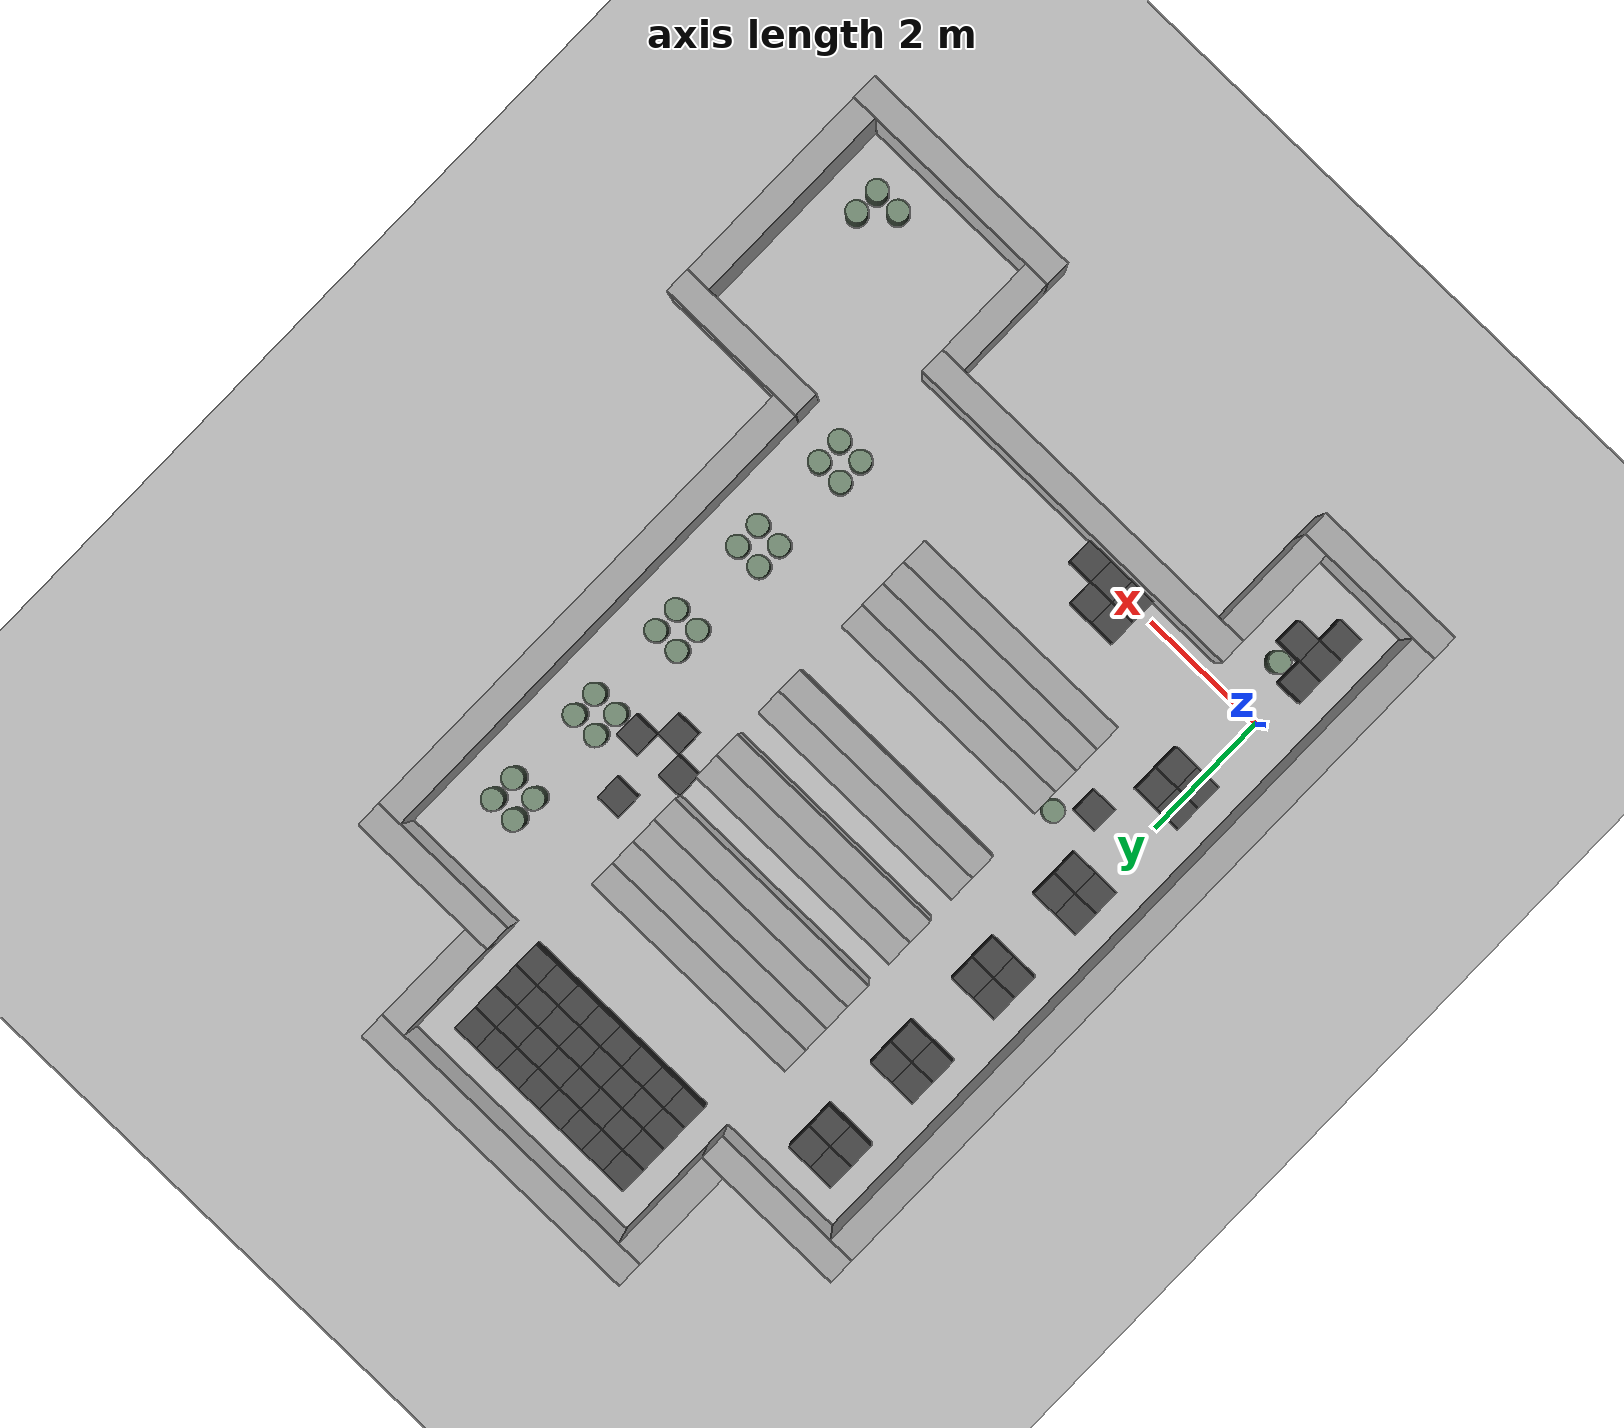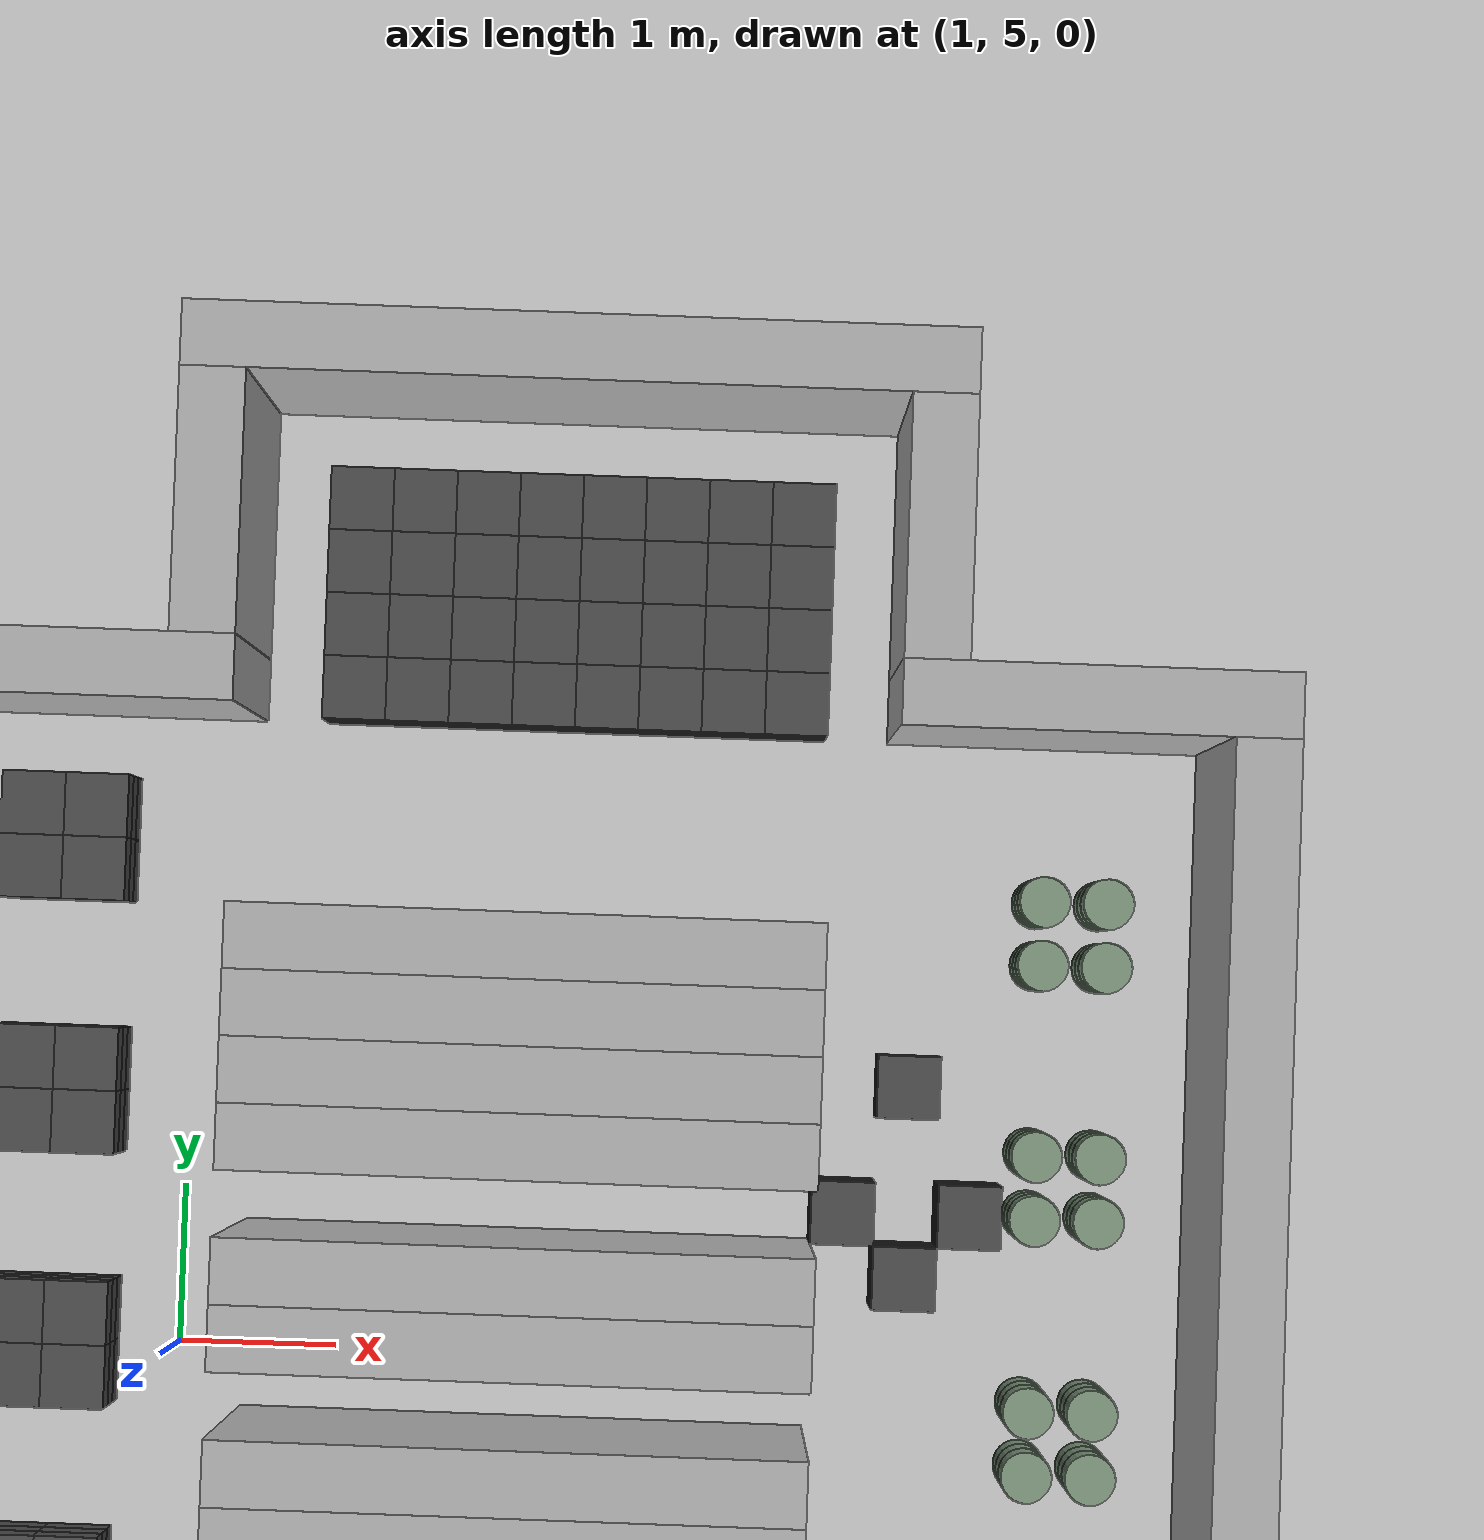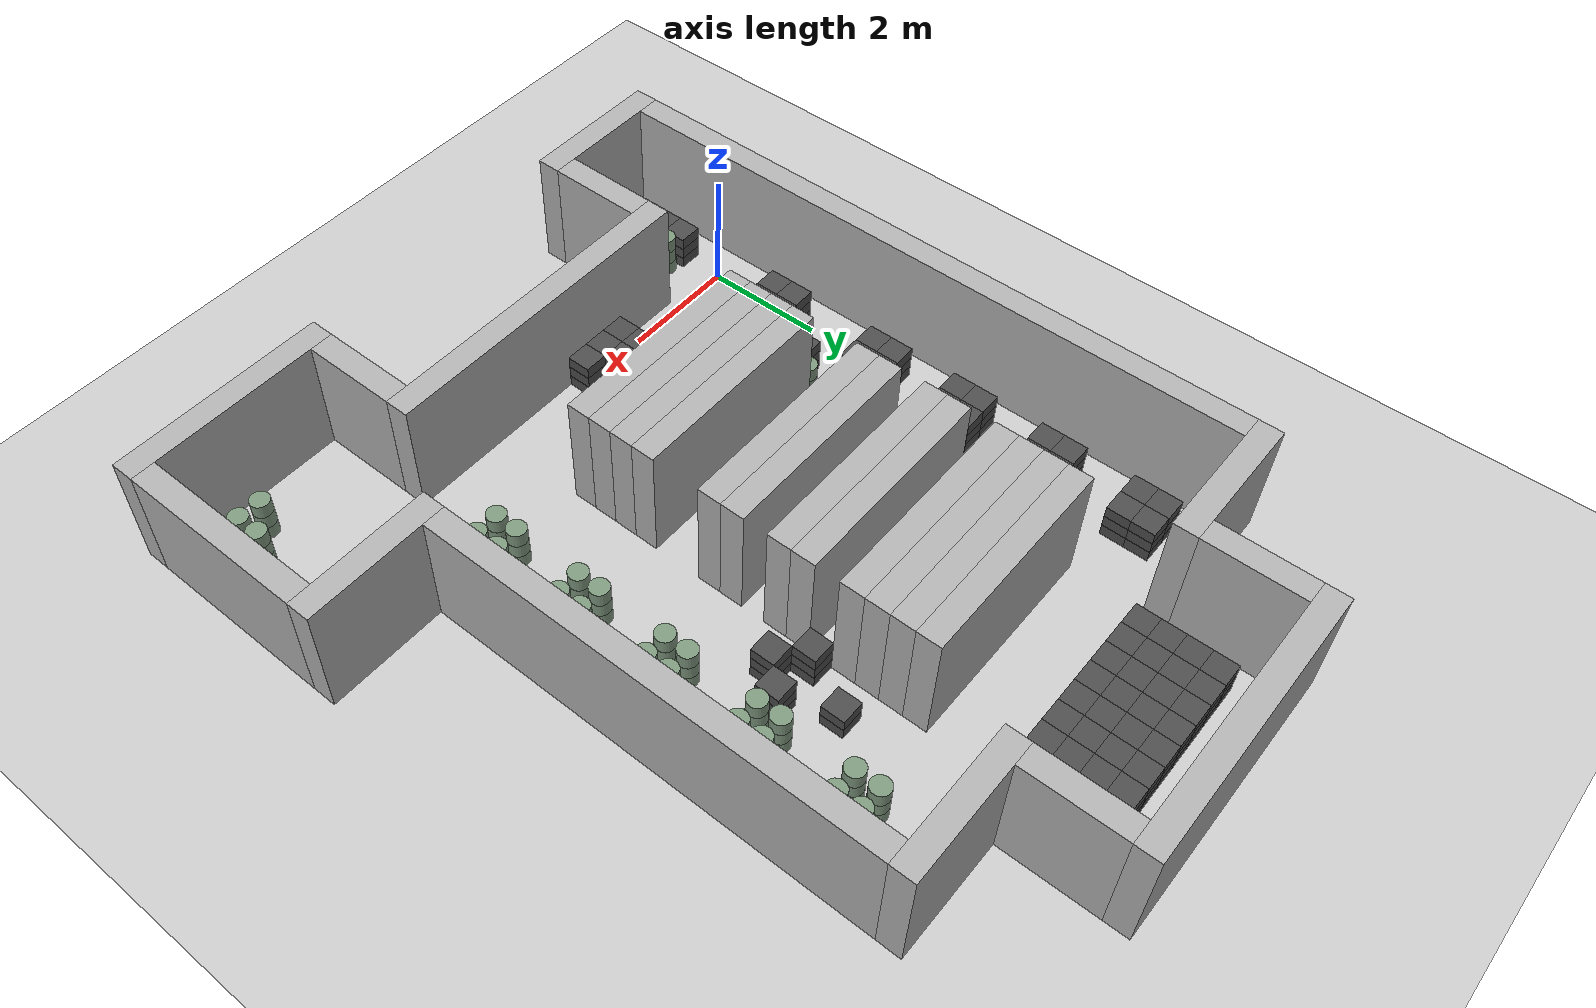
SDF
<sdf version="1.6">
 <world name="default">
  <light name="sun" type="directional">
   <cast_shadows>0</cast_shadows>
   <pose>0 0 10 0 -0 0</pose>
   <diffuse>0.8 0.8 0.8 1</diffuse>
   <specular>0.2 0.2 0.2 1</specular>
   <attenuation>
    <range>1000</range>
    <constant>0.9</constant>
    <linear>0.01</linear>
    <quadratic>0.001</quadratic>
   </attenuation>
   <direction>-0.5 0.1 -0.9</direction>
  </light>
  <include><uri>model://ground_plane</uri></include>
  <gravity>0 0 -9.8</gravity>
  <magnetic_field>6e-06 2.3e-05 -4.2e-05</magnetic_field>
  <atmosphere type="adiabatic"/>
  <physics name="default_physics" default="0" type="ode">
   <max_step_size>0.001</max_step_size>
   <real_time_factor>1</real_time_factor>
   <real_time_update_rate>1000</real_time_update_rate>
  </physics>
  <scene><ambient>0.4 0.4 0.4 1</ambient><background>0.7 0.7 0.7 1</background><shadows>0</shadows></scene>
  <spherical_coordinates>
   <surface_model>EARTH_WGS84</surface_model>
   <latitude_deg>0</latitude_deg>
   <longitude_deg>0</longitude_deg>
   <elevation>0</elevation>
   <heading_deg>0</heading_deg>
  </spherical_coordinates>
  <model name="wall_0">
   <pose frame="sim_world">-0.8 3.4 1.0 0 0 0</pose>
   <static>True</static>
   <link name="wall_0_link">
    <inertial>
     <mass>100</mass>
     <inertia>
      <ixx>0.166667</ixx>
      <ixy>0</ixy>
      <ixz>0</ixz>
      <iyy>0.166667</iyy>
      <iyz>0</iyz>
      <izz>0.166667</izz>
     </inertia>
    </inertial>
    <collision name="wall_0_collision">
     <geometry><box><size>0.4 11.200000000000001 2.0</size></box></geometry>
     <max_contacts>100</max_contacts>
    </collision>
    <visual name="wall_0_visual">
     <geometry><box><size>0.4 11.200000000000001 2.0</size></box></geometry>
     <material><ambient>0.7 0.7 0.7 1</ambient><diffuse>0.7 0.7 0.7 1</diffuse></material>
    </visual>
   </link>
  </model>
  <model name="wall_1">
   <pose frame="sim_world">1.2 -1.4 1.0 0 0 0</pose>
   <static>True</static>
   <link name="wall_1_link">
    <inertial>
     <mass>100</mass>
     <inertia>
      <ixx>0.166667</ixx>
      <ixy>0</ixy>
      <ixz>0</ixz>
      <iyy>0.166667</iyy>
      <iyz>0</iyz>
      <izz>0.166667</izz>
     </inertia>
    </inertial>
    <collision name="wall_1_collision">
     <geometry><box><size>0.4 1.6 2.0</size></box></geometry>
     <max_contacts>100</max_contacts>
    </collision>
    <visual name="wall_1_visual">
     <geometry><box><size>0.4 1.6 2.0</size></box></geometry>
     <material><ambient>0.7 0.7 0.7 1</ambient><diffuse>0.7 0.7 0.7 1</diffuse></material>
    </visual>
   </link>
  </model>
  <model name="wall_2">
   <pose frame="sim_world">1.2 10.2 1.0 0 0 0</pose>
   <static>True</static>
   <link name="wall_2_link">
    <inertial>
     <mass>100</mass>
     <inertia>
      <ixx>0.166667</ixx>
      <ixy>0</ixy>
      <ixz>0</ixz>
      <iyy>0.166667</iyy>
      <iyz>0</iyz>
      <izz>0.166667</izz>
     </inertia>
    </inertial>
    <collision name="wall_2_collision">
     <geometry><box><size>0.4 1.6 2.0</size></box></geometry>
     <max_contacts>100</max_contacts>
    </collision>
    <visual name="wall_2_visual">
     <geometry><box><size>0.4 1.6 2.0</size></box></geometry>
     <material><ambient>0.7 0.7 0.7 1</ambient><diffuse>0.7 0.7 0.7 1</diffuse></material>
    </visual>
   </link>
  </model>
  <model name="wall_3">
   <pose frame="sim_world">5.6 10.2 1.0 0 0 0</pose>
   <static>True</static>
   <link name="wall_3_link">
    <inertial>
     <mass>100</mass>
     <inertia>
      <ixx>0.166667</ixx>
      <ixy>0</ixy>
      <ixz>0</ixz>
      <iyy>0.166667</iyy>
      <iyz>0</iyz>
      <izz>0.166667</izz>
     </inertia>
    </inertial>
    <collision name="wall_3_collision">
     <geometry><box><size>0.4 1.6 2.0</size></box></geometry>
     <max_contacts>100</max_contacts>
    </collision>
    <visual name="wall_3_visual">
     <geometry><box><size>0.4 1.6 2.0</size></box></geometry>
     <material><ambient>0.7 0.7 0.7 1</ambient><diffuse>0.7 0.7 0.7 1</diffuse></material>
    </visual>
   </link>
  </model>
  <model name="wall_4">
   <pose frame="sim_world">6.4 -1.4 1.0 0 0 0</pose>
   <static>True</static>
   <link name="wall_4_link">
    <inertial>
     <mass>100</mass>
     <inertia>
      <ixx>0.166667</ixx>
      <ixy>0</ixy>
      <ixz>0</ixz>
      <iyy>0.166667</iyy>
      <iyz>0</iyz>
      <izz>0.166667</izz>
     </inertia>
    </inertial>
    <collision name="wall_4_collision">
     <geometry><box><size>0.4 1.6 2.0</size></box></geometry>
     <max_contacts>100</max_contacts>
    </collision>
    <visual name="wall_4_visual">
     <geometry><box><size>0.4 1.6 2.0</size></box></geometry>
     <material><ambient>0.7 0.7 0.7 1</ambient><diffuse>0.7 0.7 0.7 1</diffuse></material>
    </visual>
   </link>
  </model>
  <model name="wall_5">
   <pose frame="sim_world">7.6 5.2 1.0 0 0 0</pose>
   <static>True</static>
   <link name="wall_5_link">
    <inertial>
     <mass>100</mass>
     <inertia>
      <ixx>0.166667</ixx>
      <ixy>0</ixy>
      <ixz>0</ixz>
      <iyy>0.166667</iyy>
      <iyz>0</iyz>
      <izz>0.166667</izz>
     </inertia>
    </inertial>
    <collision name="wall_5_collision">
     <geometry><box><size>0.4 7.6000000000000005 2.0</size></box></geometry>
     <max_contacts>100</max_contacts>
    </collision>
    <visual name="wall_5_visual">
     <geometry><box><size>0.4 7.6000000000000005 2.0</size></box></geometry>
     <material><ambient>0.7 0.7 0.7 1</ambient><diffuse>0.7 0.7 0.7 1</diffuse></material>
    </visual>
   </link>
  </model>
  <model name="wall_6">
   <pose frame="sim_world">9.6 -0.6 1.0 0 0 0</pose>
   <static>True</static>
   <link name="wall_6_link">
    <inertial>
     <mass>100</mass>
     <inertia>
      <ixx>0.166667</ixx>
      <ixy>0</ixy>
      <ixz>0</ixz>
      <iyy>0.166667</iyy>
      <iyz>0</iyz>
      <izz>0.166667</izz>
     </inertia>
    </inertial>
    <collision name="wall_6_collision">
     <geometry><box><size>0.4 3.2 2.0</size></box></geometry>
     <max_contacts>100</max_contacts>
    </collision>
    <visual name="wall_6_visual">
     <geometry><box><size>0.4 3.2 2.0</size></box></geometry>
     <material><ambient>0.7 0.7 0.7 1</ambient><diffuse>0.7 0.7 0.7 1</diffuse></material>
    </visual>
   </link>
  </model>
  <model name="wall_7">
   <pose frame="sim_world">0.2 -2.4 1.0 0 0 0</pose>
   <static>True</static>
   <link name="wall_7_link">
    <inertial>
     <mass>100</mass>
     <inertia>
      <ixx>0.166667</ixx>
      <ixy>0</ixy>
      <ixz>0</ixz>
      <iyy>0.166667</iyy>
      <iyz>0</iyz>
      <izz>0.166667</izz>
     </inertia>
    </inertial>
    <collision name="wall_7_collision">
     <geometry><box><size>2.4000000000000004 0.4 2.0</size></box></geometry>
     <max_contacts>100</max_contacts>
    </collision>
    <visual name="wall_7_visual">
     <geometry><box><size>2.4000000000000004 0.4 2.0</size></box></geometry>
     <material><ambient>0.7 0.7 0.7 1</ambient><diffuse>0.7 0.7 0.7 1</diffuse></material>
    </visual>
   </link>
  </model>
  <model name="wall_8">
   <pose frame="sim_world">8.0 -2.4 1.0 0 0 0</pose>
   <static>True</static>
   <link name="wall_8_link">
    <inertial>
     <mass>100</mass>
     <inertia>
      <ixx>0.166667</ixx>
      <ixy>0</ixy>
      <ixz>0</ixz>
      <iyy>0.166667</iyy>
      <iyz>0</iyz>
      <izz>0.166667</izz>
     </inertia>
    </inertial>
    <collision name="wall_8_collision">
     <geometry><box><size>3.6 0.4 2.0</size></box></geometry>
     <max_contacts>100</max_contacts>
    </collision>
    <visual name="wall_8_visual">
     <geometry><box><size>3.6 0.4 2.0</size></box></geometry>
     <material><ambient>0.7 0.7 0.7 1</ambient><diffuse>0.7 0.7 0.7 1</diffuse></material>
    </visual>
   </link>
  </model>
  <model name="wall_9">
   <pose frame="sim_world">3.8 -0.4 1.0 0 0 0</pose>
   <static>True</static>
   <link name="wall_9_link">
    <inertial>
     <mass>100</mass>
     <inertia>
      <ixx>0.166667</ixx>
      <ixy>0</ixy>
      <ixz>0</ixz>
      <iyy>0.166667</iyy>
      <iyz>0</iyz>
      <izz>0.166667</izz>
     </inertia>
    </inertial>
    <collision name="wall_9_collision">
     <geometry><box><size>5.6000000000000005 0.4 2.0</size></box></geometry>
     <max_contacts>100</max_contacts>
    </collision>
    <visual name="wall_9_visual">
     <geometry><box><size>5.6000000000000005 0.4 2.0</size></box></geometry>
     <material><ambient>0.7 0.7 0.7 1</ambient><diffuse>0.7 0.7 0.7 1</diffuse></material>
    </visual>
   </link>
  </model>
  <model name="wall_10">
   <pose frame="sim_world">8.6 1.2 1.0 0 0 0</pose>
   <static>True</static>
   <link name="wall_10_link">
    <inertial>
     <mass>100</mass>
     <inertia>
      <ixx>0.166667</ixx>
      <ixy>0</ixy>
      <ixz>0</ixz>
      <iyy>0.166667</iyy>
      <iyz>0</iyz>
      <izz>0.166667</izz>
     </inertia>
    </inertial>
    <collision name="wall_10_collision">
     <geometry><box><size>2.4000000000000004 0.4 2.0</size></box></geometry>
     <max_contacts>100</max_contacts>
    </collision>
    <visual name="wall_10_visual">
     <geometry><box><size>2.4000000000000004 0.4 2.0</size></box></geometry>
     <material><ambient>0.7 0.7 0.7 1</ambient><diffuse>0.7 0.7 0.7 1</diffuse></material>
    </visual>
   </link>
  </model>
  <model name="wall_11">
   <pose frame="sim_world">3.2 1.6 1.0 0 0 0</pose>
   <static>True</static>
   <link name="wall_11_link">
    <inertial>
     <mass>100</mass>
     <inertia>
      <ixx>0.166667</ixx>
      <ixy>0</ixy>
      <ixz>0</ixz>
      <iyy>0.166667</iyy>
      <iyz>0</iyz>
      <izz>0.166667</izz>
     </inertia>
    </inertial>
    <collision name="wall_11_collision">
     <geometry><box><size>3.6 0.4 2.0</size></box></geometry>
     <max_contacts>100</max_contacts>
    </collision>
    <visual name="wall_11_visual">
     <geometry><box><size>3.6 0.4 2.0</size></box></geometry>
     <material><ambient>0.7 0.7 0.7 1</ambient><diffuse>0.7 0.7 0.7 1</diffuse></material>
    </visual>
   </link>
  </model>
  <model name="wall_12">
   <pose frame="sim_world">3.2 2.0 1.0 0 0 0</pose>
   <static>True</static>
   <link name="wall_12_link">
    <inertial>
     <mass>100</mass>
     <inertia>
      <ixx>0.166667</ixx>
      <ixy>0</ixy>
      <ixz>0</ixz>
      <iyy>0.166667</iyy>
      <iyz>0</iyz>
      <izz>0.166667</izz>
     </inertia>
    </inertial>
    <collision name="wall_12_collision">
     <geometry><box><size>3.6 0.4 2.0</size></box></geometry>
     <max_contacts>100</max_contacts>
    </collision>
    <visual name="wall_12_visual">
     <geometry><box><size>3.6 0.4 2.0</size></box></geometry>
     <material><ambient>0.7 0.7 0.7 1</ambient><diffuse>0.7 0.7 0.7 1</diffuse></material>
    </visual>
   </link>
  </model>
  <model name="wall_13">
   <pose frame="sim_world">3.2 2.4 1.0 0 0 0</pose>
   <static>True</static>
   <link name="wall_13_link">
    <inertial>
     <mass>100</mass>
     <inertia>
      <ixx>0.166667</ixx>
      <ixy>0</ixy>
      <ixz>0</ixz>
      <iyy>0.166667</iyy>
      <iyz>0</iyz>
      <izz>0.166667</izz>
     </inertia>
    </inertial>
    <collision name="wall_13_collision">
     <geometry><box><size>3.6 0.4 2.0</size></box></geometry>
     <max_contacts>100</max_contacts>
    </collision>
    <visual name="wall_13_visual">
     <geometry><box><size>3.6 0.4 2.0</size></box></geometry>
     <material><ambient>0.7 0.7 0.7 1</ambient><diffuse>0.7 0.7 0.7 1</diffuse></material>
    </visual>
   </link>
  </model>
  <model name="wall_14">
   <pose frame="sim_world">3.2 2.8 1.0 0 0 0</pose>
   <static>True</static>
   <link name="wall_14_link">
    <inertial>
     <mass>100</mass>
     <inertia>
      <ixx>0.166667</ixx>
      <ixy>0</ixy>
      <ixz>0</ixz>
      <iyy>0.166667</iyy>
      <iyz>0</iyz>
      <izz>0.166667</izz>
     </inertia>
    </inertial>
    <collision name="wall_14_collision">
     <geometry><box><size>3.6 0.4 2.0</size></box></geometry>
     <max_contacts>100</max_contacts>
    </collision>
    <visual name="wall_14_visual">
     <geometry><box><size>3.6 0.4 2.0</size></box></geometry>
     <material><ambient>0.7 0.7 0.7 1</ambient><diffuse>0.7 0.7 0.7 1</diffuse></material>
    </visual>
   </link>
  </model>
  <model name="wall_15">
   <pose frame="sim_world">3.2 4.0 1.0 0 0 0</pose>
   <static>True</static>
   <link name="wall_15_link">
    <inertial>
     <mass>100</mass>
     <inertia>
      <ixx>0.166667</ixx>
      <ixy>0</ixy>
      <ixz>0</ixz>
      <iyy>0.166667</iyy>
      <iyz>0</iyz>
      <izz>0.166667</izz>
     </inertia>
    </inertial>
    <collision name="wall_15_collision">
     <geometry><box><size>3.6 0.4 2.0</size></box></geometry>
     <max_contacts>100</max_contacts>
    </collision>
    <visual name="wall_15_visual">
     <geometry><box><size>3.6 0.4 2.0</size></box></geometry>
     <material><ambient>0.7 0.7 0.7 1</ambient><diffuse>0.7 0.7 0.7 1</diffuse></material>
    </visual>
   </link>
  </model>
  <model name="wall_16">
   <pose frame="sim_world">3.2 4.4 1.0 0 0 0</pose>
   <static>True</static>
   <link name="wall_16_link">
    <inertial>
     <mass>100</mass>
     <inertia>
      <ixx>0.166667</ixx>
      <ixy>0</ixy>
      <ixz>0</ixz>
      <iyy>0.166667</iyy>
      <iyz>0</iyz>
      <izz>0.166667</izz>
     </inertia>
    </inertial>
    <collision name="wall_16_collision">
     <geometry><box><size>3.6 0.4 2.0</size></box></geometry>
     <max_contacts>100</max_contacts>
    </collision>
    <visual name="wall_16_visual">
     <geometry><box><size>3.6 0.4 2.0</size></box></geometry>
     <material><ambient>0.7 0.7 0.7 1</ambient><diffuse>0.7 0.7 0.7 1</diffuse></material>
    </visual>
   </link>
  </model>
  <model name="wall_17">
   <pose frame="sim_world">3.2 5.2 1.0 0 0 0</pose>
   <static>True</static>
   <link name="wall_17_link">
    <inertial>
     <mass>100</mass>
     <inertia>
      <ixx>0.166667</ixx>
      <ixy>0</ixy>
      <ixz>0</ixz>
      <iyy>0.166667</iyy>
      <iyz>0</iyz>
      <izz>0.166667</izz>
     </inertia>
    </inertial>
    <collision name="wall_17_collision">
     <geometry><box><size>3.6 0.4 2.0</size></box></geometry>
     <max_contacts>100</max_contacts>
    </collision>
    <visual name="wall_17_visual">
     <geometry><box><size>3.6 0.4 2.0</size></box></geometry>
     <material><ambient>0.7 0.7 0.7 1</ambient><diffuse>0.7 0.7 0.7 1</diffuse></material>
    </visual>
   </link>
  </model>
  <model name="wall_18">
   <pose frame="sim_world">3.2 5.6 1.0 0 0 0</pose>
   <static>True</static>
   <link name="wall_18_link">
    <inertial>
     <mass>100</mass>
     <inertia>
      <ixx>0.166667</ixx>
      <ixy>0</ixy>
      <ixz>0</ixz>
      <iyy>0.166667</iyy>
      <iyz>0</iyz>
      <izz>0.166667</izz>
     </inertia>
    </inertial>
    <collision name="wall_18_collision">
     <geometry><box><size>3.6 0.4 2.0</size></box></geometry>
     <max_contacts>100</max_contacts>
    </collision>
    <visual name="wall_18_visual">
     <geometry><box><size>3.6 0.4 2.0</size></box></geometry>
     <material><ambient>0.7 0.7 0.7 1</ambient><diffuse>0.7 0.7 0.7 1</diffuse></material>
    </visual>
   </link>
  </model>
  <model name="wall_19">
   <pose frame="sim_world">3.2 6.4 1.0 0 0 0</pose>
   <static>True</static>
   <link name="wall_19_link">
    <inertial>
     <mass>100</mass>
     <inertia>
      <ixx>0.166667</ixx>
      <ixy>0</ixy>
      <ixz>0</ixz>
      <iyy>0.166667</iyy>
      <iyz>0</iyz>
      <izz>0.166667</izz>
     </inertia>
    </inertial>
    <collision name="wall_19_collision">
     <geometry><box><size>3.6 0.4 2.0</size></box></geometry>
     <max_contacts>100</max_contacts>
    </collision>
    <visual name="wall_19_visual">
     <geometry><box><size>3.6 0.4 2.0</size></box></geometry>
     <material><ambient>0.7 0.7 0.7 1</ambient><diffuse>0.7 0.7 0.7 1</diffuse></material>
    </visual>
   </link>
  </model>
  <model name="wall_20">
   <pose frame="sim_world">3.2 6.8 1.0 0 0 0</pose>
   <static>True</static>
   <link name="wall_20_link">
    <inertial>
     <mass>100</mass>
     <inertia>
      <ixx>0.166667</ixx>
      <ixy>0</ixy>
      <ixz>0</ixz>
      <iyy>0.166667</iyy>
      <iyz>0</iyz>
      <izz>0.166667</izz>
     </inertia>
    </inertial>
    <collision name="wall_20_collision">
     <geometry><box><size>3.6 0.4 2.0</size></box></geometry>
     <max_contacts>100</max_contacts>
    </collision>
    <visual name="wall_20_visual">
     <geometry><box><size>3.6 0.4 2.0</size></box></geometry>
     <material><ambient>0.7 0.7 0.7 1</ambient><diffuse>0.7 0.7 0.7 1</diffuse></material>
    </visual>
   </link>
  </model>
  <model name="wall_21">
   <pose frame="sim_world">3.2 7.2 1.0 0 0 0</pose>
   <static>True</static>
   <link name="wall_21_link">
    <inertial>
     <mass>100</mass>
     <inertia>
      <ixx>0.166667</ixx>
      <ixy>0</ixy>
      <ixz>0</ixz>
      <iyy>0.166667</iyy>
      <iyz>0</iyz>
      <izz>0.166667</izz>
     </inertia>
    </inertial>
    <collision name="wall_21_collision">
     <geometry><box><size>3.6 0.4 2.0</size></box></geometry>
     <max_contacts>100</max_contacts>
    </collision>
    <visual name="wall_21_visual">
     <geometry><box><size>3.6 0.4 2.0</size></box></geometry>
     <material><ambient>0.7 0.7 0.7 1</ambient><diffuse>0.7 0.7 0.7 1</diffuse></material>
    </visual>
   </link>
  </model>
  <model name="wall_22">
   <pose frame="sim_world">3.2 7.6 1.0 0 0 0</pose>
   <static>True</static>
   <link name="wall_22_link">
    <inertial>
     <mass>100</mass>
     <inertia>
      <ixx>0.166667</ixx>
      <ixy>0</ixy>
      <ixz>0</ixz>
      <iyy>0.166667</iyy>
      <iyz>0</iyz>
      <izz>0.166667</izz>
     </inertia>
    </inertial>
    <collision name="wall_22_collision">
     <geometry><box><size>3.6 0.4 2.0</size></box></geometry>
     <max_contacts>100</max_contacts>
    </collision>
    <visual name="wall_22_visual">
     <geometry><box><size>3.6 0.4 2.0</size></box></geometry>
     <material><ambient>0.7 0.7 0.7 1</ambient><diffuse>0.7 0.7 0.7 1</diffuse></material>
    </visual>
   </link>
  </model>
  <model name="wall_23">
   <pose frame="sim_world">0.2 9.2 1.0 0 0 0</pose>
   <static>True</static>
   <link name="wall_23_link">
    <inertial>
     <mass>100</mass>
     <inertia>
      <ixx>0.166667</ixx>
      <ixy>0</ixy>
      <ixz>0</ixz>
      <iyy>0.166667</iyy>
      <iyz>0</iyz>
      <izz>0.166667</izz>
     </inertia>
    </inertial>
    <collision name="wall_23_collision">
     <geometry><box><size>2.4000000000000004 0.4 2.0</size></box></geometry>
     <max_contacts>100</max_contacts>
    </collision>
    <visual name="wall_23_visual">
     <geometry><box><size>2.4000000000000004 0.4 2.0</size></box></geometry>
     <material><ambient>0.7 0.7 0.7 1</ambient><diffuse>0.7 0.7 0.7 1</diffuse></material>
    </visual>
   </link>
  </model>
  <model name="wall_24">
   <pose frame="sim_world">6.6 9.2 1.0 0 0 0</pose>
   <static>True</static>
   <link name="wall_24_link">
    <inertial>
     <mass>100</mass>
     <inertia>
      <ixx>0.166667</ixx>
      <ixy>0</ixy>
      <ixz>0</ixz>
      <iyy>0.166667</iyy>
      <iyz>0</iyz>
      <izz>0.166667</izz>
     </inertia>
    </inertial>
    <collision name="wall_24_collision">
     <geometry><box><size>2.4000000000000004 0.4 2.0</size></box></geometry>
     <max_contacts>100</max_contacts>
    </collision>
    <visual name="wall_24_visual">
     <geometry><box><size>2.4000000000000004 0.4 2.0</size></box></geometry>
     <material><ambient>0.7 0.7 0.7 1</ambient><diffuse>0.7 0.7 0.7 1</diffuse></material>
    </visual>
   </link>
  </model>
  <model name="wall_25">
   <pose frame="sim_world">3.4 11.2 1.0 0 0 0</pose>
   <static>True</static>
   <link name="wall_25_link">
    <inertial>
     <mass>100</mass>
     <inertia>
      <ixx>0.166667</ixx>
      <ixy>0</ixy>
      <ixz>0</ixz>
      <iyy>0.166667</iyy>
      <iyz>0</iyz>
      <izz>0.166667</izz>
     </inertia>
    </inertial>
    <collision name="wall_25_collision">
     <geometry><box><size>4.800000000000001 0.4 2.0</size></box></geometry>
     <max_contacts>100</max_contacts>
    </collision>
    <visual name="wall_25_visual">
     <geometry><box><size>4.800000000000001 0.4 2.0</size></box></geometry>
     <material><ambient>0.7 0.7 0.7 1</ambient><diffuse>0.7 0.7 0.7 1</diffuse></material>
    </visual>
   </link>
  </model>
  <model name="box_0">
   <pose frame="sim_world">0.0 -1.6 0.1 0 -0 0</pose>
   <static>True</static>
   <link name="box_0_link">
    <inertial>
     <mass>100</mass>
     <inertia>
      <ixx>0.166667</ixx>
      <ixy>0</ixy>
      <ixz>0</ixz>
      <iyy>0.166667</iyy>
      <iyz>0</iyz>
      <izz>0.166667</izz>
     </inertia>
    </inertial>
    <collision name="box_0_collision">
     <geometry><box><size>0.4 0.4 0.2</size></box></geometry>
     <max_contacts>100</max_contacts>
    </collision>
    <visual name="box_0_visual">
     <geometry><box><size>0.4 0.4 0.2</size></box></geometry>
     <material><ambient>0.3 0.3 0.3 1</ambient><diffuse>0.3 0.3 0.3 1</diffuse></material>
    </visual>
   </link>
  </model>
  <model name="box_1">
   <pose frame="sim_world">0.0 -1.6 0.3 0 -0 0</pose>
   <static>True</static>
   <link name="box_1_link">
    <inertial>
     <mass>100</mass>
     <inertia>
      <ixx>0.166667</ixx>
      <ixy>0</ixy>
      <ixz>0</ixz>
      <iyy>0.166667</iyy>
      <iyz>0</iyz>
      <izz>0.166667</izz>
     </inertia>
    </inertial>
    <collision name="box_1_collision">
     <geometry><box><size>0.4 0.4 0.2</size></box></geometry>
     <max_contacts>100</max_contacts>
    </collision>
    <visual name="box_1_visual">
     <geometry><box><size>0.4 0.4 0.2</size></box></geometry>
     <material><ambient>0.3 0.3 0.3 1</ambient><diffuse>0.3 0.3 0.3 1</diffuse></material>
    </visual>
   </link>
  </model>
  <model name="box_2">
   <pose frame="sim_world">0.0 -1.6 0.5 0 -0 0</pose>
   <static>True</static>
   <link name="box_2_link">
    <inertial>
     <mass>100</mass>
     <inertia>
      <ixx>0.166667</ixx>
      <ixy>0</ixy>
      <ixz>0</ixz>
      <iyy>0.166667</iyy>
      <iyz>0</iyz>
      <izz>0.166667</izz>
     </inertia>
    </inertial>
    <collision name="box_2_collision">
     <geometry><box><size>0.4 0.4 0.2</size></box></geometry>
     <max_contacts>100</max_contacts>
    </collision>
    <visual name="box_2_visual">
     <geometry><box><size>0.4 0.4 0.2</size></box></geometry>
     <material><ambient>0.3 0.3 0.3 1</ambient><diffuse>0.3 0.3 0.3 1</diffuse></material>
    </visual>
   </link>
  </model>
  <model name="box_3">
   <pose frame="sim_world">0.0 -1.2 0.1 0 -0 0</pose>
   <static>True</static>
   <link name="box_3_link">
    <inertial>
     <mass>100</mass>
     <inertia>
      <ixx>0.166667</ixx>
      <ixy>0</ixy>
      <ixz>0</ixz>
      <iyy>0.166667</iyy>
      <iyz>0</iyz>
      <izz>0.166667</izz>
     </inertia>
    </inertial>
    <collision name="box_3_collision">
     <geometry><box><size>0.4 0.4 0.2</size></box></geometry>
     <max_contacts>100</max_contacts>
    </collision>
    <visual name="box_3_visual">
     <geometry><box><size>0.4 0.4 0.2</size></box></geometry>
     <material><ambient>0.3 0.3 0.3 1</ambient><diffuse>0.3 0.3 0.3 1</diffuse></material>
    </visual>
   </link>
  </model>
  <model name="box_4">
   <pose frame="sim_world">0.0 -1.2 0.3 0 -0 0</pose>
   <static>True</static>
   <link name="box_4_link">
    <inertial>
     <mass>100</mass>
     <inertia>
      <ixx>0.166667</ixx>
      <ixy>0</ixy>
      <ixz>0</ixz>
      <iyy>0.166667</iyy>
      <iyz>0</iyz>
      <izz>0.166667</izz>
     </inertia>
    </inertial>
    <collision name="box_4_collision">
     <geometry><box><size>0.4 0.4 0.2</size></box></geometry>
     <max_contacts>100</max_contacts>
    </collision>
    <visual name="box_4_visual">
     <geometry><box><size>0.4 0.4 0.2</size></box></geometry>
     <material><ambient>0.3 0.3 0.3 1</ambient><diffuse>0.3 0.3 0.3 1</diffuse></material>
    </visual>
   </link>
  </model>
  <model name="box_5">
   <pose frame="sim_world">0.0 -1.2 0.5 0 -0 0</pose>
   <static>True</static>
   <link name="box_5_link">
    <inertial>
     <mass>100</mass>
     <inertia>
      <ixx>0.166667</ixx>
      <ixy>0</ixy>
      <ixz>0</ixz>
      <iyy>0.166667</iyy>
      <iyz>0</iyz>
      <izz>0.166667</izz>
     </inertia>
    </inertial>
    <collision name="box_5_collision">
     <geometry><box><size>0.4 0.4 0.2</size></box></geometry>
     <max_contacts>100</max_contacts>
    </collision>
    <visual name="box_5_visual">
     <geometry><box><size>0.4 0.4 0.2</size></box></geometry>
     <material><ambient>0.3 0.3 0.3 1</ambient><diffuse>0.3 0.3 0.3 1</diffuse></material>
    </visual>
   </link>
  </model>
  <model name="box_6">
   <pose frame="sim_world">0.0 -0.8 0.1 0 -0 0</pose>
   <static>True</static>
   <link name="box_6_link">
    <inertial>
     <mass>100</mass>
     <inertia>
      <ixx>0.166667</ixx>
      <ixy>0</ixy>
      <ixz>0</ixz>
      <iyy>0.166667</iyy>
      <iyz>0</iyz>
      <izz>0.166667</izz>
     </inertia>
    </inertial>
    <collision name="box_6_collision">
     <geometry><box><size>0.4 0.4 0.2</size></box></geometry>
     <max_contacts>100</max_contacts>
    </collision>
    <visual name="box_6_visual">
     <geometry><box><size>0.4 0.4 0.2</size></box></geometry>
     <material><ambient>0.3 0.3 0.3 1</ambient><diffuse>0.3 0.3 0.3 1</diffuse></material>
    </visual>
   </link>
  </model>
  <model name="box_7">
   <pose frame="sim_world">0.0 -0.8 0.3 0 -0 0</pose>
   <static>True</static>
   <link name="box_7_link">
    <inertial>
     <mass>100</mass>
     <inertia>
      <ixx>0.166667</ixx>
      <ixy>0</ixy>
      <ixz>0</ixz>
      <iyy>0.166667</iyy>
      <iyz>0</iyz>
      <izz>0.166667</izz>
     </inertia>
    </inertial>
    <collision name="box_7_collision">
     <geometry><box><size>0.4 0.4 0.2</size></box></geometry>
     <max_contacts>100</max_contacts>
    </collision>
    <visual name="box_7_visual">
     <geometry><box><size>0.4 0.4 0.2</size></box></geometry>
     <material><ambient>0.3 0.3 0.3 1</ambient><diffuse>0.3 0.3 0.3 1</diffuse></material>
    </visual>
   </link>
  </model>
  <model name="box_8">
   <pose frame="sim_world">0.0 -0.8 0.5 0 -0 0</pose>
   <static>True</static>
   <link name="box_8_link">
    <inertial>
     <mass>100</mass>
     <inertia>
      <ixx>0.166667</ixx>
      <ixy>0</ixy>
      <ixz>0</ixz>
      <iyy>0.166667</iyy>
      <iyz>0</iyz>
      <izz>0.166667</izz>
     </inertia>
    </inertial>
    <collision name="box_8_collision">
     <geometry><box><size>0.4 0.4 0.2</size></box></geometry>
     <max_contacts>100</max_contacts>
    </collision>
    <visual name="box_8_visual">
     <geometry><box><size>0.4 0.4 0.2</size></box></geometry>
     <material><ambient>0.3 0.3 0.3 1</ambient><diffuse>0.3 0.3 0.3 1</diffuse></material>
    </visual>
   </link>
  </model>
  <model name="box_9">
   <pose frame="sim_world">0.0 1.2 0.1 0 -0 0</pose>
   <static>True</static>
   <link name="box_9_link">
    <inertial>
     <mass>100</mass>
     <inertia>
      <ixx>0.166667</ixx>
      <ixy>0</ixy>
      <ixz>0</ixz>
      <iyy>0.166667</iyy>
      <iyz>0</iyz>
      <izz>0.166667</izz>
     </inertia>
    </inertial>
    <collision name="box_9_collision">
     <geometry><box><size>0.4 0.4 0.2</size></box></geometry>
     <max_contacts>100</max_contacts>
    </collision>
    <visual name="box_9_visual">
     <geometry><box><size>0.4 0.4 0.2</size></box></geometry>
     <material><ambient>0.3 0.3 0.3 1</ambient><diffuse>0.3 0.3 0.3 1</diffuse></material>
    </visual>
   </link>
  </model>
  <model name="box_10">
   <pose frame="sim_world">0.0 1.2 0.3 0 -0 0</pose>
   <static>True</static>
   <link name="box_10_link">
    <inertial>
     <mass>100</mass>
     <inertia>
      <ixx>0.166667</ixx>
      <ixy>0</ixy>
      <ixz>0</ixz>
      <iyy>0.166667</iyy>
      <iyz>0</iyz>
      <izz>0.166667</izz>
     </inertia>
    </inertial>
    <collision name="box_10_collision">
     <geometry><box><size>0.4 0.4 0.2</size></box></geometry>
     <max_contacts>100</max_contacts>
    </collision>
    <visual name="box_10_visual">
     <geometry><box><size>0.4 0.4 0.2</size></box></geometry>
     <material><ambient>0.3 0.3 0.3 1</ambient><diffuse>0.3 0.3 0.3 1</diffuse></material>
    </visual>
   </link>
  </model>
  <model name="box_11">
   <pose frame="sim_world">0.0 1.2 0.5 0 -0 0</pose>
   <static>True</static>
   <link name="box_11_link">
    <inertial>
     <mass>100</mass>
     <inertia>
      <ixx>0.166667</ixx>
      <ixy>0</ixy>
      <ixz>0</ixz>
      <iyy>0.166667</iyy>
      <iyz>0</iyz>
      <izz>0.166667</izz>
     </inertia>
    </inertial>
    <collision name="box_11_collision">
     <geometry><box><size>0.4 0.4 0.2</size></box></geometry>
     <max_contacts>100</max_contacts>
    </collision>
    <visual name="box_11_visual">
     <geometry><box><size>0.4 0.4 0.2</size></box></geometry>
     <material><ambient>0.3 0.3 0.3 1</ambient><diffuse>0.3 0.3 0.3 1</diffuse></material>
    </visual>
   </link>
  </model>
  <model name="box_12">
   <pose frame="sim_world">0.0 1.6 0.1 0 -0 0</pose>
   <static>True</static>
   <link name="box_12_link">
    <inertial>
     <mass>100</mass>
     <inertia>
      <ixx>0.166667</ixx>
      <ixy>0</ixy>
      <ixz>0</ixz>
      <iyy>0.166667</iyy>
      <iyz>0</iyz>
      <izz>0.166667</izz>
     </inertia>
    </inertial>
    <collision name="box_12_collision">
     <geometry><box><size>0.4 0.4 0.2</size></box></geometry>
     <max_contacts>100</max_contacts>
    </collision>
    <visual name="box_12_visual">
     <geometry><box><size>0.4 0.4 0.2</size></box></geometry>
     <material><ambient>0.3 0.3 0.3 1</ambient><diffuse>0.3 0.3 0.3 1</diffuse></material>
    </visual>
   </link>
  </model>
  <model name="box_13">
   <pose frame="sim_world">0.0 1.6 0.3 0 -0 0</pose>
   <static>True</static>
   <link name="box_13_link">
    <inertial>
     <mass>100</mass>
     <inertia>
      <ixx>0.166667</ixx>
      <ixy>0</ixy>
      <ixz>0</ixz>
      <iyy>0.166667</iyy>
      <iyz>0</iyz>
      <izz>0.166667</izz>
     </inertia>
    </inertial>
    <collision name="box_13_collision">
     <geometry><box><size>0.4 0.4 0.2</size></box></geometry>
     <max_contacts>100</max_contacts>
    </collision>
    <visual name="box_13_visual">
     <geometry><box><size>0.4 0.4 0.2</size></box></geometry>
     <material><ambient>0.3 0.3 0.3 1</ambient><diffuse>0.3 0.3 0.3 1</diffuse></material>
    </visual>
   </link>
  </model>
  <model name="box_14">
   <pose frame="sim_world">0.0 1.6 0.5 0 -0 0</pose>
   <static>True</static>
   <link name="box_14_link">
    <inertial>
     <mass>100</mass>
     <inertia>
      <ixx>0.166667</ixx>
      <ixy>0</ixy>
      <ixz>0</ixz>
      <iyy>0.166667</iyy>
      <iyz>0</iyz>
      <izz>0.166667</izz>
     </inertia>
    </inertial>
    <collision name="box_14_collision">
     <geometry><box><size>0.4 0.4 0.2</size></box></geometry>
     <max_contacts>100</max_contacts>
    </collision>
    <visual name="box_14_visual">
     <geometry><box><size>0.4 0.4 0.2</size></box></geometry>
     <material><ambient>0.3 0.3 0.3 1</ambient><diffuse>0.3 0.3 0.3 1</diffuse></material>
    </visual>
   </link>
  </model>
  <model name="box_15">
   <pose frame="sim_world">0.0 3.2 0.1 0 -0 0</pose>
   <static>True</static>
   <link name="box_15_link">
    <inertial>
     <mass>100</mass>
     <inertia>
      <ixx>0.166667</ixx>
      <ixy>0</ixy>
      <ixz>0</ixz>
      <iyy>0.166667</iyy>
      <iyz>0</iyz>
      <izz>0.166667</izz>
     </inertia>
    </inertial>
    <collision name="box_15_collision">
     <geometry><box><size>0.4 0.4 0.2</size></box></geometry>
     <max_contacts>100</max_contacts>
    </collision>
    <visual name="box_15_visual">
     <geometry><box><size>0.4 0.4 0.2</size></box></geometry>
     <material><ambient>0.3 0.3 0.3 1</ambient><diffuse>0.3 0.3 0.3 1</diffuse></material>
    </visual>
   </link>
  </model>
  <model name="box_16">
   <pose frame="sim_world">0.0 3.2 0.3 0 -0 0</pose>
   <static>True</static>
   <link name="box_16_link">
    <inertial>
     <mass>100</mass>
     <inertia>
      <ixx>0.166667</ixx>
      <ixy>0</ixy>
      <ixz>0</ixz>
      <iyy>0.166667</iyy>
      <iyz>0</iyz>
      <izz>0.166667</izz>
     </inertia>
    </inertial>
    <collision name="box_16_collision">
     <geometry><box><size>0.4 0.4 0.2</size></box></geometry>
     <max_contacts>100</max_contacts>
    </collision>
    <visual name="box_16_visual">
     <geometry><box><size>0.4 0.4 0.2</size></box></geometry>
     <material><ambient>0.3 0.3 0.3 1</ambient><diffuse>0.3 0.3 0.3 1</diffuse></material>
    </visual>
   </link>
  </model>
  <model name="box_17">
   <pose frame="sim_world">0.0 3.2 0.5 0 -0 0</pose>
   <static>True</static>
   <link name="box_17_link">
    <inertial>
     <mass>100</mass>
     <inertia>
      <ixx>0.166667</ixx>
      <ixy>0</ixy>
      <ixz>0</ixz>
      <iyy>0.166667</iyy>
      <iyz>0</iyz>
      <izz>0.166667</izz>
     </inertia>
    </inertial>
    <collision name="box_17_collision">
     <geometry><box><size>0.4 0.4 0.2</size></box></geometry>
     <max_contacts>100</max_contacts>
    </collision>
    <visual name="box_17_visual">
     <geometry><box><size>0.4 0.4 0.2</size></box></geometry>
     <material><ambient>0.3 0.3 0.3 1</ambient><diffuse>0.3 0.3 0.3 1</diffuse></material>
    </visual>
   </link>
  </model>
  <model name="box_18">
   <pose frame="sim_world">0.0 3.6 0.1 0 -0 0</pose>
   <static>True</static>
   <link name="box_18_link">
    <inertial>
     <mass>100</mass>
     <inertia>
      <ixx>0.166667</ixx>
      <ixy>0</ixy>
      <ixz>0</ixz>
      <iyy>0.166667</iyy>
      <iyz>0</iyz>
      <izz>0.166667</izz>
     </inertia>
    </inertial>
    <collision name="box_18_collision">
     <geometry><box><size>0.4 0.4 0.2</size></box></geometry>
     <max_contacts>100</max_contacts>
    </collision>
    <visual name="box_18_visual">
     <geometry><box><size>0.4 0.4 0.2</size></box></geometry>
     <material><ambient>0.3 0.3 0.3 1</ambient><diffuse>0.3 0.3 0.3 1</diffuse></material>
    </visual>
   </link>
  </model>
  <model name="box_19">
   <pose frame="sim_world">0.0 3.6 0.3 0 -0 0</pose>
   <static>True</static>
   <link name="box_19_link">
    <inertial>
     <mass>100</mass>
     <inertia>
      <ixx>0.166667</ixx>
      <ixy>0</ixy>
      <ixz>0</ixz>
      <iyy>0.166667</iyy>
      <iyz>0</iyz>
      <izz>0.166667</izz>
     </inertia>
    </inertial>
    <collision name="box_19_collision">
     <geometry><box><size>0.4 0.4 0.2</size></box></geometry>
     <max_contacts>100</max_contacts>
    </collision>
    <visual name="box_19_visual">
     <geometry><box><size>0.4 0.4 0.2</size></box></geometry>
     <material><ambient>0.3 0.3 0.3 1</ambient><diffuse>0.3 0.3 0.3 1</diffuse></material>
    </visual>
   </link>
  </model>
  <model name="box_20">
   <pose frame="sim_world">0.0 3.6 0.5 0 -0 0</pose>
   <static>True</static>
   <link name="box_20_link">
    <inertial>
     <mass>100</mass>
     <inertia>
      <ixx>0.166667</ixx>
      <ixy>0</ixy>
      <ixz>0</ixz>
      <iyy>0.166667</iyy>
      <iyz>0</iyz>
      <izz>0.166667</izz>
     </inertia>
    </inertial>
    <collision name="box_20_collision">
     <geometry><box><size>0.4 0.4 0.2</size></box></geometry>
     <max_contacts>100</max_contacts>
    </collision>
    <visual name="box_20_visual">
     <geometry><box><size>0.4 0.4 0.2</size></box></geometry>
     <material><ambient>0.3 0.3 0.3 1</ambient><diffuse>0.3 0.3 0.3 1</diffuse></material>
    </visual>
   </link>
  </model>
  <model name="box_21">
   <pose frame="sim_world">0.0 4.8 0.1 0 -0 0</pose>
   <static>True</static>
   <link name="box_21_link">
    <inertial>
     <mass>100</mass>
     <inertia>
      <ixx>0.166667</ixx>
      <ixy>0</ixy>
      <ixz>0</ixz>
      <iyy>0.166667</iyy>
      <iyz>0</iyz>
      <izz>0.166667</izz>
     </inertia>
    </inertial>
    <collision name="box_21_collision">
     <geometry><box><size>0.4 0.4 0.2</size></box></geometry>
     <max_contacts>100</max_contacts>
    </collision>
    <visual name="box_21_visual">
     <geometry><box><size>0.4 0.4 0.2</size></box></geometry>
     <material><ambient>0.3 0.3 0.3 1</ambient><diffuse>0.3 0.3 0.3 1</diffuse></material>
    </visual>
   </link>
  </model>
  <model name="box_22">
   <pose frame="sim_world">0.0 4.8 0.3 0 -0 0</pose>
   <static>True</static>
   <link name="box_22_link">
    <inertial>
     <mass>100</mass>
     <inertia>
      <ixx>0.166667</ixx>
      <ixy>0</ixy>
      <ixz>0</ixz>
      <iyy>0.166667</iyy>
      <iyz>0</iyz>
      <izz>0.166667</izz>
     </inertia>
    </inertial>
    <collision name="box_22_collision">
     <geometry><box><size>0.4 0.4 0.2</size></box></geometry>
     <max_contacts>100</max_contacts>
    </collision>
    <visual name="box_22_visual">
     <geometry><box><size>0.4 0.4 0.2</size></box></geometry>
     <material><ambient>0.3 0.3 0.3 1</ambient><diffuse>0.3 0.3 0.3 1</diffuse></material>
    </visual>
   </link>
  </model>
  <model name="box_23">
   <pose frame="sim_world">0.0 4.8 0.5 0 -0 0</pose>
   <static>True</static>
   <link name="box_23_link">
    <inertial>
     <mass>100</mass>
     <inertia>
      <ixx>0.166667</ixx>
      <ixy>0</ixy>
      <ixz>0</ixz>
      <iyy>0.166667</iyy>
      <iyz>0</iyz>
      <izz>0.166667</izz>
     </inertia>
    </inertial>
    <collision name="box_23_collision">
     <geometry><box><size>0.4 0.4 0.2</size></box></geometry>
     <max_contacts>100</max_contacts>
    </collision>
    <visual name="box_23_visual">
     <geometry><box><size>0.4 0.4 0.2</size></box></geometry>
     <material><ambient>0.3 0.3 0.3 1</ambient><diffuse>0.3 0.3 0.3 1</diffuse></material>
    </visual>
   </link>
  </model>
  <model name="box_24">
   <pose frame="sim_world">0.0 5.2 0.1 0 -0 0</pose>
   <static>True</static>
   <link name="box_24_link">
    <inertial>
     <mass>100</mass>
     <inertia>
      <ixx>0.166667</ixx>
      <ixy>0</ixy>
      <ixz>0</ixz>
      <iyy>0.166667</iyy>
      <iyz>0</iyz>
      <izz>0.166667</izz>
     </inertia>
    </inertial>
    <collision name="box_24_collision">
     <geometry><box><size>0.4 0.4 0.2</size></box></geometry>
     <max_contacts>100</max_contacts>
    </collision>
    <visual name="box_24_visual">
     <geometry><box><size>0.4 0.4 0.2</size></box></geometry>
     <material><ambient>0.3 0.3 0.3 1</ambient><diffuse>0.3 0.3 0.3 1</diffuse></material>
    </visual>
   </link>
  </model>
  <model name="box_25">
   <pose frame="sim_world">0.0 5.2 0.3 0 -0 0</pose>
   <static>True</static>
   <link name="box_25_link">
    <inertial>
     <mass>100</mass>
     <inertia>
      <ixx>0.166667</ixx>
      <ixy>0</ixy>
      <ixz>0</ixz>
      <iyy>0.166667</iyy>
      <iyz>0</iyz>
      <izz>0.166667</izz>
     </inertia>
    </inertial>
    <collision name="box_25_collision">
     <geometry><box><size>0.4 0.4 0.2</size></box></geometry>
     <max_contacts>100</max_contacts>
    </collision>
    <visual name="box_25_visual">
     <geometry><box><size>0.4 0.4 0.2</size></box></geometry>
     <material><ambient>0.3 0.3 0.3 1</ambient><diffuse>0.3 0.3 0.3 1</diffuse></material>
    </visual>
   </link>
  </model>
  <model name="box_26">
   <pose frame="sim_world">0.0 5.2 0.5 0 -0 0</pose>
   <static>True</static>
   <link name="box_26_link">
    <inertial>
     <mass>100</mass>
     <inertia>
      <ixx>0.166667</ixx>
      <ixy>0</ixy>
      <ixz>0</ixz>
      <iyy>0.166667</iyy>
      <iyz>0</iyz>
      <izz>0.166667</izz>
     </inertia>
    </inertial>
    <collision name="box_26_collision">
     <geometry><box><size>0.4 0.4 0.2</size></box></geometry>
     <max_contacts>100</max_contacts>
    </collision>
    <visual name="box_26_visual">
     <geometry><box><size>0.4 0.4 0.2</size></box></geometry>
     <material><ambient>0.3 0.3 0.3 1</ambient><diffuse>0.3 0.3 0.3 1</diffuse></material>
    </visual>
   </link>
  </model>
  <model name="box_27">
   <pose frame="sim_world">0.0 6.4 0.1 0 -0 0</pose>
   <static>True</static>
   <link name="box_27_link">
    <inertial>
     <mass>100</mass>
     <inertia>
      <ixx>0.166667</ixx>
      <ixy>0</ixy>
      <ixz>0</ixz>
      <iyy>0.166667</iyy>
      <iyz>0</iyz>
      <izz>0.166667</izz>
     </inertia>
    </inertial>
    <collision name="box_27_collision">
     <geometry><box><size>0.4 0.4 0.2</size></box></geometry>
     <max_contacts>100</max_contacts>
    </collision>
    <visual name="box_27_visual">
     <geometry><box><size>0.4 0.4 0.2</size></box></geometry>
     <material><ambient>0.3 0.3 0.3 1</ambient><diffuse>0.3 0.3 0.3 1</diffuse></material>
    </visual>
   </link>
  </model>
  <model name="box_28">
   <pose frame="sim_world">0.0 6.4 0.3 0 -0 0</pose>
   <static>True</static>
   <link name="box_28_link">
    <inertial>
     <mass>100</mass>
     <inertia>
      <ixx>0.166667</ixx>
      <ixy>0</ixy>
      <ixz>0</ixz>
      <iyy>0.166667</iyy>
      <iyz>0</iyz>
      <izz>0.166667</izz>
     </inertia>
    </inertial>
    <collision name="box_28_collision">
     <geometry><box><size>0.4 0.4 0.2</size></box></geometry>
     <max_contacts>100</max_contacts>
    </collision>
    <visual name="box_28_visual">
     <geometry><box><size>0.4 0.4 0.2</size></box></geometry>
     <material><ambient>0.3 0.3 0.3 1</ambient><diffuse>0.3 0.3 0.3 1</diffuse></material>
    </visual>
   </link>
  </model>
  <model name="box_29">
   <pose frame="sim_world">0.0 6.4 0.5 0 -0 0</pose>
   <static>True</static>
   <link name="box_29_link">
    <inertial>
     <mass>100</mass>
     <inertia>
      <ixx>0.166667</ixx>
      <ixy>0</ixy>
      <ixz>0</ixz>
      <iyy>0.166667</iyy>
      <iyz>0</iyz>
      <izz>0.166667</izz>
     </inertia>
    </inertial>
    <collision name="box_29_collision">
     <geometry><box><size>0.4 0.4 0.2</size></box></geometry>
     <max_contacts>100</max_contacts>
    </collision>
    <visual name="box_29_visual">
     <geometry><box><size>0.4 0.4 0.2</size></box></geometry>
     <material><ambient>0.3 0.3 0.3 1</ambient><diffuse>0.3 0.3 0.3 1</diffuse></material>
    </visual>
   </link>
  </model>
  <model name="box_30">
   <pose frame="sim_world">0.0 6.8 0.1 0 -0 0</pose>
   <static>True</static>
   <link name="box_30_link">
    <inertial>
     <mass>100</mass>
     <inertia>
      <ixx>0.166667</ixx>
      <ixy>0</ixy>
      <ixz>0</ixz>
      <iyy>0.166667</iyy>
      <iyz>0</iyz>
      <izz>0.166667</izz>
     </inertia>
    </inertial>
    <collision name="box_30_collision">
     <geometry><box><size>0.4 0.4 0.2</size></box></geometry>
     <max_contacts>100</max_contacts>
    </collision>
    <visual name="box_30_visual">
     <geometry><box><size>0.4 0.4 0.2</size></box></geometry>
     <material><ambient>0.3 0.3 0.3 1</ambient><diffuse>0.3 0.3 0.3 1</diffuse></material>
    </visual>
   </link>
  </model>
  <model name="box_31">
   <pose frame="sim_world">0.0 6.8 0.3 0 -0 0</pose>
   <static>True</static>
   <link name="box_31_link">
    <inertial>
     <mass>100</mass>
     <inertia>
      <ixx>0.166667</ixx>
      <ixy>0</ixy>
      <ixz>0</ixz>
      <iyy>0.166667</iyy>
      <iyz>0</iyz>
      <izz>0.166667</izz>
     </inertia>
    </inertial>
    <collision name="box_31_collision">
     <geometry><box><size>0.4 0.4 0.2</size></box></geometry>
     <max_contacts>100</max_contacts>
    </collision>
    <visual name="box_31_visual">
     <geometry><box><size>0.4 0.4 0.2</size></box></geometry>
     <material><ambient>0.3 0.3 0.3 1</ambient><diffuse>0.3 0.3 0.3 1</diffuse></material>
    </visual>
   </link>
  </model>
  <model name="box_32">
   <pose frame="sim_world">0.0 6.8 0.5 0 -0 0</pose>
   <static>True</static>
   <link name="box_32_link">
    <inertial>
     <mass>100</mass>
     <inertia>
      <ixx>0.166667</ixx>
      <ixy>0</ixy>
      <ixz>0</ixz>
      <iyy>0.166667</iyy>
      <iyz>0</iyz>
      <izz>0.166667</izz>
     </inertia>
    </inertial>
    <collision name="box_32_collision">
     <geometry><box><size>0.4 0.4 0.2</size></box></geometry>
     <max_contacts>100</max_contacts>
    </collision>
    <visual name="box_32_visual">
     <geometry><box><size>0.4 0.4 0.2</size></box></geometry>
     <material><ambient>0.3 0.3 0.3 1</ambient><diffuse>0.3 0.3 0.3 1</diffuse></material>
    </visual>
   </link>
  </model>
  <model name="box_33">
   <pose frame="sim_world">0.0 8.0 0.1 0 -0 0</pose>
   <static>True</static>
   <link name="box_33_link">
    <inertial>
     <mass>100</mass>
     <inertia>
      <ixx>0.166667</ixx>
      <ixy>0</ixy>
      <ixz>0</ixz>
      <iyy>0.166667</iyy>
      <iyz>0</iyz>
      <izz>0.166667</izz>
     </inertia>
    </inertial>
    <collision name="box_33_collision">
     <geometry><box><size>0.4 0.4 0.2</size></box></geometry>
     <max_contacts>100</max_contacts>
    </collision>
    <visual name="box_33_visual">
     <geometry><box><size>0.4 0.4 0.2</size></box></geometry>
     <material><ambient>0.3 0.3 0.3 1</ambient><diffuse>0.3 0.3 0.3 1</diffuse></material>
    </visual>
   </link>
  </model>
  <model name="box_34">
   <pose frame="sim_world">0.0 8.0 0.3 0 -0 0</pose>
   <static>True</static>
   <link name="box_34_link">
    <inertial>
     <mass>100</mass>
     <inertia>
      <ixx>0.166667</ixx>
      <ixy>0</ixy>
      <ixz>0</ixz>
      <iyy>0.166667</iyy>
      <iyz>0</iyz>
      <izz>0.166667</izz>
     </inertia>
    </inertial>
    <collision name="box_34_collision">
     <geometry><box><size>0.4 0.4 0.2</size></box></geometry>
     <max_contacts>100</max_contacts>
    </collision>
    <visual name="box_34_visual">
     <geometry><box><size>0.4 0.4 0.2</size></box></geometry>
     <material><ambient>0.3 0.3 0.3 1</ambient><diffuse>0.3 0.3 0.3 1</diffuse></material>
    </visual>
   </link>
  </model>
  <model name="box_35">
   <pose frame="sim_world">0.0 8.0 0.5 0 -0 0</pose>
   <static>True</static>
   <link name="box_35_link">
    <inertial>
     <mass>100</mass>
     <inertia>
      <ixx>0.166667</ixx>
      <ixy>0</ixy>
      <ixz>0</ixz>
      <iyy>0.166667</iyy>
      <iyz>0</iyz>
      <izz>0.166667</izz>
     </inertia>
    </inertial>
    <collision name="box_35_collision">
     <geometry><box><size>0.4 0.4 0.2</size></box></geometry>
     <max_contacts>100</max_contacts>
    </collision>
    <visual name="box_35_visual">
     <geometry><box><size>0.4 0.4 0.2</size></box></geometry>
     <material><ambient>0.3 0.3 0.3 1</ambient><diffuse>0.3 0.3 0.3 1</diffuse></material>
    </visual>
   </link>
  </model>
  <model name="box_36">
   <pose frame="sim_world">0.0 8.4 0.1 0 -0 0</pose>
   <static>True</static>
   <link name="box_36_link">
    <inertial>
     <mass>100</mass>
     <inertia>
      <ixx>0.166667</ixx>
      <ixy>0</ixy>
      <ixz>0</ixz>
      <iyy>0.166667</iyy>
      <iyz>0</iyz>
      <izz>0.166667</izz>
     </inertia>
    </inertial>
    <collision name="box_36_collision">
     <geometry><box><size>0.4 0.4 0.2</size></box></geometry>
     <max_contacts>100</max_contacts>
    </collision>
    <visual name="box_36_visual">
     <geometry><box><size>0.4 0.4 0.2</size></box></geometry>
     <material><ambient>0.3 0.3 0.3 1</ambient><diffuse>0.3 0.3 0.3 1</diffuse></material>
    </visual>
   </link>
  </model>
  <model name="box_37">
   <pose frame="sim_world">0.0 8.4 0.3 0 -0 0</pose>
   <static>True</static>
   <link name="box_37_link">
    <inertial>
     <mass>100</mass>
     <inertia>
      <ixx>0.166667</ixx>
      <ixy>0</ixy>
      <ixz>0</ixz>
      <iyy>0.166667</iyy>
      <iyz>0</iyz>
      <izz>0.166667</izz>
     </inertia>
    </inertial>
    <collision name="box_37_collision">
     <geometry><box><size>0.4 0.4 0.2</size></box></geometry>
     <max_contacts>100</max_contacts>
    </collision>
    <visual name="box_37_visual">
     <geometry><box><size>0.4 0.4 0.2</size></box></geometry>
     <material><ambient>0.3 0.3 0.3 1</ambient><diffuse>0.3 0.3 0.3 1</diffuse></material>
    </visual>
   </link>
  </model>
  <model name="box_38">
   <pose frame="sim_world">0.0 8.4 0.5 0 -0 0</pose>
   <static>True</static>
   <link name="box_38_link">
    <inertial>
     <mass>100</mass>
     <inertia>
      <ixx>0.166667</ixx>
      <ixy>0</ixy>
      <ixz>0</ixz>
      <iyy>0.166667</iyy>
      <iyz>0</iyz>
      <izz>0.166667</izz>
     </inertia>
    </inertial>
    <collision name="box_38_collision">
     <geometry><box><size>0.4 0.4 0.2</size></box></geometry>
     <max_contacts>100</max_contacts>
    </collision>
    <visual name="box_38_visual">
     <geometry><box><size>0.4 0.4 0.2</size></box></geometry>
     <material><ambient>0.3 0.3 0.3 1</ambient><diffuse>0.3 0.3 0.3 1</diffuse></material>
    </visual>
   </link>
  </model>
  <model name="box_39">
   <pose frame="sim_world">0.4 -1.2 0.1 0 -0 0</pose>
   <static>True</static>
   <link name="box_39_link">
    <inertial>
     <mass>100</mass>
     <inertia>
      <ixx>0.166667</ixx>
      <ixy>0</ixy>
      <ixz>0</ixz>
      <iyy>0.166667</iyy>
      <iyz>0</iyz>
      <izz>0.166667</izz>
     </inertia>
    </inertial>
    <collision name="box_39_collision">
     <geometry><box><size>0.4 0.4 0.2</size></box></geometry>
     <max_contacts>100</max_contacts>
    </collision>
    <visual name="box_39_visual">
     <geometry><box><size>0.4 0.4 0.2</size></box></geometry>
     <material><ambient>0.3 0.3 0.3 1</ambient><diffuse>0.3 0.3 0.3 1</diffuse></material>
    </visual>
   </link>
  </model>
  <model name="box_40">
   <pose frame="sim_world">0.4 -1.2 0.3 0 -0 0</pose>
   <static>True</static>
   <link name="box_40_link">
    <inertial>
     <mass>100</mass>
     <inertia>
      <ixx>0.166667</ixx>
      <ixy>0</ixy>
      <ixz>0</ixz>
      <iyy>0.166667</iyy>
      <iyz>0</iyz>
      <izz>0.166667</izz>
     </inertia>
    </inertial>
    <collision name="box_40_collision">
     <geometry><box><size>0.4 0.4 0.2</size></box></geometry>
     <max_contacts>100</max_contacts>
    </collision>
    <visual name="box_40_visual">
     <geometry><box><size>0.4 0.4 0.2</size></box></geometry>
     <material><ambient>0.3 0.3 0.3 1</ambient><diffuse>0.3 0.3 0.3 1</diffuse></material>
    </visual>
   </link>
  </model>
  <model name="box_41">
   <pose frame="sim_world">0.4 -1.2 0.5 0 -0 0</pose>
   <static>True</static>
   <link name="box_41_link">
    <inertial>
     <mass>100</mass>
     <inertia>
      <ixx>0.166667</ixx>
      <ixy>0</ixy>
      <ixz>0</ixz>
      <iyy>0.166667</iyy>
      <iyz>0</iyz>
      <izz>0.166667</izz>
     </inertia>
    </inertial>
    <collision name="box_41_collision">
     <geometry><box><size>0.4 0.4 0.2</size></box></geometry>
     <max_contacts>100</max_contacts>
    </collision>
    <visual name="box_41_visual">
     <geometry><box><size>0.4 0.4 0.2</size></box></geometry>
     <material><ambient>0.3 0.3 0.3 1</ambient><diffuse>0.3 0.3 0.3 1</diffuse></material>
    </visual>
   </link>
  </model>
  <model name="box_42">
   <pose frame="sim_world">0.4 1.2 0.1 0 -0 0</pose>
   <static>True</static>
   <link name="box_42_link">
    <inertial>
     <mass>100</mass>
     <inertia>
      <ixx>0.166667</ixx>
      <ixy>0</ixy>
      <ixz>0</ixz>
      <iyy>0.166667</iyy>
      <iyz>0</iyz>
      <izz>0.166667</izz>
     </inertia>
    </inertial>
    <collision name="box_42_collision">
     <geometry><box><size>0.4 0.4 0.2</size></box></geometry>
     <max_contacts>100</max_contacts>
    </collision>
    <visual name="box_42_visual">
     <geometry><box><size>0.4 0.4 0.2</size></box></geometry>
     <material><ambient>0.3 0.3 0.3 1</ambient><diffuse>0.3 0.3 0.3 1</diffuse></material>
    </visual>
   </link>
  </model>
  <model name="box_43">
   <pose frame="sim_world">0.4 1.2 0.3 0 -0 0</pose>
   <static>True</static>
   <link name="box_43_link">
    <inertial>
     <mass>100</mass>
     <inertia>
      <ixx>0.166667</ixx>
      <ixy>0</ixy>
      <ixz>0</ixz>
      <iyy>0.166667</iyy>
      <iyz>0</iyz>
      <izz>0.166667</izz>
     </inertia>
    </inertial>
    <collision name="box_43_collision">
     <geometry><box><size>0.4 0.4 0.2</size></box></geometry>
     <max_contacts>100</max_contacts>
    </collision>
    <visual name="box_43_visual">
     <geometry><box><size>0.4 0.4 0.2</size></box></geometry>
     <material><ambient>0.3 0.3 0.3 1</ambient><diffuse>0.3 0.3 0.3 1</diffuse></material>
    </visual>
   </link>
  </model>
  <model name="box_44">
   <pose frame="sim_world">0.4 1.2 0.5 0 -0 0</pose>
   <static>True</static>
   <link name="box_44_link">
    <inertial>
     <mass>100</mass>
     <inertia>
      <ixx>0.166667</ixx>
      <ixy>0</ixy>
      <ixz>0</ixz>
      <iyy>0.166667</iyy>
      <iyz>0</iyz>
      <izz>0.166667</izz>
     </inertia>
    </inertial>
    <collision name="box_44_collision">
     <geometry><box><size>0.4 0.4 0.2</size></box></geometry>
     <max_contacts>100</max_contacts>
    </collision>
    <visual name="box_44_visual">
     <geometry><box><size>0.4 0.4 0.2</size></box></geometry>
     <material><ambient>0.3 0.3 0.3 1</ambient><diffuse>0.3 0.3 0.3 1</diffuse></material>
    </visual>
   </link>
  </model>
  <model name="box_45">
   <pose frame="sim_world">0.4 1.6 0.1 0 -0 0</pose>
   <static>True</static>
   <link name="box_45_link">
    <inertial>
     <mass>100</mass>
     <inertia>
      <ixx>0.166667</ixx>
      <ixy>0</ixy>
      <ixz>0</ixz>
      <iyy>0.166667</iyy>
      <iyz>0</iyz>
      <izz>0.166667</izz>
     </inertia>
    </inertial>
    <collision name="box_45_collision">
     <geometry><box><size>0.4 0.4 0.2</size></box></geometry>
     <max_contacts>100</max_contacts>
    </collision>
    <visual name="box_45_visual">
     <geometry><box><size>0.4 0.4 0.2</size></box></geometry>
     <material><ambient>0.3 0.3 0.3 1</ambient><diffuse>0.3 0.3 0.3 1</diffuse></material>
    </visual>
   </link>
  </model>
  <model name="box_46">
   <pose frame="sim_world">0.4 1.6 0.3 0 -0 0</pose>
   <static>True</static>
   <link name="box_46_link">
    <inertial>
     <mass>100</mass>
     <inertia>
      <ixx>0.166667</ixx>
      <ixy>0</ixy>
      <ixz>0</ixz>
      <iyy>0.166667</iyy>
      <iyz>0</iyz>
      <izz>0.166667</izz>
     </inertia>
    </inertial>
    <collision name="box_46_collision">
     <geometry><box><size>0.4 0.4 0.2</size></box></geometry>
     <max_contacts>100</max_contacts>
    </collision>
    <visual name="box_46_visual">
     <geometry><box><size>0.4 0.4 0.2</size></box></geometry>
     <material><ambient>0.3 0.3 0.3 1</ambient><diffuse>0.3 0.3 0.3 1</diffuse></material>
    </visual>
   </link>
  </model>
  <model name="box_47">
   <pose frame="sim_world">0.4 1.6 0.5 0 -0 0</pose>
   <static>True</static>
   <link name="box_47_link">
    <inertial>
     <mass>100</mass>
     <inertia>
      <ixx>0.166667</ixx>
      <ixy>0</ixy>
      <ixz>0</ixz>
      <iyy>0.166667</iyy>
      <iyz>0</iyz>
      <izz>0.166667</izz>
     </inertia>
    </inertial>
    <collision name="box_47_collision">
     <geometry><box><size>0.4 0.4 0.2</size></box></geometry>
     <max_contacts>100</max_contacts>
    </collision>
    <visual name="box_47_visual">
     <geometry><box><size>0.4 0.4 0.2</size></box></geometry>
     <material><ambient>0.3 0.3 0.3 1</ambient><diffuse>0.3 0.3 0.3 1</diffuse></material>
    </visual>
   </link>
  </model>
  <model name="box_48">
   <pose frame="sim_world">0.4 3.2 0.1 0 -0 0</pose>
   <static>True</static>
   <link name="box_48_link">
    <inertial>
     <mass>100</mass>
     <inertia>
      <ixx>0.166667</ixx>
      <ixy>0</ixy>
      <ixz>0</ixz>
      <iyy>0.166667</iyy>
      <iyz>0</iyz>
      <izz>0.166667</izz>
     </inertia>
    </inertial>
    <collision name="box_48_collision">
     <geometry><box><size>0.4 0.4 0.2</size></box></geometry>
     <max_contacts>100</max_contacts>
    </collision>
    <visual name="box_48_visual">
     <geometry><box><size>0.4 0.4 0.2</size></box></geometry>
     <material><ambient>0.3 0.3 0.3 1</ambient><diffuse>0.3 0.3 0.3 1</diffuse></material>
    </visual>
   </link>
  </model>
  <model name="box_49">
   <pose frame="sim_world">0.4 3.2 0.3 0 -0 0</pose>
   <static>True</static>
   <link name="box_49_link">
    <inertial>
     <mass>100</mass>
     <inertia>
      <ixx>0.166667</ixx>
      <ixy>0</ixy>
      <ixz>0</ixz>
      <iyy>0.166667</iyy>
      <iyz>0</iyz>
      <izz>0.166667</izz>
     </inertia>
    </inertial>
    <collision name="box_49_collision">
     <geometry><box><size>0.4 0.4 0.2</size></box></geometry>
     <max_contacts>100</max_contacts>
    </collision>
    <visual name="box_49_visual">
     <geometry><box><size>0.4 0.4 0.2</size></box></geometry>
     <material><ambient>0.3 0.3 0.3 1</ambient><diffuse>0.3 0.3 0.3 1</diffuse></material>
    </visual>
   </link>
  </model>
  <model name="box_50">
   <pose frame="sim_world">0.4 3.2 0.5 0 -0 0</pose>
   <static>True</static>
   <link name="box_50_link">
    <inertial>
     <mass>100</mass>
     <inertia>
      <ixx>0.166667</ixx>
      <ixy>0</ixy>
      <ixz>0</ixz>
      <iyy>0.166667</iyy>
      <iyz>0</iyz>
      <izz>0.166667</izz>
     </inertia>
    </inertial>
    <collision name="box_50_collision">
     <geometry><box><size>0.4 0.4 0.2</size></box></geometry>
     <max_contacts>100</max_contacts>
    </collision>
    <visual name="box_50_visual">
     <geometry><box><size>0.4 0.4 0.2</size></box></geometry>
     <material><ambient>0.3 0.3 0.3 1</ambient><diffuse>0.3 0.3 0.3 1</diffuse></material>
    </visual>
   </link>
  </model>
  <model name="box_51">
   <pose frame="sim_world">0.4 3.6 0.1 0 -0 0</pose>
   <static>True</static>
   <link name="box_51_link">
    <inertial>
     <mass>100</mass>
     <inertia>
      <ixx>0.166667</ixx>
      <ixy>0</ixy>
      <ixz>0</ixz>
      <iyy>0.166667</iyy>
      <iyz>0</iyz>
      <izz>0.166667</izz>
     </inertia>
    </inertial>
    <collision name="box_51_collision">
     <geometry><box><size>0.4 0.4 0.2</size></box></geometry>
     <max_contacts>100</max_contacts>
    </collision>
    <visual name="box_51_visual">
     <geometry><box><size>0.4 0.4 0.2</size></box></geometry>
     <material><ambient>0.3 0.3 0.3 1</ambient><diffuse>0.3 0.3 0.3 1</diffuse></material>
    </visual>
   </link>
  </model>
  <model name="box_52">
   <pose frame="sim_world">0.4 3.6 0.3 0 -0 0</pose>
   <static>True</static>
   <link name="box_52_link">
    <inertial>
     <mass>100</mass>
     <inertia>
      <ixx>0.166667</ixx>
      <ixy>0</ixy>
      <ixz>0</ixz>
      <iyy>0.166667</iyy>
      <iyz>0</iyz>
      <izz>0.166667</izz>
     </inertia>
    </inertial>
    <collision name="box_52_collision">
     <geometry><box><size>0.4 0.4 0.2</size></box></geometry>
     <max_contacts>100</max_contacts>
    </collision>
    <visual name="box_52_visual">
     <geometry><box><size>0.4 0.4 0.2</size></box></geometry>
     <material><ambient>0.3 0.3 0.3 1</ambient><diffuse>0.3 0.3 0.3 1</diffuse></material>
    </visual>
   </link>
  </model>
  <model name="box_53">
   <pose frame="sim_world">0.4 3.6 0.5 0 -0 0</pose>
   <static>True</static>
   <link name="box_53_link">
    <inertial>
     <mass>100</mass>
     <inertia>
      <ixx>0.166667</ixx>
      <ixy>0</ixy>
      <ixz>0</ixz>
      <iyy>0.166667</iyy>
      <iyz>0</iyz>
      <izz>0.166667</izz>
     </inertia>
    </inertial>
    <collision name="box_53_collision">
     <geometry><box><size>0.4 0.4 0.2</size></box></geometry>
     <max_contacts>100</max_contacts>
    </collision>
    <visual name="box_53_visual">
     <geometry><box><size>0.4 0.4 0.2</size></box></geometry>
     <material><ambient>0.3 0.3 0.3 1</ambient><diffuse>0.3 0.3 0.3 1</diffuse></material>
    </visual>
   </link>
  </model>
  <model name="box_54">
   <pose frame="sim_world">0.4 4.8 0.1 0 -0 0</pose>
   <static>True</static>
   <link name="box_54_link">
    <inertial>
     <mass>100</mass>
     <inertia>
      <ixx>0.166667</ixx>
      <ixy>0</ixy>
      <ixz>0</ixz>
      <iyy>0.166667</iyy>
      <iyz>0</iyz>
      <izz>0.166667</izz>
     </inertia>
    </inertial>
    <collision name="box_54_collision">
     <geometry><box><size>0.4 0.4 0.2</size></box></geometry>
     <max_contacts>100</max_contacts>
    </collision>
    <visual name="box_54_visual">
     <geometry><box><size>0.4 0.4 0.2</size></box></geometry>
     <material><ambient>0.3 0.3 0.3 1</ambient><diffuse>0.3 0.3 0.3 1</diffuse></material>
    </visual>
   </link>
  </model>
  <model name="box_55">
   <pose frame="sim_world">0.4 4.8 0.3 0 -0 0</pose>
   <static>True</static>
   <link name="box_55_link">
    <inertial>
     <mass>100</mass>
     <inertia>
      <ixx>0.166667</ixx>
      <ixy>0</ixy>
      <ixz>0</ixz>
      <iyy>0.166667</iyy>
      <iyz>0</iyz>
      <izz>0.166667</izz>
     </inertia>
    </inertial>
    <collision name="box_55_collision">
     <geometry><box><size>0.4 0.4 0.2</size></box></geometry>
     <max_contacts>100</max_contacts>
    </collision>
    <visual name="box_55_visual">
     <geometry><box><size>0.4 0.4 0.2</size></box></geometry>
     <material><ambient>0.3 0.3 0.3 1</ambient><diffuse>0.3 0.3 0.3 1</diffuse></material>
    </visual>
   </link>
  </model>
  <model name="box_56">
   <pose frame="sim_world">0.4 4.8 0.5 0 -0 0</pose>
   <static>True</static>
   <link name="box_56_link">
    <inertial>
     <mass>100</mass>
     <inertia>
      <ixx>0.166667</ixx>
      <ixy>0</ixy>
      <ixz>0</ixz>
      <iyy>0.166667</iyy>
      <iyz>0</iyz>
      <izz>0.166667</izz>
     </inertia>
    </inertial>
    <collision name="box_56_collision">
     <geometry><box><size>0.4 0.4 0.2</size></box></geometry>
     <max_contacts>100</max_contacts>
    </collision>
    <visual name="box_56_visual">
     <geometry><box><size>0.4 0.4 0.2</size></box></geometry>
     <material><ambient>0.3 0.3 0.3 1</ambient><diffuse>0.3 0.3 0.3 1</diffuse></material>
    </visual>
   </link>
  </model>
  <model name="box_57">
   <pose frame="sim_world">0.4 5.2 0.1 0 -0 0</pose>
   <static>True</static>
   <link name="box_57_link">
    <inertial>
     <mass>100</mass>
     <inertia>
      <ixx>0.166667</ixx>
      <ixy>0</ixy>
      <ixz>0</ixz>
      <iyy>0.166667</iyy>
      <iyz>0</iyz>
      <izz>0.166667</izz>
     </inertia>
    </inertial>
    <collision name="box_57_collision">
     <geometry><box><size>0.4 0.4 0.2</size></box></geometry>
     <max_contacts>100</max_contacts>
    </collision>
    <visual name="box_57_visual">
     <geometry><box><size>0.4 0.4 0.2</size></box></geometry>
     <material><ambient>0.3 0.3 0.3 1</ambient><diffuse>0.3 0.3 0.3 1</diffuse></material>
    </visual>
   </link>
  </model>
  <model name="box_58">
   <pose frame="sim_world">0.4 5.2 0.3 0 -0 0</pose>
   <static>True</static>
   <link name="box_58_link">
    <inertial>
     <mass>100</mass>
     <inertia>
      <ixx>0.166667</ixx>
      <ixy>0</ixy>
      <ixz>0</ixz>
      <iyy>0.166667</iyy>
      <iyz>0</iyz>
      <izz>0.166667</izz>
     </inertia>
    </inertial>
    <collision name="box_58_collision">
     <geometry><box><size>0.4 0.4 0.2</size></box></geometry>
     <max_contacts>100</max_contacts>
    </collision>
    <visual name="box_58_visual">
     <geometry><box><size>0.4 0.4 0.2</size></box></geometry>
     <material><ambient>0.3 0.3 0.3 1</ambient><diffuse>0.3 0.3 0.3 1</diffuse></material>
    </visual>
   </link>
  </model>
  <model name="box_59">
   <pose frame="sim_world">0.4 5.2 0.5 0 -0 0</pose>
   <static>True</static>
   <link name="box_59_link">
    <inertial>
     <mass>100</mass>
     <inertia>
      <ixx>0.166667</ixx>
      <ixy>0</ixy>
      <ixz>0</ixz>
      <iyy>0.166667</iyy>
      <iyz>0</iyz>
      <izz>0.166667</izz>
     </inertia>
    </inertial>
    <collision name="box_59_collision">
     <geometry><box><size>0.4 0.4 0.2</size></box></geometry>
     <max_contacts>100</max_contacts>
    </collision>
    <visual name="box_59_visual">
     <geometry><box><size>0.4 0.4 0.2</size></box></geometry>
     <material><ambient>0.3 0.3 0.3 1</ambient><diffuse>0.3 0.3 0.3 1</diffuse></material>
    </visual>
   </link>
  </model>
  <model name="box_60">
   <pose frame="sim_world">0.4 6.4 0.1 0 -0 0</pose>
   <static>True</static>
   <link name="box_60_link">
    <inertial>
     <mass>100</mass>
     <inertia>
      <ixx>0.166667</ixx>
      <ixy>0</ixy>
      <ixz>0</ixz>
      <iyy>0.166667</iyy>
      <iyz>0</iyz>
      <izz>0.166667</izz>
     </inertia>
    </inertial>
    <collision name="box_60_collision">
     <geometry><box><size>0.4 0.4 0.2</size></box></geometry>
     <max_contacts>100</max_contacts>
    </collision>
    <visual name="box_60_visual">
     <geometry><box><size>0.4 0.4 0.2</size></box></geometry>
     <material><ambient>0.3 0.3 0.3 1</ambient><diffuse>0.3 0.3 0.3 1</diffuse></material>
    </visual>
   </link>
  </model>
  <model name="box_61">
   <pose frame="sim_world">0.4 6.4 0.3 0 -0 0</pose>
   <static>True</static>
   <link name="box_61_link">
    <inertial>
     <mass>100</mass>
     <inertia>
      <ixx>0.166667</ixx>
      <ixy>0</ixy>
      <ixz>0</ixz>
      <iyy>0.166667</iyy>
      <iyz>0</iyz>
      <izz>0.166667</izz>
     </inertia>
    </inertial>
    <collision name="box_61_collision">
     <geometry><box><size>0.4 0.4 0.2</size></box></geometry>
     <max_contacts>100</max_contacts>
    </collision>
    <visual name="box_61_visual">
     <geometry><box><size>0.4 0.4 0.2</size></box></geometry>
     <material><ambient>0.3 0.3 0.3 1</ambient><diffuse>0.3 0.3 0.3 1</diffuse></material>
    </visual>
   </link>
  </model>
  <model name="box_62">
   <pose frame="sim_world">0.4 6.4 0.5 0 -0 0</pose>
   <static>True</static>
   <link name="box_62_link">
    <inertial>
     <mass>100</mass>
     <inertia>
      <ixx>0.166667</ixx>
      <ixy>0</ixy>
      <ixz>0</ixz>
      <iyy>0.166667</iyy>
      <iyz>0</iyz>
      <izz>0.166667</izz>
     </inertia>
    </inertial>
    <collision name="box_62_collision">
     <geometry><box><size>0.4 0.4 0.2</size></box></geometry>
     <max_contacts>100</max_contacts>
    </collision>
    <visual name="box_62_visual">
     <geometry><box><size>0.4 0.4 0.2</size></box></geometry>
     <material><ambient>0.3 0.3 0.3 1</ambient><diffuse>0.3 0.3 0.3 1</diffuse></material>
    </visual>
   </link>
  </model>
  <model name="box_63">
   <pose frame="sim_world">0.4 6.8 0.1 0 -0 0</pose>
   <static>True</static>
   <link name="box_63_link">
    <inertial>
     <mass>100</mass>
     <inertia>
      <ixx>0.166667</ixx>
      <ixy>0</ixy>
      <ixz>0</ixz>
      <iyy>0.166667</iyy>
      <iyz>0</iyz>
      <izz>0.166667</izz>
     </inertia>
    </inertial>
    <collision name="box_63_collision">
     <geometry><box><size>0.4 0.4 0.2</size></box></geometry>
     <max_contacts>100</max_contacts>
    </collision>
    <visual name="box_63_visual">
     <geometry><box><size>0.4 0.4 0.2</size></box></geometry>
     <material><ambient>0.3 0.3 0.3 1</ambient><diffuse>0.3 0.3 0.3 1</diffuse></material>
    </visual>
   </link>
  </model>
  <model name="box_64">
   <pose frame="sim_world">0.4 6.8 0.3 0 -0 0</pose>
   <static>True</static>
   <link name="box_64_link">
    <inertial>
     <mass>100</mass>
     <inertia>
      <ixx>0.166667</ixx>
      <ixy>0</ixy>
      <ixz>0</ixz>
      <iyy>0.166667</iyy>
      <iyz>0</iyz>
      <izz>0.166667</izz>
     </inertia>
    </inertial>
    <collision name="box_64_collision">
     <geometry><box><size>0.4 0.4 0.2</size></box></geometry>
     <max_contacts>100</max_contacts>
    </collision>
    <visual name="box_64_visual">
     <geometry><box><size>0.4 0.4 0.2</size></box></geometry>
     <material><ambient>0.3 0.3 0.3 1</ambient><diffuse>0.3 0.3 0.3 1</diffuse></material>
    </visual>
   </link>
  </model>
  <model name="box_65">
   <pose frame="sim_world">0.4 6.8 0.5 0 -0 0</pose>
   <static>True</static>
   <link name="box_65_link">
    <inertial>
     <mass>100</mass>
     <inertia>
      <ixx>0.166667</ixx>
      <ixy>0</ixy>
      <ixz>0</ixz>
      <iyy>0.166667</iyy>
      <iyz>0</iyz>
      <izz>0.166667</izz>
     </inertia>
    </inertial>
    <collision name="box_65_collision">
     <geometry><box><size>0.4 0.4 0.2</size></box></geometry>
     <max_contacts>100</max_contacts>
    </collision>
    <visual name="box_65_visual">
     <geometry><box><size>0.4 0.4 0.2</size></box></geometry>
     <material><ambient>0.3 0.3 0.3 1</ambient><diffuse>0.3 0.3 0.3 1</diffuse></material>
    </visual>
   </link>
  </model>
  <model name="box_66">
   <pose frame="sim_world">0.4 8.0 0.1 0 -0 0</pose>
   <static>True</static>
   <link name="box_66_link">
    <inertial>
     <mass>100</mass>
     <inertia>
      <ixx>0.166667</ixx>
      <ixy>0</ixy>
      <ixz>0</ixz>
      <iyy>0.166667</iyy>
      <iyz>0</iyz>
      <izz>0.166667</izz>
     </inertia>
    </inertial>
    <collision name="box_66_collision">
     <geometry><box><size>0.4 0.4 0.2</size></box></geometry>
     <max_contacts>100</max_contacts>
    </collision>
    <visual name="box_66_visual">
     <geometry><box><size>0.4 0.4 0.2</size></box></geometry>
     <material><ambient>0.3 0.3 0.3 1</ambient><diffuse>0.3 0.3 0.3 1</diffuse></material>
    </visual>
   </link>
  </model>
  <model name="box_67">
   <pose frame="sim_world">0.4 8.0 0.3 0 -0 0</pose>
   <static>True</static>
   <link name="box_67_link">
    <inertial>
     <mass>100</mass>
     <inertia>
      <ixx>0.166667</ixx>
      <ixy>0</ixy>
      <ixz>0</ixz>
      <iyy>0.166667</iyy>
      <iyz>0</iyz>
      <izz>0.166667</izz>
     </inertia>
    </inertial>
    <collision name="box_67_collision">
     <geometry><box><size>0.4 0.4 0.2</size></box></geometry>
     <max_contacts>100</max_contacts>
    </collision>
    <visual name="box_67_visual">
     <geometry><box><size>0.4 0.4 0.2</size></box></geometry>
     <material><ambient>0.3 0.3 0.3 1</ambient><diffuse>0.3 0.3 0.3 1</diffuse></material>
    </visual>
   </link>
  </model>
  <model name="box_68">
   <pose frame="sim_world">0.4 8.0 0.5 0 -0 0</pose>
   <static>True</static>
   <link name="box_68_link">
    <inertial>
     <mass>100</mass>
     <inertia>
      <ixx>0.166667</ixx>
      <ixy>0</ixy>
      <ixz>0</ixz>
      <iyy>0.166667</iyy>
      <iyz>0</iyz>
      <izz>0.166667</izz>
     </inertia>
    </inertial>
    <collision name="box_68_collision">
     <geometry><box><size>0.4 0.4 0.2</size></box></geometry>
     <max_contacts>100</max_contacts>
    </collision>
    <visual name="box_68_visual">
     <geometry><box><size>0.4 0.4 0.2</size></box></geometry>
     <material><ambient>0.3 0.3 0.3 1</ambient><diffuse>0.3 0.3 0.3 1</diffuse></material>
    </visual>
   </link>
  </model>
  <model name="box_69">
   <pose frame="sim_world">0.4 8.4 0.1 0 -0 0</pose>
   <static>True</static>
   <link name="box_69_link">
    <inertial>
     <mass>100</mass>
     <inertia>
      <ixx>0.166667</ixx>
      <ixy>0</ixy>
      <ixz>0</ixz>
      <iyy>0.166667</iyy>
      <iyz>0</iyz>
      <izz>0.166667</izz>
     </inertia>
    </inertial>
    <collision name="box_69_collision">
     <geometry><box><size>0.4 0.4 0.2</size></box></geometry>
     <max_contacts>100</max_contacts>
    </collision>
    <visual name="box_69_visual">
     <geometry><box><size>0.4 0.4 0.2</size></box></geometry>
     <material><ambient>0.3 0.3 0.3 1</ambient><diffuse>0.3 0.3 0.3 1</diffuse></material>
    </visual>
   </link>
  </model>
  <model name="box_70">
   <pose frame="sim_world">0.4 8.4 0.3 0 -0 0</pose>
   <static>True</static>
   <link name="box_70_link">
    <inertial>
     <mass>100</mass>
     <inertia>
      <ixx>0.166667</ixx>
      <ixy>0</ixy>
      <ixz>0</ixz>
      <iyy>0.166667</iyy>
      <iyz>0</iyz>
      <izz>0.166667</izz>
     </inertia>
    </inertial>
    <collision name="box_70_collision">
     <geometry><box><size>0.4 0.4 0.2</size></box></geometry>
     <max_contacts>100</max_contacts>
    </collision>
    <visual name="box_70_visual">
     <geometry><box><size>0.4 0.4 0.2</size></box></geometry>
     <material><ambient>0.3 0.3 0.3 1</ambient><diffuse>0.3 0.3 0.3 1</diffuse></material>
    </visual>
   </link>
  </model>
  <model name="box_71">
   <pose frame="sim_world">0.4 8.4 0.5 0 -0 0</pose>
   <static>True</static>
   <link name="box_71_link">
    <inertial>
     <mass>100</mass>
     <inertia>
      <ixx>0.166667</ixx>
      <ixy>0</ixy>
      <ixz>0</ixz>
      <iyy>0.166667</iyy>
      <iyz>0</iyz>
      <izz>0.166667</izz>
     </inertia>
    </inertial>
    <collision name="box_71_collision">
     <geometry><box><size>0.4 0.4 0.2</size></box></geometry>
     <max_contacts>100</max_contacts>
    </collision>
    <visual name="box_71_visual">
     <geometry><box><size>0.4 0.4 0.2</size></box></geometry>
     <material><ambient>0.3 0.3 0.3 1</ambient><diffuse>0.3 0.3 0.3 1</diffuse></material>
    </visual>
   </link>
  </model>
  <model name="box_72">
   <pose frame="sim_world">0.8 2.4 0.1 0 -0 0</pose>
   <static>True</static>
   <link name="box_72_link">
    <inertial>
     <mass>100</mass>
     <inertia>
      <ixx>0.166667</ixx>
      <ixy>0</ixy>
      <ixz>0</ixz>
      <iyy>0.166667</iyy>
      <iyz>0</iyz>
      <izz>0.166667</izz>
     </inertia>
    </inertial>
    <collision name="box_72_collision">
     <geometry><box><size>0.4 0.4 0.2</size></box></geometry>
     <max_contacts>100</max_contacts>
    </collision>
    <visual name="box_72_visual">
     <geometry><box><size>0.4 0.4 0.2</size></box></geometry>
     <material><ambient>0.3 0.3 0.3 1</ambient><diffuse>0.3 0.3 0.3 1</diffuse></material>
    </visual>
   </link>
  </model>
  <model name="box_73">
   <pose frame="sim_world">0.8 2.4 0.3 0 -0 0</pose>
   <static>True</static>
   <link name="box_73_link">
    <inertial>
     <mass>100</mass>
     <inertia>
      <ixx>0.166667</ixx>
      <ixy>0</ixy>
      <ixz>0</ixz>
      <iyy>0.166667</iyy>
      <iyz>0</iyz>
      <izz>0.166667</izz>
     </inertia>
    </inertial>
    <collision name="box_73_collision">
     <geometry><box><size>0.4 0.4 0.2</size></box></geometry>
     <max_contacts>100</max_contacts>
    </collision>
    <visual name="box_73_visual">
     <geometry><box><size>0.4 0.4 0.2</size></box></geometry>
     <material><ambient>0.3 0.3 0.3 1</ambient><diffuse>0.3 0.3 0.3 1</diffuse></material>
    </visual>
   </link>
  </model>
  <model name="box_74">
   <pose frame="sim_world">0.8 2.4 0.5 0 -0 0</pose>
   <static>True</static>
   <link name="box_74_link">
    <inertial>
     <mass>100</mass>
     <inertia>
      <ixx>0.166667</ixx>
      <ixy>0</ixy>
      <ixz>0</ixz>
      <iyy>0.166667</iyy>
      <iyz>0</iyz>
      <izz>0.166667</izz>
     </inertia>
    </inertial>
    <collision name="box_74_collision">
     <geometry><box><size>0.4 0.4 0.2</size></box></geometry>
     <max_contacts>100</max_contacts>
    </collision>
    <visual name="box_74_visual">
     <geometry><box><size>0.4 0.4 0.2</size></box></geometry>
     <material><ambient>0.3 0.3 0.3 1</ambient><diffuse>0.3 0.3 0.3 1</diffuse></material>
    </visual>
   </link>
  </model>
  <model name="box_75">
   <pose frame="sim_world">2.0 9.2 0.1 0 -0 0</pose>
   <static>True</static>
   <link name="box_75_link">
    <inertial>
     <mass>100</mass>
     <inertia>
      <ixx>0.166667</ixx>
      <ixy>0</ixy>
      <ixz>0</ixz>
      <iyy>0.166667</iyy>
      <iyz>0</iyz>
      <izz>0.166667</izz>
     </inertia>
    </inertial>
    <collision name="box_75_collision">
     <geometry><box><size>0.4 0.4 0.2</size></box></geometry>
     <max_contacts>100</max_contacts>
    </collision>
    <visual name="box_75_visual">
     <geometry><box><size>0.4 0.4 0.2</size></box></geometry>
     <material><ambient>0.3 0.3 0.3 1</ambient><diffuse>0.3 0.3 0.3 1</diffuse></material>
    </visual>
   </link>
  </model>
  <model name="box_76">
   <pose frame="sim_world">2.0 9.2 0.3 0 -0 0</pose>
   <static>True</static>
   <link name="box_76_link">
    <inertial>
     <mass>100</mass>
     <inertia>
      <ixx>0.166667</ixx>
      <ixy>0</ixy>
      <ixz>0</ixz>
      <iyy>0.166667</iyy>
      <iyz>0</iyz>
      <izz>0.166667</izz>
     </inertia>
    </inertial>
    <collision name="box_76_collision">
     <geometry><box><size>0.4 0.4 0.2</size></box></geometry>
     <max_contacts>100</max_contacts>
    </collision>
    <visual name="box_76_visual">
     <geometry><box><size>0.4 0.4 0.2</size></box></geometry>
     <material><ambient>0.3 0.3 0.3 1</ambient><diffuse>0.3 0.3 0.3 1</diffuse></material>
    </visual>
   </link>
  </model>
  <model name="box_77">
   <pose frame="sim_world">2.0 9.2 0.5 0 -0 0</pose>
   <static>True</static>
   <link name="box_77_link">
    <inertial>
     <mass>100</mass>
     <inertia>
      <ixx>0.166667</ixx>
      <ixy>0</ixy>
      <ixz>0</ixz>
      <iyy>0.166667</iyy>
      <iyz>0</iyz>
      <izz>0.166667</izz>
     </inertia>
    </inertial>
    <collision name="box_77_collision">
     <geometry><box><size>0.4 0.4 0.2</size></box></geometry>
     <max_contacts>100</max_contacts>
    </collision>
    <visual name="box_77_visual">
     <geometry><box><size>0.4 0.4 0.2</size></box></geometry>
     <material><ambient>0.3 0.3 0.3 1</ambient><diffuse>0.3 0.3 0.3 1</diffuse></material>
    </visual>
   </link>
  </model>
  <model name="box_78">
   <pose frame="sim_world">2.0 9.6 0.1 0 -0 0</pose>
   <static>True</static>
   <link name="box_78_link">
    <inertial>
     <mass>100</mass>
     <inertia>
      <ixx>0.166667</ixx>
      <ixy>0</ixy>
      <ixz>0</ixz>
      <iyy>0.166667</iyy>
      <iyz>0</iyz>
      <izz>0.166667</izz>
     </inertia>
    </inertial>
    <collision name="box_78_collision">
     <geometry><box><size>0.4 0.4 0.2</size></box></geometry>
     <max_contacts>100</max_contacts>
    </collision>
    <visual name="box_78_visual">
     <geometry><box><size>0.4 0.4 0.2</size></box></geometry>
     <material><ambient>0.3 0.3 0.3 1</ambient><diffuse>0.3 0.3 0.3 1</diffuse></material>
    </visual>
   </link>
  </model>
  <model name="box_79">
   <pose frame="sim_world">2.0 9.6 0.3 0 -0 0</pose>
   <static>True</static>
   <link name="box_79_link">
    <inertial>
     <mass>100</mass>
     <inertia>
      <ixx>0.166667</ixx>
      <ixy>0</ixy>
      <ixz>0</ixz>
      <iyy>0.166667</iyy>
      <iyz>0</iyz>
      <izz>0.166667</izz>
     </inertia>
    </inertial>
    <collision name="box_79_collision">
     <geometry><box><size>0.4 0.4 0.2</size></box></geometry>
     <max_contacts>100</max_contacts>
    </collision>
    <visual name="box_79_visual">
     <geometry><box><size>0.4 0.4 0.2</size></box></geometry>
     <material><ambient>0.3 0.3 0.3 1</ambient><diffuse>0.3 0.3 0.3 1</diffuse></material>
    </visual>
   </link>
  </model>
  <model name="box_80">
   <pose frame="sim_world">2.0 9.6 0.5 0 -0 0</pose>
   <static>True</static>
   <link name="box_80_link">
    <inertial>
     <mass>100</mass>
     <inertia>
      <ixx>0.166667</ixx>
      <ixy>0</ixy>
      <ixz>0</ixz>
      <iyy>0.166667</iyy>
      <iyz>0</iyz>
      <izz>0.166667</izz>
     </inertia>
    </inertial>
    <collision name="box_80_collision">
     <geometry><box><size>0.4 0.4 0.2</size></box></geometry>
     <max_contacts>100</max_contacts>
    </collision>
    <visual name="box_80_visual">
     <geometry><box><size>0.4 0.4 0.2</size></box></geometry>
     <material><ambient>0.3 0.3 0.3 1</ambient><diffuse>0.3 0.3 0.3 1</diffuse></material>
    </visual>
   </link>
  </model>
  <model name="box_81">
   <pose frame="sim_world">2.0 10.0 0.1 0 -0 0</pose>
   <static>True</static>
   <link name="box_81_link">
    <inertial>
     <mass>100</mass>
     <inertia>
      <ixx>0.166667</ixx>
      <ixy>0</ixy>
      <ixz>0</ixz>
      <iyy>0.166667</iyy>
      <iyz>0</iyz>
      <izz>0.166667</izz>
     </inertia>
    </inertial>
    <collision name="box_81_collision">
     <geometry><box><size>0.4 0.4 0.2</size></box></geometry>
     <max_contacts>100</max_contacts>
    </collision>
    <visual name="box_81_visual">
     <geometry><box><size>0.4 0.4 0.2</size></box></geometry>
     <material><ambient>0.3 0.3 0.3 1</ambient><diffuse>0.3 0.3 0.3 1</diffuse></material>
    </visual>
   </link>
  </model>
  <model name="box_82">
   <pose frame="sim_world">2.0 10.0 0.3 0 -0 0</pose>
   <static>True</static>
   <link name="box_82_link">
    <inertial>
     <mass>100</mass>
     <inertia>
      <ixx>0.166667</ixx>
      <ixy>0</ixy>
      <ixz>0</ixz>
      <iyy>0.166667</iyy>
      <iyz>0</iyz>
      <izz>0.166667</izz>
     </inertia>
    </inertial>
    <collision name="box_82_collision">
     <geometry><box><size>0.4 0.4 0.2</size></box></geometry>
     <max_contacts>100</max_contacts>
    </collision>
    <visual name="box_82_visual">
     <geometry><box><size>0.4 0.4 0.2</size></box></geometry>
     <material><ambient>0.3 0.3 0.3 1</ambient><diffuse>0.3 0.3 0.3 1</diffuse></material>
    </visual>
   </link>
  </model>
  <model name="box_83">
   <pose frame="sim_world">2.0 10.0 0.5 0 -0 0</pose>
   <static>True</static>
   <link name="box_83_link">
    <inertial>
     <mass>100</mass>
     <inertia>
      <ixx>0.166667</ixx>
      <ixy>0</ixy>
      <ixz>0</ixz>
      <iyy>0.166667</iyy>
      <iyz>0</iyz>
      <izz>0.166667</izz>
     </inertia>
    </inertial>
    <collision name="box_83_collision">
     <geometry><box><size>0.4 0.4 0.2</size></box></geometry>
     <max_contacts>100</max_contacts>
    </collision>
    <visual name="box_83_visual">
     <geometry><box><size>0.4 0.4 0.2</size></box></geometry>
     <material><ambient>0.3 0.3 0.3 1</ambient><diffuse>0.3 0.3 0.3 1</diffuse></material>
    </visual>
   </link>
  </model>
  <model name="box_84">
   <pose frame="sim_world">2.0 10.4 0.1 0 -0 0</pose>
   <static>True</static>
   <link name="box_84_link">
    <inertial>
     <mass>100</mass>
     <inertia>
      <ixx>0.166667</ixx>
      <ixy>0</ixy>
      <ixz>0</ixz>
      <iyy>0.166667</iyy>
      <iyz>0</iyz>
      <izz>0.166667</izz>
     </inertia>
    </inertial>
    <collision name="box_84_collision">
     <geometry><box><size>0.4 0.4 0.2</size></box></geometry>
     <max_contacts>100</max_contacts>
    </collision>
    <visual name="box_84_visual">
     <geometry><box><size>0.4 0.4 0.2</size></box></geometry>
     <material><ambient>0.3 0.3 0.3 1</ambient><diffuse>0.3 0.3 0.3 1</diffuse></material>
    </visual>
   </link>
  </model>
  <model name="box_85">
   <pose frame="sim_world">2.0 10.4 0.3 0 -0 0</pose>
   <static>True</static>
   <link name="box_85_link">
    <inertial>
     <mass>100</mass>
     <inertia>
      <ixx>0.166667</ixx>
      <ixy>0</ixy>
      <ixz>0</ixz>
      <iyy>0.166667</iyy>
      <iyz>0</iyz>
      <izz>0.166667</izz>
     </inertia>
    </inertial>
    <collision name="box_85_collision">
     <geometry><box><size>0.4 0.4 0.2</size></box></geometry>
     <max_contacts>100</max_contacts>
    </collision>
    <visual name="box_85_visual">
     <geometry><box><size>0.4 0.4 0.2</size></box></geometry>
     <material><ambient>0.3 0.3 0.3 1</ambient><diffuse>0.3 0.3 0.3 1</diffuse></material>
    </visual>
   </link>
  </model>
  <model name="box_86">
   <pose frame="sim_world">2.0 10.4 0.5 0 -0 0</pose>
   <static>True</static>
   <link name="box_86_link">
    <inertial>
     <mass>100</mass>
     <inertia>
      <ixx>0.166667</ixx>
      <ixy>0</ixy>
      <ixz>0</ixz>
      <iyy>0.166667</iyy>
      <iyz>0</iyz>
      <izz>0.166667</izz>
     </inertia>
    </inertial>
    <collision name="box_86_collision">
     <geometry><box><size>0.4 0.4 0.2</size></box></geometry>
     <max_contacts>100</max_contacts>
    </collision>
    <visual name="box_86_visual">
     <geometry><box><size>0.4 0.4 0.2</size></box></geometry>
     <material><ambient>0.3 0.3 0.3 1</ambient><diffuse>0.3 0.3 0.3 1</diffuse></material>
    </visual>
   </link>
  </model>
  <model name="box_87">
   <pose frame="sim_world">2.4 0.0 0.1 0 -0 0</pose>
   <static>True</static>
   <link name="box_87_link">
    <inertial>
     <mass>100</mass>
     <inertia>
      <ixx>0.166667</ixx>
      <ixy>0</ixy>
      <ixz>0</ixz>
      <iyy>0.166667</iyy>
      <iyz>0</iyz>
      <izz>0.166667</izz>
     </inertia>
    </inertial>
    <collision name="box_87_collision">
     <geometry><box><size>0.4 0.4 0.2</size></box></geometry>
     <max_contacts>100</max_contacts>
    </collision>
    <visual name="box_87_visual">
     <geometry><box><size>0.4 0.4 0.2</size></box></geometry>
     <material><ambient>0.3 0.3 0.3 1</ambient><diffuse>0.3 0.3 0.3 1</diffuse></material>
    </visual>
   </link>
  </model>
  <model name="box_88">
   <pose frame="sim_world">2.4 0.0 0.3 0 -0 0</pose>
   <static>True</static>
   <link name="box_88_link">
    <inertial>
     <mass>100</mass>
     <inertia>
      <ixx>0.166667</ixx>
      <ixy>0</ixy>
      <ixz>0</ixz>
      <iyy>0.166667</iyy>
      <iyz>0</iyz>
      <izz>0.166667</izz>
     </inertia>
    </inertial>
    <collision name="box_88_collision">
     <geometry><box><size>0.4 0.4 0.2</size></box></geometry>
     <max_contacts>100</max_contacts>
    </collision>
    <visual name="box_88_visual">
     <geometry><box><size>0.4 0.4 0.2</size></box></geometry>
     <material><ambient>0.3 0.3 0.3 1</ambient><diffuse>0.3 0.3 0.3 1</diffuse></material>
    </visual>
   </link>
  </model>
  <model name="box_89">
   <pose frame="sim_world">2.4 0.0 0.5 0 -0 0</pose>
   <static>True</static>
   <link name="box_89_link">
    <inertial>
     <mass>100</mass>
     <inertia>
      <ixx>0.166667</ixx>
      <ixy>0</ixy>
      <ixz>0</ixz>
      <iyy>0.166667</iyy>
      <iyz>0</iyz>
      <izz>0.166667</izz>
     </inertia>
    </inertial>
    <collision name="box_89_collision">
     <geometry><box><size>0.4 0.4 0.2</size></box></geometry>
     <max_contacts>100</max_contacts>
    </collision>
    <visual name="box_89_visual">
     <geometry><box><size>0.4 0.4 0.2</size></box></geometry>
     <material><ambient>0.3 0.3 0.3 1</ambient><diffuse>0.3 0.3 0.3 1</diffuse></material>
    </visual>
   </link>
  </model>
  <model name="box_90">
   <pose frame="sim_world">2.4 0.4 0.1 0 -0 0</pose>
   <static>True</static>
   <link name="box_90_link">
    <inertial>
     <mass>100</mass>
     <inertia>
      <ixx>0.166667</ixx>
      <ixy>0</ixy>
      <ixz>0</ixz>
      <iyy>0.166667</iyy>
      <iyz>0</iyz>
      <izz>0.166667</izz>
     </inertia>
    </inertial>
    <collision name="box_90_collision">
     <geometry><box><size>0.4 0.4 0.2</size></box></geometry>
     <max_contacts>100</max_contacts>
    </collision>
    <visual name="box_90_visual">
     <geometry><box><size>0.4 0.4 0.2</size></box></geometry>
     <material><ambient>0.3 0.3 0.3 1</ambient><diffuse>0.3 0.3 0.3 1</diffuse></material>
    </visual>
   </link>
  </model>
  <model name="box_91">
   <pose frame="sim_world">2.4 0.4 0.3 0 -0 0</pose>
   <static>True</static>
   <link name="box_91_link">
    <inertial>
     <mass>100</mass>
     <inertia>
      <ixx>0.166667</ixx>
      <ixy>0</ixy>
      <ixz>0</ixz>
      <iyy>0.166667</iyy>
      <iyz>0</iyz>
      <izz>0.166667</izz>
     </inertia>
    </inertial>
    <collision name="box_91_collision">
     <geometry><box><size>0.4 0.4 0.2</size></box></geometry>
     <max_contacts>100</max_contacts>
    </collision>
    <visual name="box_91_visual">
     <geometry><box><size>0.4 0.4 0.2</size></box></geometry>
     <material><ambient>0.3 0.3 0.3 1</ambient><diffuse>0.3 0.3 0.3 1</diffuse></material>
    </visual>
   </link>
  </model>
  <model name="box_92">
   <pose frame="sim_world">2.4 0.4 0.5 0 -0 0</pose>
   <static>True</static>
   <link name="box_92_link">
    <inertial>
     <mass>100</mass>
     <inertia>
      <ixx>0.166667</ixx>
      <ixy>0</ixy>
      <ixz>0</ixz>
      <iyy>0.166667</iyy>
      <iyz>0</iyz>
      <izz>0.166667</izz>
     </inertia>
    </inertial>
    <collision name="box_92_collision">
     <geometry><box><size>0.4 0.4 0.2</size></box></geometry>
     <max_contacts>100</max_contacts>
    </collision>
    <visual name="box_92_visual">
     <geometry><box><size>0.4 0.4 0.2</size></box></geometry>
     <material><ambient>0.3 0.3 0.3 1</ambient><diffuse>0.3 0.3 0.3 1</diffuse></material>
    </visual>
   </link>
  </model>
  <model name="box_93">
   <pose frame="sim_world">2.4 9.2 0.1 0 -0 0</pose>
   <static>True</static>
   <link name="box_93_link">
    <inertial>
     <mass>100</mass>
     <inertia>
      <ixx>0.166667</ixx>
      <ixy>0</ixy>
      <ixz>0</ixz>
      <iyy>0.166667</iyy>
      <iyz>0</iyz>
      <izz>0.166667</izz>
     </inertia>
    </inertial>
    <collision name="box_93_collision">
     <geometry><box><size>0.4 0.4 0.2</size></box></geometry>
     <max_contacts>100</max_contacts>
    </collision>
    <visual name="box_93_visual">
     <geometry><box><size>0.4 0.4 0.2</size></box></geometry>
     <material><ambient>0.3 0.3 0.3 1</ambient><diffuse>0.3 0.3 0.3 1</diffuse></material>
    </visual>
   </link>
  </model>
  <model name="box_94">
   <pose frame="sim_world">2.4 9.2 0.3 0 -0 0</pose>
   <static>True</static>
   <link name="box_94_link">
    <inertial>
     <mass>100</mass>
     <inertia>
      <ixx>0.166667</ixx>
      <ixy>0</ixy>
      <ixz>0</ixz>
      <iyy>0.166667</iyy>
      <iyz>0</iyz>
      <izz>0.166667</izz>
     </inertia>
    </inertial>
    <collision name="box_94_collision">
     <geometry><box><size>0.4 0.4 0.2</size></box></geometry>
     <max_contacts>100</max_contacts>
    </collision>
    <visual name="box_94_visual">
     <geometry><box><size>0.4 0.4 0.2</size></box></geometry>
     <material><ambient>0.3 0.3 0.3 1</ambient><diffuse>0.3 0.3 0.3 1</diffuse></material>
    </visual>
   </link>
  </model>
  <model name="box_95">
   <pose frame="sim_world">2.4 9.2 0.5 0 -0 0</pose>
   <static>True</static>
   <link name="box_95_link">
    <inertial>
     <mass>100</mass>
     <inertia>
      <ixx>0.166667</ixx>
      <ixy>0</ixy>
      <ixz>0</ixz>
      <iyy>0.166667</iyy>
      <iyz>0</iyz>
      <izz>0.166667</izz>
     </inertia>
    </inertial>
    <collision name="box_95_collision">
     <geometry><box><size>0.4 0.4 0.2</size></box></geometry>
     <max_contacts>100</max_contacts>
    </collision>
    <visual name="box_95_visual">
     <geometry><box><size>0.4 0.4 0.2</size></box></geometry>
     <material><ambient>0.3 0.3 0.3 1</ambient><diffuse>0.3 0.3 0.3 1</diffuse></material>
    </visual>
   </link>
  </model>
  <model name="box_96">
   <pose frame="sim_world">2.4 9.6 0.1 0 -0 0</pose>
   <static>True</static>
   <link name="box_96_link">
    <inertial>
     <mass>100</mass>
     <inertia>
      <ixx>0.166667</ixx>
      <ixy>0</ixy>
      <ixz>0</ixz>
      <iyy>0.166667</iyy>
      <iyz>0</iyz>
      <izz>0.166667</izz>
     </inertia>
    </inertial>
    <collision name="box_96_collision">
     <geometry><box><size>0.4 0.4 0.2</size></box></geometry>
     <max_contacts>100</max_contacts>
    </collision>
    <visual name="box_96_visual">
     <geometry><box><size>0.4 0.4 0.2</size></box></geometry>
     <material><ambient>0.3 0.3 0.3 1</ambient><diffuse>0.3 0.3 0.3 1</diffuse></material>
    </visual>
   </link>
  </model>
  <model name="box_97">
   <pose frame="sim_world">2.4 9.6 0.3 0 -0 0</pose>
   <static>True</static>
   <link name="box_97_link">
    <inertial>
     <mass>100</mass>
     <inertia>
      <ixx>0.166667</ixx>
      <ixy>0</ixy>
      <ixz>0</ixz>
      <iyy>0.166667</iyy>
      <iyz>0</iyz>
      <izz>0.166667</izz>
     </inertia>
    </inertial>
    <collision name="box_97_collision">
     <geometry><box><size>0.4 0.4 0.2</size></box></geometry>
     <max_contacts>100</max_contacts>
    </collision>
    <visual name="box_97_visual">
     <geometry><box><size>0.4 0.4 0.2</size></box></geometry>
     <material><ambient>0.3 0.3 0.3 1</ambient><diffuse>0.3 0.3 0.3 1</diffuse></material>
    </visual>
   </link>
  </model>
  <model name="box_98">
   <pose frame="sim_world">2.4 9.6 0.5 0 -0 0</pose>
   <static>True</static>
   <link name="box_98_link">
    <inertial>
     <mass>100</mass>
     <inertia>
      <ixx>0.166667</ixx>
      <ixy>0</ixy>
      <ixz>0</ixz>
      <iyy>0.166667</iyy>
      <iyz>0</iyz>
      <izz>0.166667</izz>
     </inertia>
    </inertial>
    <collision name="box_98_collision">
     <geometry><box><size>0.4 0.4 0.2</size></box></geometry>
     <max_contacts>100</max_contacts>
    </collision>
    <visual name="box_98_visual">
     <geometry><box><size>0.4 0.4 0.2</size></box></geometry>
     <material><ambient>0.3 0.3 0.3 1</ambient><diffuse>0.3 0.3 0.3 1</diffuse></material>
    </visual>
   </link>
  </model>
  <model name="box_99">
   <pose frame="sim_world">2.4 10.0 0.1 0 -0 0</pose>
   <static>True</static>
   <link name="box_99_link">
    <inertial>
     <mass>100</mass>
     <inertia>
      <ixx>0.166667</ixx>
      <ixy>0</ixy>
      <ixz>0</ixz>
      <iyy>0.166667</iyy>
      <iyz>0</iyz>
      <izz>0.166667</izz>
     </inertia>
    </inertial>
    <collision name="box_99_collision">
     <geometry><box><size>0.4 0.4 0.2</size></box></geometry>
     <max_contacts>100</max_contacts>
    </collision>
    <visual name="box_99_visual">
     <geometry><box><size>0.4 0.4 0.2</size></box></geometry>
     <material><ambient>0.3 0.3 0.3 1</ambient><diffuse>0.3 0.3 0.3 1</diffuse></material>
    </visual>
   </link>
  </model>
  <model name="box_100">
   <pose frame="sim_world">2.4 10.0 0.3 0 -0 0</pose>
   <static>True</static>
   <link name="box_100_link">
    <inertial>
     <mass>100</mass>
     <inertia>
      <ixx>0.166667</ixx>
      <ixy>0</ixy>
      <ixz>0</ixz>
      <iyy>0.166667</iyy>
      <iyz>0</iyz>
      <izz>0.166667</izz>
     </inertia>
    </inertial>
    <collision name="box_100_collision">
     <geometry><box><size>0.4 0.4 0.2</size></box></geometry>
     <max_contacts>100</max_contacts>
    </collision>
    <visual name="box_100_visual">
     <geometry><box><size>0.4 0.4 0.2</size></box></geometry>
     <material><ambient>0.3 0.3 0.3 1</ambient><diffuse>0.3 0.3 0.3 1</diffuse></material>
    </visual>
   </link>
  </model>
  <model name="box_101">
   <pose frame="sim_world">2.4 10.0 0.5 0 -0 0</pose>
   <static>True</static>
   <link name="box_101_link">
    <inertial>
     <mass>100</mass>
     <inertia>
      <ixx>0.166667</ixx>
      <ixy>0</ixy>
      <ixz>0</ixz>
      <iyy>0.166667</iyy>
      <iyz>0</iyz>
      <izz>0.166667</izz>
     </inertia>
    </inertial>
    <collision name="box_101_collision">
     <geometry><box><size>0.4 0.4 0.2</size></box></geometry>
     <max_contacts>100</max_contacts>
    </collision>
    <visual name="box_101_visual">
     <geometry><box><size>0.4 0.4 0.2</size></box></geometry>
     <material><ambient>0.3 0.3 0.3 1</ambient><diffuse>0.3 0.3 0.3 1</diffuse></material>
    </visual>
   </link>
  </model>
  <model name="box_102">
   <pose frame="sim_world">2.4 10.4 0.1 0 -0 0</pose>
   <static>True</static>
   <link name="box_102_link">
    <inertial>
     <mass>100</mass>
     <inertia>
      <ixx>0.166667</ixx>
      <ixy>0</ixy>
      <ixz>0</ixz>
      <iyy>0.166667</iyy>
      <iyz>0</iyz>
      <izz>0.166667</izz>
     </inertia>
    </inertial>
    <collision name="box_102_collision">
     <geometry><box><size>0.4 0.4 0.2</size></box></geometry>
     <max_contacts>100</max_contacts>
    </collision>
    <visual name="box_102_visual">
     <geometry><box><size>0.4 0.4 0.2</size></box></geometry>
     <material><ambient>0.3 0.3 0.3 1</ambient><diffuse>0.3 0.3 0.3 1</diffuse></material>
    </visual>
   </link>
  </model>
  <model name="box_103">
   <pose frame="sim_world">2.4 10.4 0.3 0 -0 0</pose>
   <static>True</static>
   <link name="box_103_link">
    <inertial>
     <mass>100</mass>
     <inertia>
      <ixx>0.166667</ixx>
      <ixy>0</ixy>
      <ixz>0</ixz>
      <iyy>0.166667</iyy>
      <iyz>0</iyz>
      <izz>0.166667</izz>
     </inertia>
    </inertial>
    <collision name="box_103_collision">
     <geometry><box><size>0.4 0.4 0.2</size></box></geometry>
     <max_contacts>100</max_contacts>
    </collision>
    <visual name="box_103_visual">
     <geometry><box><size>0.4 0.4 0.2</size></box></geometry>
     <material><ambient>0.3 0.3 0.3 1</ambient><diffuse>0.3 0.3 0.3 1</diffuse></material>
    </visual>
   </link>
  </model>
  <model name="box_104">
   <pose frame="sim_world">2.4 10.4 0.5 0 -0 0</pose>
   <static>True</static>
   <link name="box_104_link">
    <inertial>
     <mass>100</mass>
     <inertia>
      <ixx>0.166667</ixx>
      <ixy>0</ixy>
      <ixz>0</ixz>
      <iyy>0.166667</iyy>
      <iyz>0</iyz>
      <izz>0.166667</izz>
     </inertia>
    </inertial>
    <collision name="box_104_collision">
     <geometry><box><size>0.4 0.4 0.2</size></box></geometry>
     <max_contacts>100</max_contacts>
    </collision>
    <visual name="box_104_visual">
     <geometry><box><size>0.4 0.4 0.2</size></box></geometry>
     <material><ambient>0.3 0.3 0.3 1</ambient><diffuse>0.3 0.3 0.3 1</diffuse></material>
    </visual>
   </link>
  </model>
  <model name="box_105">
   <pose frame="sim_world">2.8 0.0 0.1 0 -0 0</pose>
   <static>True</static>
   <link name="box_105_link">
    <inertial>
     <mass>100</mass>
     <inertia>
      <ixx>0.166667</ixx>
      <ixy>0</ixy>
      <ixz>0</ixz>
      <iyy>0.166667</iyy>
      <iyz>0</iyz>
      <izz>0.166667</izz>
     </inertia>
    </inertial>
    <collision name="box_105_collision">
     <geometry><box><size>0.4 0.4 0.2</size></box></geometry>
     <max_contacts>100</max_contacts>
    </collision>
    <visual name="box_105_visual">
     <geometry><box><size>0.4 0.4 0.2</size></box></geometry>
     <material><ambient>0.3 0.3 0.3 1</ambient><diffuse>0.3 0.3 0.3 1</diffuse></material>
    </visual>
   </link>
  </model>
  <model name="box_106">
   <pose frame="sim_world">2.8 0.0 0.3 0 -0 0</pose>
   <static>True</static>
   <link name="box_106_link">
    <inertial>
     <mass>100</mass>
     <inertia>
      <ixx>0.166667</ixx>
      <ixy>0</ixy>
      <ixz>0</ixz>
      <iyy>0.166667</iyy>
      <iyz>0</iyz>
      <izz>0.166667</izz>
     </inertia>
    </inertial>
    <collision name="box_106_collision">
     <geometry><box><size>0.4 0.4 0.2</size></box></geometry>
     <max_contacts>100</max_contacts>
    </collision>
    <visual name="box_106_visual">
     <geometry><box><size>0.4 0.4 0.2</size></box></geometry>
     <material><ambient>0.3 0.3 0.3 1</ambient><diffuse>0.3 0.3 0.3 1</diffuse></material>
    </visual>
   </link>
  </model>
  <model name="box_107">
   <pose frame="sim_world">2.8 0.0 0.5 0 -0 0</pose>
   <static>True</static>
   <link name="box_107_link">
    <inertial>
     <mass>100</mass>
     <inertia>
      <ixx>0.166667</ixx>
      <ixy>0</ixy>
      <ixz>0</ixz>
      <iyy>0.166667</iyy>
      <iyz>0</iyz>
      <izz>0.166667</izz>
     </inertia>
    </inertial>
    <collision name="box_107_collision">
     <geometry><box><size>0.4 0.4 0.2</size></box></geometry>
     <max_contacts>100</max_contacts>
    </collision>
    <visual name="box_107_visual">
     <geometry><box><size>0.4 0.4 0.2</size></box></geometry>
     <material><ambient>0.3 0.3 0.3 1</ambient><diffuse>0.3 0.3 0.3 1</diffuse></material>
    </visual>
   </link>
  </model>
  <model name="box_108">
   <pose frame="sim_world">2.8 0.4 0.1 0 -0 0</pose>
   <static>True</static>
   <link name="box_108_link">
    <inertial>
     <mass>100</mass>
     <inertia>
      <ixx>0.166667</ixx>
      <ixy>0</ixy>
      <ixz>0</ixz>
      <iyy>0.166667</iyy>
      <iyz>0</iyz>
      <izz>0.166667</izz>
     </inertia>
    </inertial>
    <collision name="box_108_collision">
     <geometry><box><size>0.4 0.4 0.2</size></box></geometry>
     <max_contacts>100</max_contacts>
    </collision>
    <visual name="box_108_visual">
     <geometry><box><size>0.4 0.4 0.2</size></box></geometry>
     <material><ambient>0.3 0.3 0.3 1</ambient><diffuse>0.3 0.3 0.3 1</diffuse></material>
    </visual>
   </link>
  </model>
  <model name="box_109">
   <pose frame="sim_world">2.8 0.4 0.3 0 -0 0</pose>
   <static>True</static>
   <link name="box_109_link">
    <inertial>
     <mass>100</mass>
     <inertia>
      <ixx>0.166667</ixx>
      <ixy>0</ixy>
      <ixz>0</ixz>
      <iyy>0.166667</iyy>
      <iyz>0</iyz>
      <izz>0.166667</izz>
     </inertia>
    </inertial>
    <collision name="box_109_collision">
     <geometry><box><size>0.4 0.4 0.2</size></box></geometry>
     <max_contacts>100</max_contacts>
    </collision>
    <visual name="box_109_visual">
     <geometry><box><size>0.4 0.4 0.2</size></box></geometry>
     <material><ambient>0.3 0.3 0.3 1</ambient><diffuse>0.3 0.3 0.3 1</diffuse></material>
    </visual>
   </link>
  </model>
  <model name="box_110">
   <pose frame="sim_world">2.8 0.4 0.5 0 -0 0</pose>
   <static>True</static>
   <link name="box_110_link">
    <inertial>
     <mass>100</mass>
     <inertia>
      <ixx>0.166667</ixx>
      <ixy>0</ixy>
      <ixz>0</ixz>
      <iyy>0.166667</iyy>
      <iyz>0</iyz>
      <izz>0.166667</izz>
     </inertia>
    </inertial>
    <collision name="box_110_collision">
     <geometry><box><size>0.4 0.4 0.2</size></box></geometry>
     <max_contacts>100</max_contacts>
    </collision>
    <visual name="box_110_visual">
     <geometry><box><size>0.4 0.4 0.2</size></box></geometry>
     <material><ambient>0.3 0.3 0.3 1</ambient><diffuse>0.3 0.3 0.3 1</diffuse></material>
    </visual>
   </link>
  </model>
  <model name="box_111">
   <pose frame="sim_world">2.8 9.2 0.1 0 -0 0</pose>
   <static>True</static>
   <link name="box_111_link">
    <inertial>
     <mass>100</mass>
     <inertia>
      <ixx>0.166667</ixx>
      <ixy>0</ixy>
      <ixz>0</ixz>
      <iyy>0.166667</iyy>
      <iyz>0</iyz>
      <izz>0.166667</izz>
     </inertia>
    </inertial>
    <collision name="box_111_collision">
     <geometry><box><size>0.4 0.4 0.2</size></box></geometry>
     <max_contacts>100</max_contacts>
    </collision>
    <visual name="box_111_visual">
     <geometry><box><size>0.4 0.4 0.2</size></box></geometry>
     <material><ambient>0.3 0.3 0.3 1</ambient><diffuse>0.3 0.3 0.3 1</diffuse></material>
    </visual>
   </link>
  </model>
  <model name="box_112">
   <pose frame="sim_world">2.8 9.2 0.3 0 -0 0</pose>
   <static>True</static>
   <link name="box_112_link">
    <inertial>
     <mass>100</mass>
     <inertia>
      <ixx>0.166667</ixx>
      <ixy>0</ixy>
      <ixz>0</ixz>
      <iyy>0.166667</iyy>
      <iyz>0</iyz>
      <izz>0.166667</izz>
     </inertia>
    </inertial>
    <collision name="box_112_collision">
     <geometry><box><size>0.4 0.4 0.2</size></box></geometry>
     <max_contacts>100</max_contacts>
    </collision>
    <visual name="box_112_visual">
     <geometry><box><size>0.4 0.4 0.2</size></box></geometry>
     <material><ambient>0.3 0.3 0.3 1</ambient><diffuse>0.3 0.3 0.3 1</diffuse></material>
    </visual>
   </link>
  </model>
  <model name="box_113">
   <pose frame="sim_world">2.8 9.2 0.5 0 -0 0</pose>
   <static>True</static>
   <link name="box_113_link">
    <inertial>
     <mass>100</mass>
     <inertia>
      <ixx>0.166667</ixx>
      <ixy>0</ixy>
      <ixz>0</ixz>
      <iyy>0.166667</iyy>
      <iyz>0</iyz>
      <izz>0.166667</izz>
     </inertia>
    </inertial>
    <collision name="box_113_collision">
     <geometry><box><size>0.4 0.4 0.2</size></box></geometry>
     <max_contacts>100</max_contacts>
    </collision>
    <visual name="box_113_visual">
     <geometry><box><size>0.4 0.4 0.2</size></box></geometry>
     <material><ambient>0.3 0.3 0.3 1</ambient><diffuse>0.3 0.3 0.3 1</diffuse></material>
    </visual>
   </link>
  </model>
  <model name="box_114">
   <pose frame="sim_world">2.8 9.6 0.1 0 -0 0</pose>
   <static>True</static>
   <link name="box_114_link">
    <inertial>
     <mass>100</mass>
     <inertia>
      <ixx>0.166667</ixx>
      <ixy>0</ixy>
      <ixz>0</ixz>
      <iyy>0.166667</iyy>
      <iyz>0</iyz>
      <izz>0.166667</izz>
     </inertia>
    </inertial>
    <collision name="box_114_collision">
     <geometry><box><size>0.4 0.4 0.2</size></box></geometry>
     <max_contacts>100</max_contacts>
    </collision>
    <visual name="box_114_visual">
     <geometry><box><size>0.4 0.4 0.2</size></box></geometry>
     <material><ambient>0.3 0.3 0.3 1</ambient><diffuse>0.3 0.3 0.3 1</diffuse></material>
    </visual>
   </link>
  </model>
  <model name="box_115">
   <pose frame="sim_world">2.8 9.6 0.3 0 -0 0</pose>
   <static>True</static>
   <link name="box_115_link">
    <inertial>
     <mass>100</mass>
     <inertia>
      <ixx>0.166667</ixx>
      <ixy>0</ixy>
      <ixz>0</ixz>
      <iyy>0.166667</iyy>
      <iyz>0</iyz>
      <izz>0.166667</izz>
     </inertia>
    </inertial>
    <collision name="box_115_collision">
     <geometry><box><size>0.4 0.4 0.2</size></box></geometry>
     <max_contacts>100</max_contacts>
    </collision>
    <visual name="box_115_visual">
     <geometry><box><size>0.4 0.4 0.2</size></box></geometry>
     <material><ambient>0.3 0.3 0.3 1</ambient><diffuse>0.3 0.3 0.3 1</diffuse></material>
    </visual>
   </link>
  </model>
  <model name="box_116">
   <pose frame="sim_world">2.8 9.6 0.5 0 -0 0</pose>
   <static>True</static>
   <link name="box_116_link">
    <inertial>
     <mass>100</mass>
     <inertia>
      <ixx>0.166667</ixx>
      <ixy>0</ixy>
      <ixz>0</ixz>
      <iyy>0.166667</iyy>
      <iyz>0</iyz>
      <izz>0.166667</izz>
     </inertia>
    </inertial>
    <collision name="box_116_collision">
     <geometry><box><size>0.4 0.4 0.2</size></box></geometry>
     <max_contacts>100</max_contacts>
    </collision>
    <visual name="box_116_visual">
     <geometry><box><size>0.4 0.4 0.2</size></box></geometry>
     <material><ambient>0.3 0.3 0.3 1</ambient><diffuse>0.3 0.3 0.3 1</diffuse></material>
    </visual>
   </link>
  </model>
  <model name="box_117">
   <pose frame="sim_world">2.8 10.0 0.1 0 -0 0</pose>
   <static>True</static>
   <link name="box_117_link">
    <inertial>
     <mass>100</mass>
     <inertia>
      <ixx>0.166667</ixx>
      <ixy>0</ixy>
      <ixz>0</ixz>
      <iyy>0.166667</iyy>
      <iyz>0</iyz>
      <izz>0.166667</izz>
     </inertia>
    </inertial>
    <collision name="box_117_collision">
     <geometry><box><size>0.4 0.4 0.2</size></box></geometry>
     <max_contacts>100</max_contacts>
    </collision>
    <visual name="box_117_visual">
     <geometry><box><size>0.4 0.4 0.2</size></box></geometry>
     <material><ambient>0.3 0.3 0.3 1</ambient><diffuse>0.3 0.3 0.3 1</diffuse></material>
    </visual>
   </link>
  </model>
  <model name="box_118">
   <pose frame="sim_world">2.8 10.0 0.3 0 -0 0</pose>
   <static>True</static>
   <link name="box_118_link">
    <inertial>
     <mass>100</mass>
     <inertia>
      <ixx>0.166667</ixx>
      <ixy>0</ixy>
      <ixz>0</ixz>
      <iyy>0.166667</iyy>
      <iyz>0</iyz>
      <izz>0.166667</izz>
     </inertia>
    </inertial>
    <collision name="box_118_collision">
     <geometry><box><size>0.4 0.4 0.2</size></box></geometry>
     <max_contacts>100</max_contacts>
    </collision>
    <visual name="box_118_visual">
     <geometry><box><size>0.4 0.4 0.2</size></box></geometry>
     <material><ambient>0.3 0.3 0.3 1</ambient><diffuse>0.3 0.3 0.3 1</diffuse></material>
    </visual>
   </link>
  </model>
  <model name="box_119">
   <pose frame="sim_world">2.8 10.0 0.5 0 -0 0</pose>
   <static>True</static>
   <link name="box_119_link">
    <inertial>
     <mass>100</mass>
     <inertia>
      <ixx>0.166667</ixx>
      <ixy>0</ixy>
      <ixz>0</ixz>
      <iyy>0.166667</iyy>
      <iyz>0</iyz>
      <izz>0.166667</izz>
     </inertia>
    </inertial>
    <collision name="box_119_collision">
     <geometry><box><size>0.4 0.4 0.2</size></box></geometry>
     <max_contacts>100</max_contacts>
    </collision>
    <visual name="box_119_visual">
     <geometry><box><size>0.4 0.4 0.2</size></box></geometry>
     <material><ambient>0.3 0.3 0.3 1</ambient><diffuse>0.3 0.3 0.3 1</diffuse></material>
    </visual>
   </link>
  </model>
  <model name="box_120">
   <pose frame="sim_world">2.8 10.4 0.1 0 -0 0</pose>
   <static>True</static>
   <link name="box_120_link">
    <inertial>
     <mass>100</mass>
     <inertia>
      <ixx>0.166667</ixx>
      <ixy>0</ixy>
      <ixz>0</ixz>
      <iyy>0.166667</iyy>
      <iyz>0</iyz>
      <izz>0.166667</izz>
     </inertia>
    </inertial>
    <collision name="box_120_collision">
     <geometry><box><size>0.4 0.4 0.2</size></box></geometry>
     <max_contacts>100</max_contacts>
    </collision>
    <visual name="box_120_visual">
     <geometry><box><size>0.4 0.4 0.2</size></box></geometry>
     <material><ambient>0.3 0.3 0.3 1</ambient><diffuse>0.3 0.3 0.3 1</diffuse></material>
    </visual>
   </link>
  </model>
  <model name="box_121">
   <pose frame="sim_world">2.8 10.4 0.3 0 -0 0</pose>
   <static>True</static>
   <link name="box_121_link">
    <inertial>
     <mass>100</mass>
     <inertia>
      <ixx>0.166667</ixx>
      <ixy>0</ixy>
      <ixz>0</ixz>
      <iyy>0.166667</iyy>
      <iyz>0</iyz>
      <izz>0.166667</izz>
     </inertia>
    </inertial>
    <collision name="box_121_collision">
     <geometry><box><size>0.4 0.4 0.2</size></box></geometry>
     <max_contacts>100</max_contacts>
    </collision>
    <visual name="box_121_visual">
     <geometry><box><size>0.4 0.4 0.2</size></box></geometry>
     <material><ambient>0.3 0.3 0.3 1</ambient><diffuse>0.3 0.3 0.3 1</diffuse></material>
    </visual>
   </link>
  </model>
  <model name="box_122">
   <pose frame="sim_world">2.8 10.4 0.5 0 -0 0</pose>
   <static>True</static>
   <link name="box_122_link">
    <inertial>
     <mass>100</mass>
     <inertia>
      <ixx>0.166667</ixx>
      <ixy>0</ixy>
      <ixz>0</ixz>
      <iyy>0.166667</iyy>
      <iyz>0</iyz>
      <izz>0.166667</izz>
     </inertia>
    </inertial>
    <collision name="box_122_collision">
     <geometry><box><size>0.4 0.4 0.2</size></box></geometry>
     <max_contacts>100</max_contacts>
    </collision>
    <visual name="box_122_visual">
     <geometry><box><size>0.4 0.4 0.2</size></box></geometry>
     <material><ambient>0.3 0.3 0.3 1</ambient><diffuse>0.3 0.3 0.3 1</diffuse></material>
    </visual>
   </link>
  </model>
  <model name="box_123">
   <pose frame="sim_world">3.2 0.0 0.1 0 -0 0</pose>
   <static>True</static>
   <link name="box_123_link">
    <inertial>
     <mass>100</mass>
     <inertia>
      <ixx>0.166667</ixx>
      <ixy>0</ixy>
      <ixz>0</ixz>
      <iyy>0.166667</iyy>
      <iyz>0</iyz>
      <izz>0.166667</izz>
     </inertia>
    </inertial>
    <collision name="box_123_collision">
     <geometry><box><size>0.4 0.4 0.2</size></box></geometry>
     <max_contacts>100</max_contacts>
    </collision>
    <visual name="box_123_visual">
     <geometry><box><size>0.4 0.4 0.2</size></box></geometry>
     <material><ambient>0.3 0.3 0.3 1</ambient><diffuse>0.3 0.3 0.3 1</diffuse></material>
    </visual>
   </link>
  </model>
  <model name="box_124">
   <pose frame="sim_world">3.2 0.0 0.3 0 -0 0</pose>
   <static>True</static>
   <link name="box_124_link">
    <inertial>
     <mass>100</mass>
     <inertia>
      <ixx>0.166667</ixx>
      <ixy>0</ixy>
      <ixz>0</ixz>
      <iyy>0.166667</iyy>
      <iyz>0</iyz>
      <izz>0.166667</izz>
     </inertia>
    </inertial>
    <collision name="box_124_collision">
     <geometry><box><size>0.4 0.4 0.2</size></box></geometry>
     <max_contacts>100</max_contacts>
    </collision>
    <visual name="box_124_visual">
     <geometry><box><size>0.4 0.4 0.2</size></box></geometry>
     <material><ambient>0.3 0.3 0.3 1</ambient><diffuse>0.3 0.3 0.3 1</diffuse></material>
    </visual>
   </link>
  </model>
  <model name="box_125">
   <pose frame="sim_world">3.2 0.0 0.5 0 -0 0</pose>
   <static>True</static>
   <link name="box_125_link">
    <inertial>
     <mass>100</mass>
     <inertia>
      <ixx>0.166667</ixx>
      <ixy>0</ixy>
      <ixz>0</ixz>
      <iyy>0.166667</iyy>
      <iyz>0</iyz>
      <izz>0.166667</izz>
     </inertia>
    </inertial>
    <collision name="box_125_collision">
     <geometry><box><size>0.4 0.4 0.2</size></box></geometry>
     <max_contacts>100</max_contacts>
    </collision>
    <visual name="box_125_visual">
     <geometry><box><size>0.4 0.4 0.2</size></box></geometry>
     <material><ambient>0.3 0.3 0.3 1</ambient><diffuse>0.3 0.3 0.3 1</diffuse></material>
    </visual>
   </link>
  </model>
  <model name="box_126">
   <pose frame="sim_world">3.2 9.2 0.1 0 -0 0</pose>
   <static>True</static>
   <link name="box_126_link">
    <inertial>
     <mass>100</mass>
     <inertia>
      <ixx>0.166667</ixx>
      <ixy>0</ixy>
      <ixz>0</ixz>
      <iyy>0.166667</iyy>
      <iyz>0</iyz>
      <izz>0.166667</izz>
     </inertia>
    </inertial>
    <collision name="box_126_collision">
     <geometry><box><size>0.4 0.4 0.2</size></box></geometry>
     <max_contacts>100</max_contacts>
    </collision>
    <visual name="box_126_visual">
     <geometry><box><size>0.4 0.4 0.2</size></box></geometry>
     <material><ambient>0.3 0.3 0.3 1</ambient><diffuse>0.3 0.3 0.3 1</diffuse></material>
    </visual>
   </link>
  </model>
  <model name="box_127">
   <pose frame="sim_world">3.2 9.2 0.3 0 -0 0</pose>
   <static>True</static>
   <link name="box_127_link">
    <inertial>
     <mass>100</mass>
     <inertia>
      <ixx>0.166667</ixx>
      <ixy>0</ixy>
      <ixz>0</ixz>
      <iyy>0.166667</iyy>
      <iyz>0</iyz>
      <izz>0.166667</izz>
     </inertia>
    </inertial>
    <collision name="box_127_collision">
     <geometry><box><size>0.4 0.4 0.2</size></box></geometry>
     <max_contacts>100</max_contacts>
    </collision>
    <visual name="box_127_visual">
     <geometry><box><size>0.4 0.4 0.2</size></box></geometry>
     <material><ambient>0.3 0.3 0.3 1</ambient><diffuse>0.3 0.3 0.3 1</diffuse></material>
    </visual>
   </link>
  </model>
  <model name="box_128">
   <pose frame="sim_world">3.2 9.2 0.5 0 -0 0</pose>
   <static>True</static>
   <link name="box_128_link">
    <inertial>
     <mass>100</mass>
     <inertia>
      <ixx>0.166667</ixx>
      <ixy>0</ixy>
      <ixz>0</ixz>
      <iyy>0.166667</iyy>
      <iyz>0</iyz>
      <izz>0.166667</izz>
     </inertia>
    </inertial>
    <collision name="box_128_collision">
     <geometry><box><size>0.4 0.4 0.2</size></box></geometry>
     <max_contacts>100</max_contacts>
    </collision>
    <visual name="box_128_visual">
     <geometry><box><size>0.4 0.4 0.2</size></box></geometry>
     <material><ambient>0.3 0.3 0.3 1</ambient><diffuse>0.3 0.3 0.3 1</diffuse></material>
    </visual>
   </link>
  </model>
  <model name="box_129">
   <pose frame="sim_world">3.2 9.6 0.1 0 -0 0</pose>
   <static>True</static>
   <link name="box_129_link">
    <inertial>
     <mass>100</mass>
     <inertia>
      <ixx>0.166667</ixx>
      <ixy>0</ixy>
      <ixz>0</ixz>
      <iyy>0.166667</iyy>
      <iyz>0</iyz>
      <izz>0.166667</izz>
     </inertia>
    </inertial>
    <collision name="box_129_collision">
     <geometry><box><size>0.4 0.4 0.2</size></box></geometry>
     <max_contacts>100</max_contacts>
    </collision>
    <visual name="box_129_visual">
     <geometry><box><size>0.4 0.4 0.2</size></box></geometry>
     <material><ambient>0.3 0.3 0.3 1</ambient><diffuse>0.3 0.3 0.3 1</diffuse></material>
    </visual>
   </link>
  </model>
  <model name="box_130">
   <pose frame="sim_world">3.2 9.6 0.3 0 -0 0</pose>
   <static>True</static>
   <link name="box_130_link">
    <inertial>
     <mass>100</mass>
     <inertia>
      <ixx>0.166667</ixx>
      <ixy>0</ixy>
      <ixz>0</ixz>
      <iyy>0.166667</iyy>
      <iyz>0</iyz>
      <izz>0.166667</izz>
     </inertia>
    </inertial>
    <collision name="box_130_collision">
     <geometry><box><size>0.4 0.4 0.2</size></box></geometry>
     <max_contacts>100</max_contacts>
    </collision>
    <visual name="box_130_visual">
     <geometry><box><size>0.4 0.4 0.2</size></box></geometry>
     <material><ambient>0.3 0.3 0.3 1</ambient><diffuse>0.3 0.3 0.3 1</diffuse></material>
    </visual>
   </link>
  </model>
  <model name="box_131">
   <pose frame="sim_world">3.2 9.6 0.5 0 -0 0</pose>
   <static>True</static>
   <link name="box_131_link">
    <inertial>
     <mass>100</mass>
     <inertia>
      <ixx>0.166667</ixx>
      <ixy>0</ixy>
      <ixz>0</ixz>
      <iyy>0.166667</iyy>
      <iyz>0</iyz>
      <izz>0.166667</izz>
     </inertia>
    </inertial>
    <collision name="box_131_collision">
     <geometry><box><size>0.4 0.4 0.2</size></box></geometry>
     <max_contacts>100</max_contacts>
    </collision>
    <visual name="box_131_visual">
     <geometry><box><size>0.4 0.4 0.2</size></box></geometry>
     <material><ambient>0.3 0.3 0.3 1</ambient><diffuse>0.3 0.3 0.3 1</diffuse></material>
    </visual>
   </link>
  </model>
  <model name="box_132">
   <pose frame="sim_world">3.2 10.0 0.1 0 -0 0</pose>
   <static>True</static>
   <link name="box_132_link">
    <inertial>
     <mass>100</mass>
     <inertia>
      <ixx>0.166667</ixx>
      <ixy>0</ixy>
      <ixz>0</ixz>
      <iyy>0.166667</iyy>
      <iyz>0</iyz>
      <izz>0.166667</izz>
     </inertia>
    </inertial>
    <collision name="box_132_collision">
     <geometry><box><size>0.4 0.4 0.2</size></box></geometry>
     <max_contacts>100</max_contacts>
    </collision>
    <visual name="box_132_visual">
     <geometry><box><size>0.4 0.4 0.2</size></box></geometry>
     <material><ambient>0.3 0.3 0.3 1</ambient><diffuse>0.3 0.3 0.3 1</diffuse></material>
    </visual>
   </link>
  </model>
  <model name="box_133">
   <pose frame="sim_world">3.2 10.0 0.3 0 -0 0</pose>
   <static>True</static>
   <link name="box_133_link">
    <inertial>
     <mass>100</mass>
     <inertia>
      <ixx>0.166667</ixx>
      <ixy>0</ixy>
      <ixz>0</ixz>
      <iyy>0.166667</iyy>
      <iyz>0</iyz>
      <izz>0.166667</izz>
     </inertia>
    </inertial>
    <collision name="box_133_collision">
     <geometry><box><size>0.4 0.4 0.2</size></box></geometry>
     <max_contacts>100</max_contacts>
    </collision>
    <visual name="box_133_visual">
     <geometry><box><size>0.4 0.4 0.2</size></box></geometry>
     <material><ambient>0.3 0.3 0.3 1</ambient><diffuse>0.3 0.3 0.3 1</diffuse></material>
    </visual>
   </link>
  </model>
  <model name="box_134">
   <pose frame="sim_world">3.2 10.0 0.5 0 -0 0</pose>
   <static>True</static>
   <link name="box_134_link">
    <inertial>
     <mass>100</mass>
     <inertia>
      <ixx>0.166667</ixx>
      <ixy>0</ixy>
      <ixz>0</ixz>
      <iyy>0.166667</iyy>
      <iyz>0</iyz>
      <izz>0.166667</izz>
     </inertia>
    </inertial>
    <collision name="box_134_collision">
     <geometry><box><size>0.4 0.4 0.2</size></box></geometry>
     <max_contacts>100</max_contacts>
    </collision>
    <visual name="box_134_visual">
     <geometry><box><size>0.4 0.4 0.2</size></box></geometry>
     <material><ambient>0.3 0.3 0.3 1</ambient><diffuse>0.3 0.3 0.3 1</diffuse></material>
    </visual>
   </link>
  </model>
  <model name="box_135">
   <pose frame="sim_world">3.2 10.4 0.1 0 -0 0</pose>
   <static>True</static>
   <link name="box_135_link">
    <inertial>
     <mass>100</mass>
     <inertia>
      <ixx>0.166667</ixx>
      <ixy>0</ixy>
      <ixz>0</ixz>
      <iyy>0.166667</iyy>
      <iyz>0</iyz>
      <izz>0.166667</izz>
     </inertia>
    </inertial>
    <collision name="box_135_collision">
     <geometry><box><size>0.4 0.4 0.2</size></box></geometry>
     <max_contacts>100</max_contacts>
    </collision>
    <visual name="box_135_visual">
     <geometry><box><size>0.4 0.4 0.2</size></box></geometry>
     <material><ambient>0.3 0.3 0.3 1</ambient><diffuse>0.3 0.3 0.3 1</diffuse></material>
    </visual>
   </link>
  </model>
  <model name="box_136">
   <pose frame="sim_world">3.2 10.4 0.3 0 -0 0</pose>
   <static>True</static>
   <link name="box_136_link">
    <inertial>
     <mass>100</mass>
     <inertia>
      <ixx>0.166667</ixx>
      <ixy>0</ixy>
      <ixz>0</ixz>
      <iyy>0.166667</iyy>
      <iyz>0</iyz>
      <izz>0.166667</izz>
     </inertia>
    </inertial>
    <collision name="box_136_collision">
     <geometry><box><size>0.4 0.4 0.2</size></box></geometry>
     <max_contacts>100</max_contacts>
    </collision>
    <visual name="box_136_visual">
     <geometry><box><size>0.4 0.4 0.2</size></box></geometry>
     <material><ambient>0.3 0.3 0.3 1</ambient><diffuse>0.3 0.3 0.3 1</diffuse></material>
    </visual>
   </link>
  </model>
  <model name="box_137">
   <pose frame="sim_world">3.2 10.4 0.5 0 -0 0</pose>
   <static>True</static>
   <link name="box_137_link">
    <inertial>
     <mass>100</mass>
     <inertia>
      <ixx>0.166667</ixx>
      <ixy>0</ixy>
      <ixz>0</ixz>
      <iyy>0.166667</iyy>
      <iyz>0</iyz>
      <izz>0.166667</izz>
     </inertia>
    </inertial>
    <collision name="box_137_collision">
     <geometry><box><size>0.4 0.4 0.2</size></box></geometry>
     <max_contacts>100</max_contacts>
    </collision>
    <visual name="box_137_visual">
     <geometry><box><size>0.4 0.4 0.2</size></box></geometry>
     <material><ambient>0.3 0.3 0.3 1</ambient><diffuse>0.3 0.3 0.3 1</diffuse></material>
    </visual>
   </link>
  </model>
  <model name="box_138">
   <pose frame="sim_world">3.6 9.2 0.1 0 -0 0</pose>
   <static>True</static>
   <link name="box_138_link">
    <inertial>
     <mass>100</mass>
     <inertia>
      <ixx>0.166667</ixx>
      <ixy>0</ixy>
      <ixz>0</ixz>
      <iyy>0.166667</iyy>
      <iyz>0</iyz>
      <izz>0.166667</izz>
     </inertia>
    </inertial>
    <collision name="box_138_collision">
     <geometry><box><size>0.4 0.4 0.2</size></box></geometry>
     <max_contacts>100</max_contacts>
    </collision>
    <visual name="box_138_visual">
     <geometry><box><size>0.4 0.4 0.2</size></box></geometry>
     <material><ambient>0.3 0.3 0.3 1</ambient><diffuse>0.3 0.3 0.3 1</diffuse></material>
    </visual>
   </link>
  </model>
  <model name="box_139">
   <pose frame="sim_world">3.6 9.2 0.3 0 -0 0</pose>
   <static>True</static>
   <link name="box_139_link">
    <inertial>
     <mass>100</mass>
     <inertia>
      <ixx>0.166667</ixx>
      <ixy>0</ixy>
      <ixz>0</ixz>
      <iyy>0.166667</iyy>
      <iyz>0</iyz>
      <izz>0.166667</izz>
     </inertia>
    </inertial>
    <collision name="box_139_collision">
     <geometry><box><size>0.4 0.4 0.2</size></box></geometry>
     <max_contacts>100</max_contacts>
    </collision>
    <visual name="box_139_visual">
     <geometry><box><size>0.4 0.4 0.2</size></box></geometry>
     <material><ambient>0.3 0.3 0.3 1</ambient><diffuse>0.3 0.3 0.3 1</diffuse></material>
    </visual>
   </link>
  </model>
  <model name="box_140">
   <pose frame="sim_world">3.6 9.2 0.5 0 -0 0</pose>
   <static>True</static>
   <link name="box_140_link">
    <inertial>
     <mass>100</mass>
     <inertia>
      <ixx>0.166667</ixx>
      <ixy>0</ixy>
      <ixz>0</ixz>
      <iyy>0.166667</iyy>
      <iyz>0</iyz>
      <izz>0.166667</izz>
     </inertia>
    </inertial>
    <collision name="box_140_collision">
     <geometry><box><size>0.4 0.4 0.2</size></box></geometry>
     <max_contacts>100</max_contacts>
    </collision>
    <visual name="box_140_visual">
     <geometry><box><size>0.4 0.4 0.2</size></box></geometry>
     <material><ambient>0.3 0.3 0.3 1</ambient><diffuse>0.3 0.3 0.3 1</diffuse></material>
    </visual>
   </link>
  </model>
  <model name="box_141">
   <pose frame="sim_world">3.6 9.6 0.1 0 -0 0</pose>
   <static>True</static>
   <link name="box_141_link">
    <inertial>
     <mass>100</mass>
     <inertia>
      <ixx>0.166667</ixx>
      <ixy>0</ixy>
      <ixz>0</ixz>
      <iyy>0.166667</iyy>
      <iyz>0</iyz>
      <izz>0.166667</izz>
     </inertia>
    </inertial>
    <collision name="box_141_collision">
     <geometry><box><size>0.4 0.4 0.2</size></box></geometry>
     <max_contacts>100</max_contacts>
    </collision>
    <visual name="box_141_visual">
     <geometry><box><size>0.4 0.4 0.2</size></box></geometry>
     <material><ambient>0.3 0.3 0.3 1</ambient><diffuse>0.3 0.3 0.3 1</diffuse></material>
    </visual>
   </link>
  </model>
  <model name="box_142">
   <pose frame="sim_world">3.6 9.6 0.3 0 -0 0</pose>
   <static>True</static>
   <link name="box_142_link">
    <inertial>
     <mass>100</mass>
     <inertia>
      <ixx>0.166667</ixx>
      <ixy>0</ixy>
      <ixz>0</ixz>
      <iyy>0.166667</iyy>
      <iyz>0</iyz>
      <izz>0.166667</izz>
     </inertia>
    </inertial>
    <collision name="box_142_collision">
     <geometry><box><size>0.4 0.4 0.2</size></box></geometry>
     <max_contacts>100</max_contacts>
    </collision>
    <visual name="box_142_visual">
     <geometry><box><size>0.4 0.4 0.2</size></box></geometry>
     <material><ambient>0.3 0.3 0.3 1</ambient><diffuse>0.3 0.3 0.3 1</diffuse></material>
    </visual>
   </link>
  </model>
  <model name="box_143">
   <pose frame="sim_world">3.6 9.6 0.5 0 -0 0</pose>
   <static>True</static>
   <link name="box_143_link">
    <inertial>
     <mass>100</mass>
     <inertia>
      <ixx>0.166667</ixx>
      <ixy>0</ixy>
      <ixz>0</ixz>
      <iyy>0.166667</iyy>
      <iyz>0</iyz>
      <izz>0.166667</izz>
     </inertia>
    </inertial>
    <collision name="box_143_collision">
     <geometry><box><size>0.4 0.4 0.2</size></box></geometry>
     <max_contacts>100</max_contacts>
    </collision>
    <visual name="box_143_visual">
     <geometry><box><size>0.4 0.4 0.2</size></box></geometry>
     <material><ambient>0.3 0.3 0.3 1</ambient><diffuse>0.3 0.3 0.3 1</diffuse></material>
    </visual>
   </link>
  </model>
  <model name="box_144">
   <pose frame="sim_world">3.6 10.0 0.1 0 -0 0</pose>
   <static>True</static>
   <link name="box_144_link">
    <inertial>
     <mass>100</mass>
     <inertia>
      <ixx>0.166667</ixx>
      <ixy>0</ixy>
      <ixz>0</ixz>
      <iyy>0.166667</iyy>
      <iyz>0</iyz>
      <izz>0.166667</izz>
     </inertia>
    </inertial>
    <collision name="box_144_collision">
     <geometry><box><size>0.4 0.4 0.2</size></box></geometry>
     <max_contacts>100</max_contacts>
    </collision>
    <visual name="box_144_visual">
     <geometry><box><size>0.4 0.4 0.2</size></box></geometry>
     <material><ambient>0.3 0.3 0.3 1</ambient><diffuse>0.3 0.3 0.3 1</diffuse></material>
    </visual>
   </link>
  </model>
  <model name="box_145">
   <pose frame="sim_world">3.6 10.0 0.3 0 -0 0</pose>
   <static>True</static>
   <link name="box_145_link">
    <inertial>
     <mass>100</mass>
     <inertia>
      <ixx>0.166667</ixx>
      <ixy>0</ixy>
      <ixz>0</ixz>
      <iyy>0.166667</iyy>
      <iyz>0</iyz>
      <izz>0.166667</izz>
     </inertia>
    </inertial>
    <collision name="box_145_collision">
     <geometry><box><size>0.4 0.4 0.2</size></box></geometry>
     <max_contacts>100</max_contacts>
    </collision>
    <visual name="box_145_visual">
     <geometry><box><size>0.4 0.4 0.2</size></box></geometry>
     <material><ambient>0.3 0.3 0.3 1</ambient><diffuse>0.3 0.3 0.3 1</diffuse></material>
    </visual>
   </link>
  </model>
  <model name="box_146">
   <pose frame="sim_world">3.6 10.0 0.5 0 -0 0</pose>
   <static>True</static>
   <link name="box_146_link">
    <inertial>
     <mass>100</mass>
     <inertia>
      <ixx>0.166667</ixx>
      <ixy>0</ixy>
      <ixz>0</ixz>
      <iyy>0.166667</iyy>
      <iyz>0</iyz>
      <izz>0.166667</izz>
     </inertia>
    </inertial>
    <collision name="box_146_collision">
     <geometry><box><size>0.4 0.4 0.2</size></box></geometry>
     <max_contacts>100</max_contacts>
    </collision>
    <visual name="box_146_visual">
     <geometry><box><size>0.4 0.4 0.2</size></box></geometry>
     <material><ambient>0.3 0.3 0.3 1</ambient><diffuse>0.3 0.3 0.3 1</diffuse></material>
    </visual>
   </link>
  </model>
  <model name="box_147">
   <pose frame="sim_world">3.6 10.4 0.1 0 -0 0</pose>
   <static>True</static>
   <link name="box_147_link">
    <inertial>
     <mass>100</mass>
     <inertia>
      <ixx>0.166667</ixx>
      <ixy>0</ixy>
      <ixz>0</ixz>
      <iyy>0.166667</iyy>
      <iyz>0</iyz>
      <izz>0.166667</izz>
     </inertia>
    </inertial>
    <collision name="box_147_collision">
     <geometry><box><size>0.4 0.4 0.2</size></box></geometry>
     <max_contacts>100</max_contacts>
    </collision>
    <visual name="box_147_visual">
     <geometry><box><size>0.4 0.4 0.2</size></box></geometry>
     <material><ambient>0.3 0.3 0.3 1</ambient><diffuse>0.3 0.3 0.3 1</diffuse></material>
    </visual>
   </link>
  </model>
  <model name="box_148">
   <pose frame="sim_world">3.6 10.4 0.3 0 -0 0</pose>
   <static>True</static>
   <link name="box_148_link">
    <inertial>
     <mass>100</mass>
     <inertia>
      <ixx>0.166667</ixx>
      <ixy>0</ixy>
      <ixz>0</ixz>
      <iyy>0.166667</iyy>
      <iyz>0</iyz>
      <izz>0.166667</izz>
     </inertia>
    </inertial>
    <collision name="box_148_collision">
     <geometry><box><size>0.4 0.4 0.2</size></box></geometry>
     <max_contacts>100</max_contacts>
    </collision>
    <visual name="box_148_visual">
     <geometry><box><size>0.4 0.4 0.2</size></box></geometry>
     <material><ambient>0.3 0.3 0.3 1</ambient><diffuse>0.3 0.3 0.3 1</diffuse></material>
    </visual>
   </link>
  </model>
  <model name="box_149">
   <pose frame="sim_world">3.6 10.4 0.5 0 -0 0</pose>
   <static>True</static>
   <link name="box_149_link">
    <inertial>
     <mass>100</mass>
     <inertia>
      <ixx>0.166667</ixx>
      <ixy>0</ixy>
      <ixz>0</ixz>
      <iyy>0.166667</iyy>
      <iyz>0</iyz>
      <izz>0.166667</izz>
     </inertia>
    </inertial>
    <collision name="box_149_collision">
     <geometry><box><size>0.4 0.4 0.2</size></box></geometry>
     <max_contacts>100</max_contacts>
    </collision>
    <visual name="box_149_visual">
     <geometry><box><size>0.4 0.4 0.2</size></box></geometry>
     <material><ambient>0.3 0.3 0.3 1</ambient><diffuse>0.3 0.3 0.3 1</diffuse></material>
    </visual>
   </link>
  </model>
  <model name="box_150">
   <pose frame="sim_world">4.0 9.2 0.1 0 -0 0</pose>
   <static>True</static>
   <link name="box_150_link">
    <inertial>
     <mass>100</mass>
     <inertia>
      <ixx>0.166667</ixx>
      <ixy>0</ixy>
      <ixz>0</ixz>
      <iyy>0.166667</iyy>
      <iyz>0</iyz>
      <izz>0.166667</izz>
     </inertia>
    </inertial>
    <collision name="box_150_collision">
     <geometry><box><size>0.4 0.4 0.2</size></box></geometry>
     <max_contacts>100</max_contacts>
    </collision>
    <visual name="box_150_visual">
     <geometry><box><size>0.4 0.4 0.2</size></box></geometry>
     <material><ambient>0.3 0.3 0.3 1</ambient><diffuse>0.3 0.3 0.3 1</diffuse></material>
    </visual>
   </link>
  </model>
  <model name="box_151">
   <pose frame="sim_world">4.0 9.2 0.3 0 -0 0</pose>
   <static>True</static>
   <link name="box_151_link">
    <inertial>
     <mass>100</mass>
     <inertia>
      <ixx>0.166667</ixx>
      <ixy>0</ixy>
      <ixz>0</ixz>
      <iyy>0.166667</iyy>
      <iyz>0</iyz>
      <izz>0.166667</izz>
     </inertia>
    </inertial>
    <collision name="box_151_collision">
     <geometry><box><size>0.4 0.4 0.2</size></box></geometry>
     <max_contacts>100</max_contacts>
    </collision>
    <visual name="box_151_visual">
     <geometry><box><size>0.4 0.4 0.2</size></box></geometry>
     <material><ambient>0.3 0.3 0.3 1</ambient><diffuse>0.3 0.3 0.3 1</diffuse></material>
    </visual>
   </link>
  </model>
  <model name="box_152">
   <pose frame="sim_world">4.0 9.2 0.5 0 -0 0</pose>
   <static>True</static>
   <link name="box_152_link">
    <inertial>
     <mass>100</mass>
     <inertia>
      <ixx>0.166667</ixx>
      <ixy>0</ixy>
      <ixz>0</ixz>
      <iyy>0.166667</iyy>
      <iyz>0</iyz>
      <izz>0.166667</izz>
     </inertia>
    </inertial>
    <collision name="box_152_collision">
     <geometry><box><size>0.4 0.4 0.2</size></box></geometry>
     <max_contacts>100</max_contacts>
    </collision>
    <visual name="box_152_visual">
     <geometry><box><size>0.4 0.4 0.2</size></box></geometry>
     <material><ambient>0.3 0.3 0.3 1</ambient><diffuse>0.3 0.3 0.3 1</diffuse></material>
    </visual>
   </link>
  </model>
  <model name="box_153">
   <pose frame="sim_world">4.0 9.6 0.1 0 -0 0</pose>
   <static>True</static>
   <link name="box_153_link">
    <inertial>
     <mass>100</mass>
     <inertia>
      <ixx>0.166667</ixx>
      <ixy>0</ixy>
      <ixz>0</ixz>
      <iyy>0.166667</iyy>
      <iyz>0</iyz>
      <izz>0.166667</izz>
     </inertia>
    </inertial>
    <collision name="box_153_collision">
     <geometry><box><size>0.4 0.4 0.2</size></box></geometry>
     <max_contacts>100</max_contacts>
    </collision>
    <visual name="box_153_visual">
     <geometry><box><size>0.4 0.4 0.2</size></box></geometry>
     <material><ambient>0.3 0.3 0.3 1</ambient><diffuse>0.3 0.3 0.3 1</diffuse></material>
    </visual>
   </link>
  </model>
  <model name="box_154">
   <pose frame="sim_world">4.0 9.6 0.3 0 -0 0</pose>
   <static>True</static>
   <link name="box_154_link">
    <inertial>
     <mass>100</mass>
     <inertia>
      <ixx>0.166667</ixx>
      <ixy>0</ixy>
      <ixz>0</ixz>
      <iyy>0.166667</iyy>
      <iyz>0</iyz>
      <izz>0.166667</izz>
     </inertia>
    </inertial>
    <collision name="box_154_collision">
     <geometry><box><size>0.4 0.4 0.2</size></box></geometry>
     <max_contacts>100</max_contacts>
    </collision>
    <visual name="box_154_visual">
     <geometry><box><size>0.4 0.4 0.2</size></box></geometry>
     <material><ambient>0.3 0.3 0.3 1</ambient><diffuse>0.3 0.3 0.3 1</diffuse></material>
    </visual>
   </link>
  </model>
  <model name="box_155">
   <pose frame="sim_world">4.0 9.6 0.5 0 -0 0</pose>
   <static>True</static>
   <link name="box_155_link">
    <inertial>
     <mass>100</mass>
     <inertia>
      <ixx>0.166667</ixx>
      <ixy>0</ixy>
      <ixz>0</ixz>
      <iyy>0.166667</iyy>
      <iyz>0</iyz>
      <izz>0.166667</izz>
     </inertia>
    </inertial>
    <collision name="box_155_collision">
     <geometry><box><size>0.4 0.4 0.2</size></box></geometry>
     <max_contacts>100</max_contacts>
    </collision>
    <visual name="box_155_visual">
     <geometry><box><size>0.4 0.4 0.2</size></box></geometry>
     <material><ambient>0.3 0.3 0.3 1</ambient><diffuse>0.3 0.3 0.3 1</diffuse></material>
    </visual>
   </link>
  </model>
  <model name="box_156">
   <pose frame="sim_world">4.0 10.0 0.1 0 -0 0</pose>
   <static>True</static>
   <link name="box_156_link">
    <inertial>
     <mass>100</mass>
     <inertia>
      <ixx>0.166667</ixx>
      <ixy>0</ixy>
      <ixz>0</ixz>
      <iyy>0.166667</iyy>
      <iyz>0</iyz>
      <izz>0.166667</izz>
     </inertia>
    </inertial>
    <collision name="box_156_collision">
     <geometry><box><size>0.4 0.4 0.2</size></box></geometry>
     <max_contacts>100</max_contacts>
    </collision>
    <visual name="box_156_visual">
     <geometry><box><size>0.4 0.4 0.2</size></box></geometry>
     <material><ambient>0.3 0.3 0.3 1</ambient><diffuse>0.3 0.3 0.3 1</diffuse></material>
    </visual>
   </link>
  </model>
  <model name="box_157">
   <pose frame="sim_world">4.0 10.0 0.3 0 -0 0</pose>
   <static>True</static>
   <link name="box_157_link">
    <inertial>
     <mass>100</mass>
     <inertia>
      <ixx>0.166667</ixx>
      <ixy>0</ixy>
      <ixz>0</ixz>
      <iyy>0.166667</iyy>
      <iyz>0</iyz>
      <izz>0.166667</izz>
     </inertia>
    </inertial>
    <collision name="box_157_collision">
     <geometry><box><size>0.4 0.4 0.2</size></box></geometry>
     <max_contacts>100</max_contacts>
    </collision>
    <visual name="box_157_visual">
     <geometry><box><size>0.4 0.4 0.2</size></box></geometry>
     <material><ambient>0.3 0.3 0.3 1</ambient><diffuse>0.3 0.3 0.3 1</diffuse></material>
    </visual>
   </link>
  </model>
  <model name="box_158">
   <pose frame="sim_world">4.0 10.0 0.5 0 -0 0</pose>
   <static>True</static>
   <link name="box_158_link">
    <inertial>
     <mass>100</mass>
     <inertia>
      <ixx>0.166667</ixx>
      <ixy>0</ixy>
      <ixz>0</ixz>
      <iyy>0.166667</iyy>
      <iyz>0</iyz>
      <izz>0.166667</izz>
     </inertia>
    </inertial>
    <collision name="box_158_collision">
     <geometry><box><size>0.4 0.4 0.2</size></box></geometry>
     <max_contacts>100</max_contacts>
    </collision>
    <visual name="box_158_visual">
     <geometry><box><size>0.4 0.4 0.2</size></box></geometry>
     <material><ambient>0.3 0.3 0.3 1</ambient><diffuse>0.3 0.3 0.3 1</diffuse></material>
    </visual>
   </link>
  </model>
  <model name="box_159">
   <pose frame="sim_world">4.0 10.4 0.1 0 -0 0</pose>
   <static>True</static>
   <link name="box_159_link">
    <inertial>
     <mass>100</mass>
     <inertia>
      <ixx>0.166667</ixx>
      <ixy>0</ixy>
      <ixz>0</ixz>
      <iyy>0.166667</iyy>
      <iyz>0</iyz>
      <izz>0.166667</izz>
     </inertia>
    </inertial>
    <collision name="box_159_collision">
     <geometry><box><size>0.4 0.4 0.2</size></box></geometry>
     <max_contacts>100</max_contacts>
    </collision>
    <visual name="box_159_visual">
     <geometry><box><size>0.4 0.4 0.2</size></box></geometry>
     <material><ambient>0.3 0.3 0.3 1</ambient><diffuse>0.3 0.3 0.3 1</diffuse></material>
    </visual>
   </link>
  </model>
  <model name="box_160">
   <pose frame="sim_world">4.0 10.4 0.3 0 -0 0</pose>
   <static>True</static>
   <link name="box_160_link">
    <inertial>
     <mass>100</mass>
     <inertia>
      <ixx>0.166667</ixx>
      <ixy>0</ixy>
      <ixz>0</ixz>
      <iyy>0.166667</iyy>
      <iyz>0</iyz>
      <izz>0.166667</izz>
     </inertia>
    </inertial>
    <collision name="box_160_collision">
     <geometry><box><size>0.4 0.4 0.2</size></box></geometry>
     <max_contacts>100</max_contacts>
    </collision>
    <visual name="box_160_visual">
     <geometry><box><size>0.4 0.4 0.2</size></box></geometry>
     <material><ambient>0.3 0.3 0.3 1</ambient><diffuse>0.3 0.3 0.3 1</diffuse></material>
    </visual>
   </link>
  </model>
  <model name="box_161">
   <pose frame="sim_world">4.0 10.4 0.5 0 -0 0</pose>
   <static>True</static>
   <link name="box_161_link">
    <inertial>
     <mass>100</mass>
     <inertia>
      <ixx>0.166667</ixx>
      <ixy>0</ixy>
      <ixz>0</ixz>
      <iyy>0.166667</iyy>
      <iyz>0</iyz>
      <izz>0.166667</izz>
     </inertia>
    </inertial>
    <collision name="box_161_collision">
     <geometry><box><size>0.4 0.4 0.2</size></box></geometry>
     <max_contacts>100</max_contacts>
    </collision>
    <visual name="box_161_visual">
     <geometry><box><size>0.4 0.4 0.2</size></box></geometry>
     <material><ambient>0.3 0.3 0.3 1</ambient><diffuse>0.3 0.3 0.3 1</diffuse></material>
    </visual>
   </link>
  </model>
  <model name="box_162">
   <pose frame="sim_world">4.4 9.2 0.1 0 -0 0</pose>
   <static>True</static>
   <link name="box_162_link">
    <inertial>
     <mass>100</mass>
     <inertia>
      <ixx>0.166667</ixx>
      <ixy>0</ixy>
      <ixz>0</ixz>
      <iyy>0.166667</iyy>
      <iyz>0</iyz>
      <izz>0.166667</izz>
     </inertia>
    </inertial>
    <collision name="box_162_collision">
     <geometry><box><size>0.4 0.4 0.2</size></box></geometry>
     <max_contacts>100</max_contacts>
    </collision>
    <visual name="box_162_visual">
     <geometry><box><size>0.4 0.4 0.2</size></box></geometry>
     <material><ambient>0.3 0.3 0.3 1</ambient><diffuse>0.3 0.3 0.3 1</diffuse></material>
    </visual>
   </link>
  </model>
  <model name="box_163">
   <pose frame="sim_world">4.4 9.2 0.3 0 -0 0</pose>
   <static>True</static>
   <link name="box_163_link">
    <inertial>
     <mass>100</mass>
     <inertia>
      <ixx>0.166667</ixx>
      <ixy>0</ixy>
      <ixz>0</ixz>
      <iyy>0.166667</iyy>
      <iyz>0</iyz>
      <izz>0.166667</izz>
     </inertia>
    </inertial>
    <collision name="box_163_collision">
     <geometry><box><size>0.4 0.4 0.2</size></box></geometry>
     <max_contacts>100</max_contacts>
    </collision>
    <visual name="box_163_visual">
     <geometry><box><size>0.4 0.4 0.2</size></box></geometry>
     <material><ambient>0.3 0.3 0.3 1</ambient><diffuse>0.3 0.3 0.3 1</diffuse></material>
    </visual>
   </link>
  </model>
  <model name="box_164">
   <pose frame="sim_world">4.4 9.2 0.5 0 -0 0</pose>
   <static>True</static>
   <link name="box_164_link">
    <inertial>
     <mass>100</mass>
     <inertia>
      <ixx>0.166667</ixx>
      <ixy>0</ixy>
      <ixz>0</ixz>
      <iyy>0.166667</iyy>
      <iyz>0</iyz>
      <izz>0.166667</izz>
     </inertia>
    </inertial>
    <collision name="box_164_collision">
     <geometry><box><size>0.4 0.4 0.2</size></box></geometry>
     <max_contacts>100</max_contacts>
    </collision>
    <visual name="box_164_visual">
     <geometry><box><size>0.4 0.4 0.2</size></box></geometry>
     <material><ambient>0.3 0.3 0.3 1</ambient><diffuse>0.3 0.3 0.3 1</diffuse></material>
    </visual>
   </link>
  </model>
  <model name="box_165">
   <pose frame="sim_world">4.4 9.6 0.1 0 -0 0</pose>
   <static>True</static>
   <link name="box_165_link">
    <inertial>
     <mass>100</mass>
     <inertia>
      <ixx>0.166667</ixx>
      <ixy>0</ixy>
      <ixz>0</ixz>
      <iyy>0.166667</iyy>
      <iyz>0</iyz>
      <izz>0.166667</izz>
     </inertia>
    </inertial>
    <collision name="box_165_collision">
     <geometry><box><size>0.4 0.4 0.2</size></box></geometry>
     <max_contacts>100</max_contacts>
    </collision>
    <visual name="box_165_visual">
     <geometry><box><size>0.4 0.4 0.2</size></box></geometry>
     <material><ambient>0.3 0.3 0.3 1</ambient><diffuse>0.3 0.3 0.3 1</diffuse></material>
    </visual>
   </link>
  </model>
  <model name="box_166">
   <pose frame="sim_world">4.4 9.6 0.3 0 -0 0</pose>
   <static>True</static>
   <link name="box_166_link">
    <inertial>
     <mass>100</mass>
     <inertia>
      <ixx>0.166667</ixx>
      <ixy>0</ixy>
      <ixz>0</ixz>
      <iyy>0.166667</iyy>
      <iyz>0</iyz>
      <izz>0.166667</izz>
     </inertia>
    </inertial>
    <collision name="box_166_collision">
     <geometry><box><size>0.4 0.4 0.2</size></box></geometry>
     <max_contacts>100</max_contacts>
    </collision>
    <visual name="box_166_visual">
     <geometry><box><size>0.4 0.4 0.2</size></box></geometry>
     <material><ambient>0.3 0.3 0.3 1</ambient><diffuse>0.3 0.3 0.3 1</diffuse></material>
    </visual>
   </link>
  </model>
  <model name="box_167">
   <pose frame="sim_world">4.4 9.6 0.5 0 -0 0</pose>
   <static>True</static>
   <link name="box_167_link">
    <inertial>
     <mass>100</mass>
     <inertia>
      <ixx>0.166667</ixx>
      <ixy>0</ixy>
      <ixz>0</ixz>
      <iyy>0.166667</iyy>
      <iyz>0</iyz>
      <izz>0.166667</izz>
     </inertia>
    </inertial>
    <collision name="box_167_collision">
     <geometry><box><size>0.4 0.4 0.2</size></box></geometry>
     <max_contacts>100</max_contacts>
    </collision>
    <visual name="box_167_visual">
     <geometry><box><size>0.4 0.4 0.2</size></box></geometry>
     <material><ambient>0.3 0.3 0.3 1</ambient><diffuse>0.3 0.3 0.3 1</diffuse></material>
    </visual>
   </link>
  </model>
  <model name="box_168">
   <pose frame="sim_world">4.4 10.0 0.1 0 -0 0</pose>
   <static>True</static>
   <link name="box_168_link">
    <inertial>
     <mass>100</mass>
     <inertia>
      <ixx>0.166667</ixx>
      <ixy>0</ixy>
      <ixz>0</ixz>
      <iyy>0.166667</iyy>
      <iyz>0</iyz>
      <izz>0.166667</izz>
     </inertia>
    </inertial>
    <collision name="box_168_collision">
     <geometry><box><size>0.4 0.4 0.2</size></box></geometry>
     <max_contacts>100</max_contacts>
    </collision>
    <visual name="box_168_visual">
     <geometry><box><size>0.4 0.4 0.2</size></box></geometry>
     <material><ambient>0.3 0.3 0.3 1</ambient><diffuse>0.3 0.3 0.3 1</diffuse></material>
    </visual>
   </link>
  </model>
  <model name="box_169">
   <pose frame="sim_world">4.4 10.0 0.3 0 -0 0</pose>
   <static>True</static>
   <link name="box_169_link">
    <inertial>
     <mass>100</mass>
     <inertia>
      <ixx>0.166667</ixx>
      <ixy>0</ixy>
      <ixz>0</ixz>
      <iyy>0.166667</iyy>
      <iyz>0</iyz>
      <izz>0.166667</izz>
     </inertia>
    </inertial>
    <collision name="box_169_collision">
     <geometry><box><size>0.4 0.4 0.2</size></box></geometry>
     <max_contacts>100</max_contacts>
    </collision>
    <visual name="box_169_visual">
     <geometry><box><size>0.4 0.4 0.2</size></box></geometry>
     <material><ambient>0.3 0.3 0.3 1</ambient><diffuse>0.3 0.3 0.3 1</diffuse></material>
    </visual>
   </link>
  </model>
  <model name="box_170">
   <pose frame="sim_world">4.4 10.0 0.5 0 -0 0</pose>
   <static>True</static>
   <link name="box_170_link">
    <inertial>
     <mass>100</mass>
     <inertia>
      <ixx>0.166667</ixx>
      <ixy>0</ixy>
      <ixz>0</ixz>
      <iyy>0.166667</iyy>
      <iyz>0</iyz>
      <izz>0.166667</izz>
     </inertia>
    </inertial>
    <collision name="box_170_collision">
     <geometry><box><size>0.4 0.4 0.2</size></box></geometry>
     <max_contacts>100</max_contacts>
    </collision>
    <visual name="box_170_visual">
     <geometry><box><size>0.4 0.4 0.2</size></box></geometry>
     <material><ambient>0.3 0.3 0.3 1</ambient><diffuse>0.3 0.3 0.3 1</diffuse></material>
    </visual>
   </link>
  </model>
  <model name="box_171">
   <pose frame="sim_world">4.4 10.4 0.1 0 -0 0</pose>
   <static>True</static>
   <link name="box_171_link">
    <inertial>
     <mass>100</mass>
     <inertia>
      <ixx>0.166667</ixx>
      <ixy>0</ixy>
      <ixz>0</ixz>
      <iyy>0.166667</iyy>
      <iyz>0</iyz>
      <izz>0.166667</izz>
     </inertia>
    </inertial>
    <collision name="box_171_collision">
     <geometry><box><size>0.4 0.4 0.2</size></box></geometry>
     <max_contacts>100</max_contacts>
    </collision>
    <visual name="box_171_visual">
     <geometry><box><size>0.4 0.4 0.2</size></box></geometry>
     <material><ambient>0.3 0.3 0.3 1</ambient><diffuse>0.3 0.3 0.3 1</diffuse></material>
    </visual>
   </link>
  </model>
  <model name="box_172">
   <pose frame="sim_world">4.4 10.4 0.3 0 -0 0</pose>
   <static>True</static>
   <link name="box_172_link">
    <inertial>
     <mass>100</mass>
     <inertia>
      <ixx>0.166667</ixx>
      <ixy>0</ixy>
      <ixz>0</ixz>
      <iyy>0.166667</iyy>
      <iyz>0</iyz>
      <izz>0.166667</izz>
     </inertia>
    </inertial>
    <collision name="box_172_collision">
     <geometry><box><size>0.4 0.4 0.2</size></box></geometry>
     <max_contacts>100</max_contacts>
    </collision>
    <visual name="box_172_visual">
     <geometry><box><size>0.4 0.4 0.2</size></box></geometry>
     <material><ambient>0.3 0.3 0.3 1</ambient><diffuse>0.3 0.3 0.3 1</diffuse></material>
    </visual>
   </link>
  </model>
  <model name="box_173">
   <pose frame="sim_world">4.4 10.4 0.5 0 -0 0</pose>
   <static>True</static>
   <link name="box_173_link">
    <inertial>
     <mass>100</mass>
     <inertia>
      <ixx>0.166667</ixx>
      <ixy>0</ixy>
      <ixz>0</ixz>
      <iyy>0.166667</iyy>
      <iyz>0</iyz>
      <izz>0.166667</izz>
     </inertia>
    </inertial>
    <collision name="box_173_collision">
     <geometry><box><size>0.4 0.4 0.2</size></box></geometry>
     <max_contacts>100</max_contacts>
    </collision>
    <visual name="box_173_visual">
     <geometry><box><size>0.4 0.4 0.2</size></box></geometry>
     <material><ambient>0.3 0.3 0.3 1</ambient><diffuse>0.3 0.3 0.3 1</diffuse></material>
    </visual>
   </link>
  </model>
  <model name="box_174">
   <pose frame="sim_world">4.8 9.2 0.1 0 -0 0</pose>
   <static>True</static>
   <link name="box_174_link">
    <inertial>
     <mass>100</mass>
     <inertia>
      <ixx>0.166667</ixx>
      <ixy>0</ixy>
      <ixz>0</ixz>
      <iyy>0.166667</iyy>
      <iyz>0</iyz>
      <izz>0.166667</izz>
     </inertia>
    </inertial>
    <collision name="box_174_collision">
     <geometry><box><size>0.4 0.4 0.2</size></box></geometry>
     <max_contacts>100</max_contacts>
    </collision>
    <visual name="box_174_visual">
     <geometry><box><size>0.4 0.4 0.2</size></box></geometry>
     <material><ambient>0.3 0.3 0.3 1</ambient><diffuse>0.3 0.3 0.3 1</diffuse></material>
    </visual>
   </link>
  </model>
  <model name="box_175">
   <pose frame="sim_world">4.8 9.2 0.3 0 -0 0</pose>
   <static>True</static>
   <link name="box_175_link">
    <inertial>
     <mass>100</mass>
     <inertia>
      <ixx>0.166667</ixx>
      <ixy>0</ixy>
      <ixz>0</ixz>
      <iyy>0.166667</iyy>
      <iyz>0</iyz>
      <izz>0.166667</izz>
     </inertia>
    </inertial>
    <collision name="box_175_collision">
     <geometry><box><size>0.4 0.4 0.2</size></box></geometry>
     <max_contacts>100</max_contacts>
    </collision>
    <visual name="box_175_visual">
     <geometry><box><size>0.4 0.4 0.2</size></box></geometry>
     <material><ambient>0.3 0.3 0.3 1</ambient><diffuse>0.3 0.3 0.3 1</diffuse></material>
    </visual>
   </link>
  </model>
  <model name="box_176">
   <pose frame="sim_world">4.8 9.2 0.5 0 -0 0</pose>
   <static>True</static>
   <link name="box_176_link">
    <inertial>
     <mass>100</mass>
     <inertia>
      <ixx>0.166667</ixx>
      <ixy>0</ixy>
      <ixz>0</ixz>
      <iyy>0.166667</iyy>
      <iyz>0</iyz>
      <izz>0.166667</izz>
     </inertia>
    </inertial>
    <collision name="box_176_collision">
     <geometry><box><size>0.4 0.4 0.2</size></box></geometry>
     <max_contacts>100</max_contacts>
    </collision>
    <visual name="box_176_visual">
     <geometry><box><size>0.4 0.4 0.2</size></box></geometry>
     <material><ambient>0.3 0.3 0.3 1</ambient><diffuse>0.3 0.3 0.3 1</diffuse></material>
    </visual>
   </link>
  </model>
  <model name="box_177">
   <pose frame="sim_world">4.8 9.6 0.1 0 -0 0</pose>
   <static>True</static>
   <link name="box_177_link">
    <inertial>
     <mass>100</mass>
     <inertia>
      <ixx>0.166667</ixx>
      <ixy>0</ixy>
      <ixz>0</ixz>
      <iyy>0.166667</iyy>
      <iyz>0</iyz>
      <izz>0.166667</izz>
     </inertia>
    </inertial>
    <collision name="box_177_collision">
     <geometry><box><size>0.4 0.4 0.2</size></box></geometry>
     <max_contacts>100</max_contacts>
    </collision>
    <visual name="box_177_visual">
     <geometry><box><size>0.4 0.4 0.2</size></box></geometry>
     <material><ambient>0.3 0.3 0.3 1</ambient><diffuse>0.3 0.3 0.3 1</diffuse></material>
    </visual>
   </link>
  </model>
  <model name="box_178">
   <pose frame="sim_world">4.8 9.6 0.3 0 -0 0</pose>
   <static>True</static>
   <link name="box_178_link">
    <inertial>
     <mass>100</mass>
     <inertia>
      <ixx>0.166667</ixx>
      <ixy>0</ixy>
      <ixz>0</ixz>
      <iyy>0.166667</iyy>
      <iyz>0</iyz>
      <izz>0.166667</izz>
     </inertia>
    </inertial>
    <collision name="box_178_collision">
     <geometry><box><size>0.4 0.4 0.2</size></box></geometry>
     <max_contacts>100</max_contacts>
    </collision>
    <visual name="box_178_visual">
     <geometry><box><size>0.4 0.4 0.2</size></box></geometry>
     <material><ambient>0.3 0.3 0.3 1</ambient><diffuse>0.3 0.3 0.3 1</diffuse></material>
    </visual>
   </link>
  </model>
  <model name="box_179">
   <pose frame="sim_world">4.8 9.6 0.5 0 -0 0</pose>
   <static>True</static>
   <link name="box_179_link">
    <inertial>
     <mass>100</mass>
     <inertia>
      <ixx>0.166667</ixx>
      <ixy>0</ixy>
      <ixz>0</ixz>
      <iyy>0.166667</iyy>
      <iyz>0</iyz>
      <izz>0.166667</izz>
     </inertia>
    </inertial>
    <collision name="box_179_collision">
     <geometry><box><size>0.4 0.4 0.2</size></box></geometry>
     <max_contacts>100</max_contacts>
    </collision>
    <visual name="box_179_visual">
     <geometry><box><size>0.4 0.4 0.2</size></box></geometry>
     <material><ambient>0.3 0.3 0.3 1</ambient><diffuse>0.3 0.3 0.3 1</diffuse></material>
    </visual>
   </link>
  </model>
  <model name="box_180">
   <pose frame="sim_world">4.8 10.0 0.1 0 -0 0</pose>
   <static>True</static>
   <link name="box_180_link">
    <inertial>
     <mass>100</mass>
     <inertia>
      <ixx>0.166667</ixx>
      <ixy>0</ixy>
      <ixz>0</ixz>
      <iyy>0.166667</iyy>
      <iyz>0</iyz>
      <izz>0.166667</izz>
     </inertia>
    </inertial>
    <collision name="box_180_collision">
     <geometry><box><size>0.4 0.4 0.2</size></box></geometry>
     <max_contacts>100</max_contacts>
    </collision>
    <visual name="box_180_visual">
     <geometry><box><size>0.4 0.4 0.2</size></box></geometry>
     <material><ambient>0.3 0.3 0.3 1</ambient><diffuse>0.3 0.3 0.3 1</diffuse></material>
    </visual>
   </link>
  </model>
  <model name="box_181">
   <pose frame="sim_world">4.8 10.0 0.3 0 -0 0</pose>
   <static>True</static>
   <link name="box_181_link">
    <inertial>
     <mass>100</mass>
     <inertia>
      <ixx>0.166667</ixx>
      <ixy>0</ixy>
      <ixz>0</ixz>
      <iyy>0.166667</iyy>
      <iyz>0</iyz>
      <izz>0.166667</izz>
     </inertia>
    </inertial>
    <collision name="box_181_collision">
     <geometry><box><size>0.4 0.4 0.2</size></box></geometry>
     <max_contacts>100</max_contacts>
    </collision>
    <visual name="box_181_visual">
     <geometry><box><size>0.4 0.4 0.2</size></box></geometry>
     <material><ambient>0.3 0.3 0.3 1</ambient><diffuse>0.3 0.3 0.3 1</diffuse></material>
    </visual>
   </link>
  </model>
  <model name="box_182">
   <pose frame="sim_world">4.8 10.0 0.5 0 -0 0</pose>
   <static>True</static>
   <link name="box_182_link">
    <inertial>
     <mass>100</mass>
     <inertia>
      <ixx>0.166667</ixx>
      <ixy>0</ixy>
      <ixz>0</ixz>
      <iyy>0.166667</iyy>
      <iyz>0</iyz>
      <izz>0.166667</izz>
     </inertia>
    </inertial>
    <collision name="box_182_collision">
     <geometry><box><size>0.4 0.4 0.2</size></box></geometry>
     <max_contacts>100</max_contacts>
    </collision>
    <visual name="box_182_visual">
     <geometry><box><size>0.4 0.4 0.2</size></box></geometry>
     <material><ambient>0.3 0.3 0.3 1</ambient><diffuse>0.3 0.3 0.3 1</diffuse></material>
    </visual>
   </link>
  </model>
  <model name="box_183">
   <pose frame="sim_world">4.8 10.4 0.1 0 -0 0</pose>
   <static>True</static>
   <link name="box_183_link">
    <inertial>
     <mass>100</mass>
     <inertia>
      <ixx>0.166667</ixx>
      <ixy>0</ixy>
      <ixz>0</ixz>
      <iyy>0.166667</iyy>
      <iyz>0</iyz>
      <izz>0.166667</izz>
     </inertia>
    </inertial>
    <collision name="box_183_collision">
     <geometry><box><size>0.4 0.4 0.2</size></box></geometry>
     <max_contacts>100</max_contacts>
    </collision>
    <visual name="box_183_visual">
     <geometry><box><size>0.4 0.4 0.2</size></box></geometry>
     <material><ambient>0.3 0.3 0.3 1</ambient><diffuse>0.3 0.3 0.3 1</diffuse></material>
    </visual>
   </link>
  </model>
  <model name="box_184">
   <pose frame="sim_world">4.8 10.4 0.3 0 -0 0</pose>
   <static>True</static>
   <link name="box_184_link">
    <inertial>
     <mass>100</mass>
     <inertia>
      <ixx>0.166667</ixx>
      <ixy>0</ixy>
      <ixz>0</ixz>
      <iyy>0.166667</iyy>
      <iyz>0</iyz>
      <izz>0.166667</izz>
     </inertia>
    </inertial>
    <collision name="box_184_collision">
     <geometry><box><size>0.4 0.4 0.2</size></box></geometry>
     <max_contacts>100</max_contacts>
    </collision>
    <visual name="box_184_visual">
     <geometry><box><size>0.4 0.4 0.2</size></box></geometry>
     <material><ambient>0.3 0.3 0.3 1</ambient><diffuse>0.3 0.3 0.3 1</diffuse></material>
    </visual>
   </link>
  </model>
  <model name="box_185">
   <pose frame="sim_world">4.8 10.4 0.5 0 -0 0</pose>
   <static>True</static>
   <link name="box_185_link">
    <inertial>
     <mass>100</mass>
     <inertia>
      <ixx>0.166667</ixx>
      <ixy>0</ixy>
      <ixz>0</ixz>
      <iyy>0.166667</iyy>
      <iyz>0</iyz>
      <izz>0.166667</izz>
     </inertia>
    </inertial>
    <collision name="box_185_collision">
     <geometry><box><size>0.4 0.4 0.2</size></box></geometry>
     <max_contacts>100</max_contacts>
    </collision>
    <visual name="box_185_visual">
     <geometry><box><size>0.4 0.4 0.2</size></box></geometry>
     <material><ambient>0.3 0.3 0.3 1</ambient><diffuse>0.3 0.3 0.3 1</diffuse></material>
    </visual>
   </link>
  </model>
  <model name="box_186">
   <pose frame="sim_world">5.2 6.0 0.1 0 -0 0</pose>
   <static>True</static>
   <link name="box_186_link">
    <inertial>
     <mass>100</mass>
     <inertia>
      <ixx>0.166667</ixx>
      <ixy>0</ixy>
      <ixz>0</ixz>
      <iyy>0.166667</iyy>
      <iyz>0</iyz>
      <izz>0.166667</izz>
     </inertia>
    </inertial>
    <collision name="box_186_collision">
     <geometry><box><size>0.4 0.4 0.2</size></box></geometry>
     <max_contacts>100</max_contacts>
    </collision>
    <visual name="box_186_visual">
     <geometry><box><size>0.4 0.4 0.2</size></box></geometry>
     <material><ambient>0.3 0.3 0.3 1</ambient><diffuse>0.3 0.3 0.3 1</diffuse></material>
    </visual>
   </link>
  </model>
  <model name="box_187">
   <pose frame="sim_world">5.2 6.0 0.3 0 -0 0</pose>
   <static>True</static>
   <link name="box_187_link">
    <inertial>
     <mass>100</mass>
     <inertia>
      <ixx>0.166667</ixx>
      <ixy>0</ixy>
      <ixz>0</ixz>
      <iyy>0.166667</iyy>
      <iyz>0</iyz>
      <izz>0.166667</izz>
     </inertia>
    </inertial>
    <collision name="box_187_collision">
     <geometry><box><size>0.4 0.4 0.2</size></box></geometry>
     <max_contacts>100</max_contacts>
    </collision>
    <visual name="box_187_visual">
     <geometry><box><size>0.4 0.4 0.2</size></box></geometry>
     <material><ambient>0.3 0.3 0.3 1</ambient><diffuse>0.3 0.3 0.3 1</diffuse></material>
    </visual>
   </link>
  </model>
  <model name="box_188">
   <pose frame="sim_world">5.2 6.0 0.5 0 -0 0</pose>
   <static>True</static>
   <link name="box_188_link">
    <inertial>
     <mass>100</mass>
     <inertia>
      <ixx>0.166667</ixx>
      <ixy>0</ixy>
      <ixz>0</ixz>
      <iyy>0.166667</iyy>
      <iyz>0</iyz>
      <izz>0.166667</izz>
     </inertia>
    </inertial>
    <collision name="box_188_collision">
     <geometry><box><size>0.4 0.4 0.2</size></box></geometry>
     <max_contacts>100</max_contacts>
    </collision>
    <visual name="box_188_visual">
     <geometry><box><size>0.4 0.4 0.2</size></box></geometry>
     <material><ambient>0.3 0.3 0.3 1</ambient><diffuse>0.3 0.3 0.3 1</diffuse></material>
    </visual>
   </link>
  </model>
  <model name="box_189">
   <pose frame="sim_world">5.6 5.6 0.1 0 -0 0</pose>
   <static>True</static>
   <link name="box_189_link">
    <inertial>
     <mass>100</mass>
     <inertia>
      <ixx>0.166667</ixx>
      <ixy>0</ixy>
      <ixz>0</ixz>
      <iyy>0.166667</iyy>
      <iyz>0</iyz>
      <izz>0.166667</izz>
     </inertia>
    </inertial>
    <collision name="box_189_collision">
     <geometry><box><size>0.4 0.4 0.2</size></box></geometry>
     <max_contacts>100</max_contacts>
    </collision>
    <visual name="box_189_visual">
     <geometry><box><size>0.4 0.4 0.2</size></box></geometry>
     <material><ambient>0.3 0.3 0.3 1</ambient><diffuse>0.3 0.3 0.3 1</diffuse></material>
    </visual>
   </link>
  </model>
  <model name="box_190">
   <pose frame="sim_world">5.6 5.6 0.3 0 -0 0</pose>
   <static>True</static>
   <link name="box_190_link">
    <inertial>
     <mass>100</mass>
     <inertia>
      <ixx>0.166667</ixx>
      <ixy>0</ixy>
      <ixz>0</ixz>
      <iyy>0.166667</iyy>
      <iyz>0</iyz>
      <izz>0.166667</izz>
     </inertia>
    </inertial>
    <collision name="box_190_collision">
     <geometry><box><size>0.4 0.4 0.2</size></box></geometry>
     <max_contacts>100</max_contacts>
    </collision>
    <visual name="box_190_visual">
     <geometry><box><size>0.4 0.4 0.2</size></box></geometry>
     <material><ambient>0.3 0.3 0.3 1</ambient><diffuse>0.3 0.3 0.3 1</diffuse></material>
    </visual>
   </link>
  </model>
  <model name="box_191">
   <pose frame="sim_world">5.6 5.6 0.5 0 -0 0</pose>
   <static>True</static>
   <link name="box_191_link">
    <inertial>
     <mass>100</mass>
     <inertia>
      <ixx>0.166667</ixx>
      <ixy>0</ixy>
      <ixz>0</ixz>
      <iyy>0.166667</iyy>
      <iyz>0</iyz>
      <izz>0.166667</izz>
     </inertia>
    </inertial>
    <collision name="box_191_collision">
     <geometry><box><size>0.4 0.4 0.2</size></box></geometry>
     <max_contacts>100</max_contacts>
    </collision>
    <visual name="box_191_visual">
     <geometry><box><size>0.4 0.4 0.2</size></box></geometry>
     <material><ambient>0.3 0.3 0.3 1</ambient><diffuse>0.3 0.3 0.3 1</diffuse></material>
    </visual>
   </link>
  </model>
  <model name="box_192">
   <pose frame="sim_world">5.6 6.8 0.1 0 -0 0</pose>
   <static>True</static>
   <link name="box_192_link">
    <inertial>
     <mass>100</mass>
     <inertia>
      <ixx>0.166667</ixx>
      <ixy>0</ixy>
      <ixz>0</ixz>
      <iyy>0.166667</iyy>
      <iyz>0</iyz>
      <izz>0.166667</izz>
     </inertia>
    </inertial>
    <collision name="box_192_collision">
     <geometry><box><size>0.4 0.4 0.2</size></box></geometry>
     <max_contacts>100</max_contacts>
    </collision>
    <visual name="box_192_visual">
     <geometry><box><size>0.4 0.4 0.2</size></box></geometry>
     <material><ambient>0.3 0.3 0.3 1</ambient><diffuse>0.3 0.3 0.3 1</diffuse></material>
    </visual>
   </link>
  </model>
  <model name="box_193">
   <pose frame="sim_world">5.6 6.8 0.3 0 -0 0</pose>
   <static>True</static>
   <link name="box_193_link">
    <inertial>
     <mass>100</mass>
     <inertia>
      <ixx>0.166667</ixx>
      <ixy>0</ixy>
      <ixz>0</ixz>
      <iyy>0.166667</iyy>
      <iyz>0</iyz>
      <izz>0.166667</izz>
     </inertia>
    </inertial>
    <collision name="box_193_collision">
     <geometry><box><size>0.4 0.4 0.2</size></box></geometry>
     <max_contacts>100</max_contacts>
    </collision>
    <visual name="box_193_visual">
     <geometry><box><size>0.4 0.4 0.2</size></box></geometry>
     <material><ambient>0.3 0.3 0.3 1</ambient><diffuse>0.3 0.3 0.3 1</diffuse></material>
    </visual>
   </link>
  </model>
  <model name="box_194">
   <pose frame="sim_world">6.0 6.0 0.1 0 -0 0</pose>
   <static>True</static>
   <link name="box_194_link">
    <inertial>
     <mass>100</mass>
     <inertia>
      <ixx>0.166667</ixx>
      <ixy>0</ixy>
      <ixz>0</ixz>
      <iyy>0.166667</iyy>
      <iyz>0</iyz>
      <izz>0.166667</izz>
     </inertia>
    </inertial>
    <collision name="box_194_collision">
     <geometry><box><size>0.4 0.4 0.2</size></box></geometry>
     <max_contacts>100</max_contacts>
    </collision>
    <visual name="box_194_visual">
     <geometry><box><size>0.4 0.4 0.2</size></box></geometry>
     <material><ambient>0.3 0.3 0.3 1</ambient><diffuse>0.3 0.3 0.3 1</diffuse></material>
    </visual>
   </link>
  </model>
  <model name="box_195">
   <pose frame="sim_world">6.0 6.0 0.3 0 -0 0</pose>
   <static>True</static>
   <link name="box_195_link">
    <inertial>
     <mass>100</mass>
     <inertia>
      <ixx>0.166667</ixx>
      <ixy>0</ixy>
      <ixz>0</ixz>
      <iyy>0.166667</iyy>
      <iyz>0</iyz>
      <izz>0.166667</izz>
     </inertia>
    </inertial>
    <collision name="box_195_collision">
     <geometry><box><size>0.4 0.4 0.2</size></box></geometry>
     <max_contacts>100</max_contacts>
    </collision>
    <visual name="box_195_visual">
     <geometry><box><size>0.4 0.4 0.2</size></box></geometry>
     <material><ambient>0.3 0.3 0.3 1</ambient><diffuse>0.3 0.3 0.3 1</diffuse></material>
    </visual>
   </link>
  </model>
  <model name="box_196">
   <pose frame="sim_world">6.0 6.0 0.5 0 -0 0</pose>
   <static>True</static>
   <link name="box_196_link">
    <inertial>
     <mass>100</mass>
     <inertia>
      <ixx>0.166667</ixx>
      <ixy>0</ixy>
      <ixz>0</ixz>
      <iyy>0.166667</iyy>
      <iyz>0</iyz>
      <izz>0.166667</izz>
     </inertia>
    </inertial>
    <collision name="box_196_collision">
     <geometry><box><size>0.4 0.4 0.2</size></box></geometry>
     <max_contacts>100</max_contacts>
    </collision>
    <visual name="box_196_visual">
     <geometry><box><size>0.4 0.4 0.2</size></box></geometry>
     <material><ambient>0.3 0.3 0.3 1</ambient><diffuse>0.3 0.3 0.3 1</diffuse></material>
    </visual>
   </link>
  </model>
  <model name="cylinder_0">
   <pose frame="sim_world">0.4 -0.8 0.12 0 -0 0</pose>
   <static>True</static>
   <link name="cylinder_0_link">
    <inertial>
     <mass>100</mass>
     <inertia><ixx>0.145833</ixx><ixy>0</ixy><ixz>0</ixz><iyy>0.145833</iyy><iyz>0</iyz><izz>0.125</izz></inertia>
    </inertial>
    <collision name="cylinder_0_collision">
     <geometry><cylinder><length>0.24</length><radius>0.16</radius></cylinder></geometry>
     <max_contacts>100</max_contacts>
    </collision>
    <visual name="cylinder_0_visual">
     <geometry><cylinder><length>0.24</length><radius>0.16</radius></cylinder></geometry>
     <material><ambient>0.5 0.6 0.5 1</ambient><diffuse>0.5 0.6 0.5 1</diffuse></material>
    </visual>
   </link>
  </model>
  <model name="cylinder_1">
   <pose frame="sim_world">0.4 -0.8 0.36 0 -0 0</pose>
   <static>True</static>
   <link name="cylinder_1_link">
    <inertial>
     <mass>100</mass>
     <inertia><ixx>0.145833</ixx><ixy>0</ixy><ixz>0</ixz><iyy>0.145833</iyy><iyz>0</iyz><izz>0.125</izz></inertia>
    </inertial>
    <collision name="cylinder_1_collision">
     <geometry><cylinder><length>0.24</length><radius>0.16</radius></cylinder></geometry>
     <max_contacts>100</max_contacts>
    </collision>
    <visual name="cylinder_1_visual">
     <geometry><cylinder><length>0.24</length><radius>0.16</radius></cylinder></geometry>
     <material><ambient>0.5 0.6 0.5 1</ambient><diffuse>0.5 0.6 0.5 1</diffuse></material>
    </visual>
   </link>
  </model>
  <model name="cylinder_2">
   <pose frame="sim_world">0.4 -0.8 0.6 0 -0 0</pose>
   <static>True</static>
   <link name="cylinder_2_link">
    <inertial>
     <mass>100</mass>
     <inertia><ixx>0.145833</ixx><ixy>0</ixy><ixz>0</ixz><iyy>0.145833</iyy><iyz>0</iyz><izz>0.125</izz></inertia>
    </inertial>
    <collision name="cylinder_2_collision">
     <geometry><cylinder><length>0.24</length><radius>0.16</radius></cylinder></geometry>
     <max_contacts>100</max_contacts>
    </collision>
    <visual name="cylinder_2_visual">
     <geometry><cylinder><length>0.24</length><radius>0.16</radius></cylinder></geometry>
     <material><ambient>0.5 0.6 0.5 1</ambient><diffuse>0.5 0.6 0.5 1</diffuse></material>
    </visual>
   </link>
  </model>
  <model name="cylinder_3">
   <pose frame="sim_world">1.2 2.8 0.12 0 -0 0</pose>
   <static>True</static>
   <link name="cylinder_3_link">
    <inertial>
     <mass>100</mass>
     <inertia><ixx>0.145833</ixx><ixy>0</ixy><ixz>0</ixz><iyy>0.145833</iyy><iyz>0</iyz><izz>0.125</izz></inertia>
    </inertial>
    <collision name="cylinder_3_collision">
     <geometry><cylinder><length>0.24</length><radius>0.16</radius></cylinder></geometry>
     <max_contacts>100</max_contacts>
    </collision>
    <visual name="cylinder_3_visual">
     <geometry><cylinder><length>0.24</length><radius>0.16</radius></cylinder></geometry>
     <material><ambient>0.5 0.6 0.5 1</ambient><diffuse>0.5 0.6 0.5 1</diffuse></material>
    </visual>
   </link>
  </model>
  <model name="cylinder_4">
   <pose frame="sim_world">1.2 2.8 0.36 0 -0 0</pose>
   <static>True</static>
   <link name="cylinder_4_link">
    <inertial>
     <mass>100</mass>
     <inertia><ixx>0.145833</ixx><ixy>0</ixy><ixz>0</ixz><iyy>0.145833</iyy><iyz>0</iyz><izz>0.125</izz></inertia>
    </inertial>
    <collision name="cylinder_4_collision">
     <geometry><cylinder><length>0.24</length><radius>0.16</radius></cylinder></geometry>
     <max_contacts>100</max_contacts>
    </collision>
    <visual name="cylinder_4_visual">
     <geometry><cylinder><length>0.24</length><radius>0.16</radius></cylinder></geometry>
     <material><ambient>0.5 0.6 0.5 1</ambient><diffuse>0.5 0.6 0.5 1</diffuse></material>
    </visual>
   </link>
  </model>
  <model name="cylinder_5">
   <pose frame="sim_world">1.2 2.8 0.6 0 -0 0</pose>
   <static>True</static>
   <link name="cylinder_5_link">
    <inertial>
     <mass>100</mass>
     <inertia><ixx>0.145833</ixx><ixy>0</ixy><ixz>0</ixz><iyy>0.145833</iyy><iyz>0</iyz><izz>0.125</izz></inertia>
    </inertial>
    <collision name="cylinder_5_collision">
     <geometry><cylinder><length>0.24</length><radius>0.16</radius></cylinder></geometry>
     <max_contacts>100</max_contacts>
    </collision>
    <visual name="cylinder_5_visual">
     <geometry><cylinder><length>0.24</length><radius>0.16</radius></cylinder></geometry>
     <material><ambient>0.5 0.6 0.5 1</ambient><diffuse>0.5 0.6 0.5 1</diffuse></material>
    </visual>
   </link>
  </model>
  <model name="cylinder_6">
   <pose frame="sim_world">6.4 1.2 0.12 0 -0 0</pose>
   <static>True</static>
   <link name="cylinder_6_link">
    <inertial>
     <mass>100</mass>
     <inertia><ixx>0.145833</ixx><ixy>0</ixy><ixz>0</ixz><iyy>0.145833</iyy><iyz>0</iyz><izz>0.125</izz></inertia>
    </inertial>
    <collision name="cylinder_6_collision">
     <geometry><cylinder><length>0.24</length><radius>0.16</radius></cylinder></geometry>
     <max_contacts>100</max_contacts>
    </collision>
    <visual name="cylinder_6_visual">
     <geometry><cylinder><length>0.24</length><radius>0.16</radius></cylinder></geometry>
     <material><ambient>0.5 0.6 0.5 1</ambient><diffuse>0.5 0.6 0.5 1</diffuse></material>
    </visual>
   </link>
  </model>
  <model name="cylinder_7">
   <pose frame="sim_world">6.4 1.2 0.36 0 -0 0</pose>
   <static>True</static>
   <link name="cylinder_7_link">
    <inertial>
     <mass>100</mass>
     <inertia><ixx>0.145833</ixx><ixy>0</ixy><ixz>0</ixz><iyy>0.145833</iyy><iyz>0</iyz><izz>0.125</izz></inertia>
    </inertial>
    <collision name="cylinder_7_collision">
     <geometry><cylinder><length>0.24</length><radius>0.16</radius></cylinder></geometry>
     <max_contacts>100</max_contacts>
    </collision>
    <visual name="cylinder_7_visual">
     <geometry><cylinder><length>0.24</length><radius>0.16</radius></cylinder></geometry>
     <material><ambient>0.5 0.6 0.5 1</ambient><diffuse>0.5 0.6 0.5 1</diffuse></material>
    </visual>
   </link>
  </model>
  <model name="cylinder_8">
   <pose frame="sim_world">6.4 1.2 0.6 0 -0 0</pose>
   <static>True</static>
   <link name="cylinder_8_link">
    <inertial>
     <mass>100</mass>
     <inertia><ixx>0.145833</ixx><ixy>0</ixy><ixz>0</ixz><iyy>0.145833</iyy><iyz>0</iyz><izz>0.125</izz></inertia>
    </inertial>
    <collision name="cylinder_8_collision">
     <geometry><cylinder><length>0.24</length><radius>0.16</radius></cylinder></geometry>
     <max_contacts>100</max_contacts>
    </collision>
    <visual name="cylinder_8_visual">
     <geometry><cylinder><length>0.24</length><radius>0.16</radius></cylinder></geometry>
     <material><ambient>0.5 0.6 0.5 1</ambient><diffuse>0.5 0.6 0.5 1</diffuse></material>
    </visual>
   </link>
  </model>
  <model name="cylinder_9">
   <pose frame="sim_world">6.4 1.6 0.12 0 -0 0</pose>
   <static>True</static>
   <link name="cylinder_9_link">
    <inertial>
     <mass>100</mass>
     <inertia><ixx>0.145833</ixx><ixy>0</ixy><ixz>0</ixz><iyy>0.145833</iyy><iyz>0</iyz><izz>0.125</izz></inertia>
    </inertial>
    <collision name="cylinder_9_collision">
     <geometry><cylinder><length>0.24</length><radius>0.16</radius></cylinder></geometry>
     <max_contacts>100</max_contacts>
    </collision>
    <visual name="cylinder_9_visual">
     <geometry><cylinder><length>0.24</length><radius>0.16</radius></cylinder></geometry>
     <material><ambient>0.5 0.6 0.5 1</ambient><diffuse>0.5 0.6 0.5 1</diffuse></material>
    </visual>
   </link>
  </model>
  <model name="cylinder_10">
   <pose frame="sim_world">6.4 1.6 0.36 0 -0 0</pose>
   <static>True</static>
   <link name="cylinder_10_link">
    <inertial>
     <mass>100</mass>
     <inertia><ixx>0.145833</ixx><ixy>0</ixy><ixz>0</ixz><iyy>0.145833</iyy><iyz>0</iyz><izz>0.125</izz></inertia>
    </inertial>
    <collision name="cylinder_10_collision">
     <geometry><cylinder><length>0.24</length><radius>0.16</radius></cylinder></geometry>
     <max_contacts>100</max_contacts>
    </collision>
    <visual name="cylinder_10_visual">
     <geometry><cylinder><length>0.24</length><radius>0.16</radius></cylinder></geometry>
     <material><ambient>0.5 0.6 0.5 1</ambient><diffuse>0.5 0.6 0.5 1</diffuse></material>
    </visual>
   </link>
  </model>
  <model name="cylinder_11">
   <pose frame="sim_world">6.4 1.6 0.6 0 -0 0</pose>
   <static>True</static>
   <link name="cylinder_11_link">
    <inertial>
     <mass>100</mass>
     <inertia><ixx>0.145833</ixx><ixy>0</ixy><ixz>0</ixz><iyy>0.145833</iyy><iyz>0</iyz><izz>0.125</izz></inertia>
    </inertial>
    <collision name="cylinder_11_collision">
     <geometry><cylinder><length>0.24</length><radius>0.16</radius></cylinder></geometry>
     <max_contacts>100</max_contacts>
    </collision>
    <visual name="cylinder_11_visual">
     <geometry><cylinder><length>0.24</length><radius>0.16</radius></cylinder></geometry>
     <material><ambient>0.5 0.6 0.5 1</ambient><diffuse>0.5 0.6 0.5 1</diffuse></material>
    </visual>
   </link>
  </model>
  <model name="cylinder_12">
   <pose frame="sim_world">6.4 2.8 0.12 0 -0 0</pose>
   <static>True</static>
   <link name="cylinder_12_link">
    <inertial>
     <mass>100</mass>
     <inertia><ixx>0.145833</ixx><ixy>0</ixy><ixz>0</ixz><iyy>0.145833</iyy><iyz>0</iyz><izz>0.125</izz></inertia>
    </inertial>
    <collision name="cylinder_12_collision">
     <geometry><cylinder><length>0.24</length><radius>0.16</radius></cylinder></geometry>
     <max_contacts>100</max_contacts>
    </collision>
    <visual name="cylinder_12_visual">
     <geometry><cylinder><length>0.24</length><radius>0.16</radius></cylinder></geometry>
     <material><ambient>0.5 0.6 0.5 1</ambient><diffuse>0.5 0.6 0.5 1</diffuse></material>
    </visual>
   </link>
  </model>
  <model name="cylinder_13">
   <pose frame="sim_world">6.4 2.8 0.36 0 -0 0</pose>
   <static>True</static>
   <link name="cylinder_13_link">
    <inertial>
     <mass>100</mass>
     <inertia><ixx>0.145833</ixx><ixy>0</ixy><ixz>0</ixz><iyy>0.145833</iyy><iyz>0</iyz><izz>0.125</izz></inertia>
    </inertial>
    <collision name="cylinder_13_collision">
     <geometry><cylinder><length>0.24</length><radius>0.16</radius></cylinder></geometry>
     <max_contacts>100</max_contacts>
    </collision>
    <visual name="cylinder_13_visual">
     <geometry><cylinder><length>0.24</length><radius>0.16</radius></cylinder></geometry>
     <material><ambient>0.5 0.6 0.5 1</ambient><diffuse>0.5 0.6 0.5 1</diffuse></material>
    </visual>
   </link>
  </model>
  <model name="cylinder_14">
   <pose frame="sim_world">6.4 2.8 0.6 0 -0 0</pose>
   <static>True</static>
   <link name="cylinder_14_link">
    <inertial>
     <mass>100</mass>
     <inertia><ixx>0.145833</ixx><ixy>0</ixy><ixz>0</ixz><iyy>0.145833</iyy><iyz>0</iyz><izz>0.125</izz></inertia>
    </inertial>
    <collision name="cylinder_14_collision">
     <geometry><cylinder><length>0.24</length><radius>0.16</radius></cylinder></geometry>
     <max_contacts>100</max_contacts>
    </collision>
    <visual name="cylinder_14_visual">
     <geometry><cylinder><length>0.24</length><radius>0.16</radius></cylinder></geometry>
     <material><ambient>0.5 0.6 0.5 1</ambient><diffuse>0.5 0.6 0.5 1</diffuse></material>
    </visual>
   </link>
  </model>
  <model name="cylinder_15">
   <pose frame="sim_world">6.4 3.2 0.12 0 -0 0</pose>
   <static>True</static>
   <link name="cylinder_15_link">
    <inertial>
     <mass>100</mass>
     <inertia><ixx>0.145833</ixx><ixy>0</ixy><ixz>0</ixz><iyy>0.145833</iyy><iyz>0</iyz><izz>0.125</izz></inertia>
    </inertial>
    <collision name="cylinder_15_collision">
     <geometry><cylinder><length>0.24</length><radius>0.16</radius></cylinder></geometry>
     <max_contacts>100</max_contacts>
    </collision>
    <visual name="cylinder_15_visual">
     <geometry><cylinder><length>0.24</length><radius>0.16</radius></cylinder></geometry>
     <material><ambient>0.5 0.6 0.5 1</ambient><diffuse>0.5 0.6 0.5 1</diffuse></material>
    </visual>
   </link>
  </model>
  <model name="cylinder_16">
   <pose frame="sim_world">6.4 3.2 0.36 0 -0 0</pose>
   <static>True</static>
   <link name="cylinder_16_link">
    <inertial>
     <mass>100</mass>
     <inertia><ixx>0.145833</ixx><ixy>0</ixy><ixz>0</ixz><iyy>0.145833</iyy><iyz>0</iyz><izz>0.125</izz></inertia>
    </inertial>
    <collision name="cylinder_16_collision">
     <geometry><cylinder><length>0.24</length><radius>0.16</radius></cylinder></geometry>
     <max_contacts>100</max_contacts>
    </collision>
    <visual name="cylinder_16_visual">
     <geometry><cylinder><length>0.24</length><radius>0.16</radius></cylinder></geometry>
     <material><ambient>0.5 0.6 0.5 1</ambient><diffuse>0.5 0.6 0.5 1</diffuse></material>
    </visual>
   </link>
  </model>
  <model name="cylinder_17">
   <pose frame="sim_world">6.4 3.2 0.6 0 -0 0</pose>
   <static>True</static>
   <link name="cylinder_17_link">
    <inertial>
     <mass>100</mass>
     <inertia><ixx>0.145833</ixx><ixy>0</ixy><ixz>0</ixz><iyy>0.145833</iyy><iyz>0</iyz><izz>0.125</izz></inertia>
    </inertial>
    <collision name="cylinder_17_collision">
     <geometry><cylinder><length>0.24</length><radius>0.16</radius></cylinder></geometry>
     <max_contacts>100</max_contacts>
    </collision>
    <visual name="cylinder_17_visual">
     <geometry><cylinder><length>0.24</length><radius>0.16</radius></cylinder></geometry>
     <material><ambient>0.5 0.6 0.5 1</ambient><diffuse>0.5 0.6 0.5 1</diffuse></material>
    </visual>
   </link>
  </model>
  <model name="cylinder_18">
   <pose frame="sim_world">6.4 4.4 0.12 0 -0 0</pose>
   <static>True</static>
   <link name="cylinder_18_link">
    <inertial>
     <mass>100</mass>
     <inertia><ixx>0.145833</ixx><ixy>0</ixy><ixz>0</ixz><iyy>0.145833</iyy><iyz>0</iyz><izz>0.125</izz></inertia>
    </inertial>
    <collision name="cylinder_18_collision">
     <geometry><cylinder><length>0.24</length><radius>0.16</radius></cylinder></geometry>
     <max_contacts>100</max_contacts>
    </collision>
    <visual name="cylinder_18_visual">
     <geometry><cylinder><length>0.24</length><radius>0.16</radius></cylinder></geometry>
     <material><ambient>0.5 0.6 0.5 1</ambient><diffuse>0.5 0.6 0.5 1</diffuse></material>
    </visual>
   </link>
  </model>
  <model name="cylinder_19">
   <pose frame="sim_world">6.4 4.4 0.36 0 -0 0</pose>
   <static>True</static>
   <link name="cylinder_19_link">
    <inertial>
     <mass>100</mass>
     <inertia><ixx>0.145833</ixx><ixy>0</ixy><ixz>0</ixz><iyy>0.145833</iyy><iyz>0</iyz><izz>0.125</izz></inertia>
    </inertial>
    <collision name="cylinder_19_collision">
     <geometry><cylinder><length>0.24</length><radius>0.16</radius></cylinder></geometry>
     <max_contacts>100</max_contacts>
    </collision>
    <visual name="cylinder_19_visual">
     <geometry><cylinder><length>0.24</length><radius>0.16</radius></cylinder></geometry>
     <material><ambient>0.5 0.6 0.5 1</ambient><diffuse>0.5 0.6 0.5 1</diffuse></material>
    </visual>
   </link>
  </model>
  <model name="cylinder_20">
   <pose frame="sim_world">6.4 4.4 0.6 0 -0 0</pose>
   <static>True</static>
   <link name="cylinder_20_link">
    <inertial>
     <mass>100</mass>
     <inertia><ixx>0.145833</ixx><ixy>0</ixy><ixz>0</ixz><iyy>0.145833</iyy><iyz>0</iyz><izz>0.125</izz></inertia>
    </inertial>
    <collision name="cylinder_20_collision">
     <geometry><cylinder><length>0.24</length><radius>0.16</radius></cylinder></geometry>
     <max_contacts>100</max_contacts>
    </collision>
    <visual name="cylinder_20_visual">
     <geometry><cylinder><length>0.24</length><radius>0.16</radius></cylinder></geometry>
     <material><ambient>0.5 0.6 0.5 1</ambient><diffuse>0.5 0.6 0.5 1</diffuse></material>
    </visual>
   </link>
  </model>
  <model name="cylinder_21">
   <pose frame="sim_world">6.4 4.8 0.12 0 -0 0</pose>
   <static>True</static>
   <link name="cylinder_21_link">
    <inertial>
     <mass>100</mass>
     <inertia><ixx>0.145833</ixx><ixy>0</ixy><ixz>0</ixz><iyy>0.145833</iyy><iyz>0</iyz><izz>0.125</izz></inertia>
    </inertial>
    <collision name="cylinder_21_collision">
     <geometry><cylinder><length>0.24</length><radius>0.16</radius></cylinder></geometry>
     <max_contacts>100</max_contacts>
    </collision>
    <visual name="cylinder_21_visual">
     <geometry><cylinder><length>0.24</length><radius>0.16</radius></cylinder></geometry>
     <material><ambient>0.5 0.6 0.5 1</ambient><diffuse>0.5 0.6 0.5 1</diffuse></material>
    </visual>
   </link>
  </model>
  <model name="cylinder_22">
   <pose frame="sim_world">6.4 4.8 0.36 0 -0 0</pose>
   <static>True</static>
   <link name="cylinder_22_link">
    <inertial>
     <mass>100</mass>
     <inertia><ixx>0.145833</ixx><ixy>0</ixy><ixz>0</ixz><iyy>0.145833</iyy><iyz>0</iyz><izz>0.125</izz></inertia>
    </inertial>
    <collision name="cylinder_22_collision">
     <geometry><cylinder><length>0.24</length><radius>0.16</radius></cylinder></geometry>
     <max_contacts>100</max_contacts>
    </collision>
    <visual name="cylinder_22_visual">
     <geometry><cylinder><length>0.24</length><radius>0.16</radius></cylinder></geometry>
     <material><ambient>0.5 0.6 0.5 1</ambient><diffuse>0.5 0.6 0.5 1</diffuse></material>
    </visual>
   </link>
  </model>
  <model name="cylinder_23">
   <pose frame="sim_world">6.4 4.8 0.6 0 -0 0</pose>
   <static>True</static>
   <link name="cylinder_23_link">
    <inertial>
     <mass>100</mass>
     <inertia><ixx>0.145833</ixx><ixy>0</ixy><ixz>0</ixz><iyy>0.145833</iyy><iyz>0</iyz><izz>0.125</izz></inertia>
    </inertial>
    <collision name="cylinder_23_collision">
     <geometry><cylinder><length>0.24</length><radius>0.16</radius></cylinder></geometry>
     <max_contacts>100</max_contacts>
    </collision>
    <visual name="cylinder_23_visual">
     <geometry><cylinder><length>0.24</length><radius>0.16</radius></cylinder></geometry>
     <material><ambient>0.5 0.6 0.5 1</ambient><diffuse>0.5 0.6 0.5 1</diffuse></material>
    </visual>
   </link>
  </model>
  <model name="cylinder_24">
   <pose frame="sim_world">6.4 6.0 0.12 0 -0 0</pose>
   <static>True</static>
   <link name="cylinder_24_link">
    <inertial>
     <mass>100</mass>
     <inertia><ixx>0.145833</ixx><ixy>0</ixy><ixz>0</ixz><iyy>0.145833</iyy><iyz>0</iyz><izz>0.125</izz></inertia>
    </inertial>
    <collision name="cylinder_24_collision">
     <geometry><cylinder><length>0.24</length><radius>0.16</radius></cylinder></geometry>
     <max_contacts>100</max_contacts>
    </collision>
    <visual name="cylinder_24_visual">
     <geometry><cylinder><length>0.24</length><radius>0.16</radius></cylinder></geometry>
     <material><ambient>0.5 0.6 0.5 1</ambient><diffuse>0.5 0.6 0.5 1</diffuse></material>
    </visual>
   </link>
  </model>
  <model name="cylinder_25">
   <pose frame="sim_world">6.4 6.0 0.36 0 -0 0</pose>
   <static>True</static>
   <link name="cylinder_25_link">
    <inertial>
     <mass>100</mass>
     <inertia><ixx>0.145833</ixx><ixy>0</ixy><ixz>0</ixz><iyy>0.145833</iyy><iyz>0</iyz><izz>0.125</izz></inertia>
    </inertial>
    <collision name="cylinder_25_collision">
     <geometry><cylinder><length>0.24</length><radius>0.16</radius></cylinder></geometry>
     <max_contacts>100</max_contacts>
    </collision>
    <visual name="cylinder_25_visual">
     <geometry><cylinder><length>0.24</length><radius>0.16</radius></cylinder></geometry>
     <material><ambient>0.5 0.6 0.5 1</ambient><diffuse>0.5 0.6 0.5 1</diffuse></material>
    </visual>
   </link>
  </model>
  <model name="cylinder_26">
   <pose frame="sim_world">6.4 6.0 0.6 0 -0 0</pose>
   <static>True</static>
   <link name="cylinder_26_link">
    <inertial>
     <mass>100</mass>
     <inertia><ixx>0.145833</ixx><ixy>0</ixy><ixz>0</ixz><iyy>0.145833</iyy><iyz>0</iyz><izz>0.125</izz></inertia>
    </inertial>
    <collision name="cylinder_26_collision">
     <geometry><cylinder><length>0.24</length><radius>0.16</radius></cylinder></geometry>
     <max_contacts>100</max_contacts>
    </collision>
    <visual name="cylinder_26_visual">
     <geometry><cylinder><length>0.24</length><radius>0.16</radius></cylinder></geometry>
     <material><ambient>0.5 0.6 0.5 1</ambient><diffuse>0.5 0.6 0.5 1</diffuse></material>
    </visual>
   </link>
  </model>
  <model name="cylinder_27">
   <pose frame="sim_world">6.4 6.4 0.12 0 -0 0</pose>
   <static>True</static>
   <link name="cylinder_27_link">
    <inertial>
     <mass>100</mass>
     <inertia><ixx>0.145833</ixx><ixy>0</ixy><ixz>0</ixz><iyy>0.145833</iyy><iyz>0</iyz><izz>0.125</izz></inertia>
    </inertial>
    <collision name="cylinder_27_collision">
     <geometry><cylinder><length>0.24</length><radius>0.16</radius></cylinder></geometry>
     <max_contacts>100</max_contacts>
    </collision>
    <visual name="cylinder_27_visual">
     <geometry><cylinder><length>0.24</length><radius>0.16</radius></cylinder></geometry>
     <material><ambient>0.5 0.6 0.5 1</ambient><diffuse>0.5 0.6 0.5 1</diffuse></material>
    </visual>
   </link>
  </model>
  <model name="cylinder_28">
   <pose frame="sim_world">6.4 6.4 0.36 0 -0 0</pose>
   <static>True</static>
   <link name="cylinder_28_link">
    <inertial>
     <mass>100</mass>
     <inertia><ixx>0.145833</ixx><ixy>0</ixy><ixz>0</ixz><iyy>0.145833</iyy><iyz>0</iyz><izz>0.125</izz></inertia>
    </inertial>
    <collision name="cylinder_28_collision">
     <geometry><cylinder><length>0.24</length><radius>0.16</radius></cylinder></geometry>
     <max_contacts>100</max_contacts>
    </collision>
    <visual name="cylinder_28_visual">
     <geometry><cylinder><length>0.24</length><radius>0.16</radius></cylinder></geometry>
     <material><ambient>0.5 0.6 0.5 1</ambient><diffuse>0.5 0.6 0.5 1</diffuse></material>
    </visual>
   </link>
  </model>
  <model name="cylinder_29">
   <pose frame="sim_world">6.4 6.4 0.6 0 -0 0</pose>
   <static>True</static>
   <link name="cylinder_29_link">
    <inertial>
     <mass>100</mass>
     <inertia><ixx>0.145833</ixx><ixy>0</ixy><ixz>0</ixz><iyy>0.145833</iyy><iyz>0</iyz><izz>0.125</izz></inertia>
    </inertial>
    <collision name="cylinder_29_collision">
     <geometry><cylinder><length>0.24</length><radius>0.16</radius></cylinder></geometry>
     <max_contacts>100</max_contacts>
    </collision>
    <visual name="cylinder_29_visual">
     <geometry><cylinder><length>0.24</length><radius>0.16</radius></cylinder></geometry>
     <material><ambient>0.5 0.6 0.5 1</ambient><diffuse>0.5 0.6 0.5 1</diffuse></material>
    </visual>
   </link>
  </model>
  <model name="cylinder_30">
   <pose frame="sim_world">6.4 7.6 0.12 0 -0 0</pose>
   <static>True</static>
   <link name="cylinder_30_link">
    <inertial>
     <mass>100</mass>
     <inertia><ixx>0.145833</ixx><ixy>0</ixy><ixz>0</ixz><iyy>0.145833</iyy><iyz>0</iyz><izz>0.125</izz></inertia>
    </inertial>
    <collision name="cylinder_30_collision">
     <geometry><cylinder><length>0.24</length><radius>0.16</radius></cylinder></geometry>
     <max_contacts>100</max_contacts>
    </collision>
    <visual name="cylinder_30_visual">
     <geometry><cylinder><length>0.24</length><radius>0.16</radius></cylinder></geometry>
     <material><ambient>0.5 0.6 0.5 1</ambient><diffuse>0.5 0.6 0.5 1</diffuse></material>
    </visual>
   </link>
  </model>
  <model name="cylinder_31">
   <pose frame="sim_world">6.4 7.6 0.36 0 -0 0</pose>
   <static>True</static>
   <link name="cylinder_31_link">
    <inertial>
     <mass>100</mass>
     <inertia><ixx>0.145833</ixx><ixy>0</ixy><ixz>0</ixz><iyy>0.145833</iyy><iyz>0</iyz><izz>0.125</izz></inertia>
    </inertial>
    <collision name="cylinder_31_collision">
     <geometry><cylinder><length>0.24</length><radius>0.16</radius></cylinder></geometry>
     <max_contacts>100</max_contacts>
    </collision>
    <visual name="cylinder_31_visual">
     <geometry><cylinder><length>0.24</length><radius>0.16</radius></cylinder></geometry>
     <material><ambient>0.5 0.6 0.5 1</ambient><diffuse>0.5 0.6 0.5 1</diffuse></material>
    </visual>
   </link>
  </model>
  <model name="cylinder_32">
   <pose frame="sim_world">6.4 7.6 0.6 0 -0 0</pose>
   <static>True</static>
   <link name="cylinder_32_link">
    <inertial>
     <mass>100</mass>
     <inertia><ixx>0.145833</ixx><ixy>0</ixy><ixz>0</ixz><iyy>0.145833</iyy><iyz>0</iyz><izz>0.125</izz></inertia>
    </inertial>
    <collision name="cylinder_32_collision">
     <geometry><cylinder><length>0.24</length><radius>0.16</radius></cylinder></geometry>
     <max_contacts>100</max_contacts>
    </collision>
    <visual name="cylinder_32_visual">
     <geometry><cylinder><length>0.24</length><radius>0.16</radius></cylinder></geometry>
     <material><ambient>0.5 0.6 0.5 1</ambient><diffuse>0.5 0.6 0.5 1</diffuse></material>
    </visual>
   </link>
  </model>
  <model name="cylinder_33">
   <pose frame="sim_world">6.4 8.0 0.12 0 -0 0</pose>
   <static>True</static>
   <link name="cylinder_33_link">
    <inertial>
     <mass>100</mass>
     <inertia><ixx>0.145833</ixx><ixy>0</ixy><ixz>0</ixz><iyy>0.145833</iyy><iyz>0</iyz><izz>0.125</izz></inertia>
    </inertial>
    <collision name="cylinder_33_collision">
     <geometry><cylinder><length>0.24</length><radius>0.16</radius></cylinder></geometry>
     <max_contacts>100</max_contacts>
    </collision>
    <visual name="cylinder_33_visual">
     <geometry><cylinder><length>0.24</length><radius>0.16</radius></cylinder></geometry>
     <material><ambient>0.5 0.6 0.5 1</ambient><diffuse>0.5 0.6 0.5 1</diffuse></material>
    </visual>
   </link>
  </model>
  <model name="cylinder_34">
   <pose frame="sim_world">6.4 8.0 0.36 0 -0 0</pose>
   <static>True</static>
   <link name="cylinder_34_link">
    <inertial>
     <mass>100</mass>
     <inertia><ixx>0.145833</ixx><ixy>0</ixy><ixz>0</ixz><iyy>0.145833</iyy><iyz>0</iyz><izz>0.125</izz></inertia>
    </inertial>
    <collision name="cylinder_34_collision">
     <geometry><cylinder><length>0.24</length><radius>0.16</radius></cylinder></geometry>
     <max_contacts>100</max_contacts>
    </collision>
    <visual name="cylinder_34_visual">
     <geometry><cylinder><length>0.24</length><radius>0.16</radius></cylinder></geometry>
     <material><ambient>0.5 0.6 0.5 1</ambient><diffuse>0.5 0.6 0.5 1</diffuse></material>
    </visual>
   </link>
  </model>
  <model name="cylinder_35">
   <pose frame="sim_world">6.4 8.0 0.6 0 -0 0</pose>
   <static>True</static>
   <link name="cylinder_35_link">
    <inertial>
     <mass>100</mass>
     <inertia><ixx>0.145833</ixx><ixy>0</ixy><ixz>0</ixz><iyy>0.145833</iyy><iyz>0</iyz><izz>0.125</izz></inertia>
    </inertial>
    <collision name="cylinder_35_collision">
     <geometry><cylinder><length>0.24</length><radius>0.16</radius></cylinder></geometry>
     <max_contacts>100</max_contacts>
    </collision>
    <visual name="cylinder_35_visual">
     <geometry><cylinder><length>0.24</length><radius>0.16</radius></cylinder></geometry>
     <material><ambient>0.5 0.6 0.5 1</ambient><diffuse>0.5 0.6 0.5 1</diffuse></material>
    </visual>
   </link>
  </model>
  <model name="cylinder_36">
   <pose frame="sim_world">6.8 1.2 0.12 0 -0 0</pose>
   <static>True</static>
   <link name="cylinder_36_link">
    <inertial>
     <mass>100</mass>
     <inertia><ixx>0.145833</ixx><ixy>0</ixy><ixz>0</ixz><iyy>0.145833</iyy><iyz>0</iyz><izz>0.125</izz></inertia>
    </inertial>
    <collision name="cylinder_36_collision">
     <geometry><cylinder><length>0.24</length><radius>0.16</radius></cylinder></geometry>
     <max_contacts>100</max_contacts>
    </collision>
    <visual name="cylinder_36_visual">
     <geometry><cylinder><length>0.24</length><radius>0.16</radius></cylinder></geometry>
     <material><ambient>0.5 0.6 0.5 1</ambient><diffuse>0.5 0.6 0.5 1</diffuse></material>
    </visual>
   </link>
  </model>
  <model name="cylinder_37">
   <pose frame="sim_world">6.8 1.2 0.36 0 -0 0</pose>
   <static>True</static>
   <link name="cylinder_37_link">
    <inertial>
     <mass>100</mass>
     <inertia><ixx>0.145833</ixx><ixy>0</ixy><ixz>0</ixz><iyy>0.145833</iyy><iyz>0</iyz><izz>0.125</izz></inertia>
    </inertial>
    <collision name="cylinder_37_collision">
     <geometry><cylinder><length>0.24</length><radius>0.16</radius></cylinder></geometry>
     <max_contacts>100</max_contacts>
    </collision>
    <visual name="cylinder_37_visual">
     <geometry><cylinder><length>0.24</length><radius>0.16</radius></cylinder></geometry>
     <material><ambient>0.5 0.6 0.5 1</ambient><diffuse>0.5 0.6 0.5 1</diffuse></material>
    </visual>
   </link>
  </model>
  <model name="cylinder_38">
   <pose frame="sim_world">6.8 1.2 0.6 0 -0 0</pose>
   <static>True</static>
   <link name="cylinder_38_link">
    <inertial>
     <mass>100</mass>
     <inertia><ixx>0.145833</ixx><ixy>0</ixy><ixz>0</ixz><iyy>0.145833</iyy><iyz>0</iyz><izz>0.125</izz></inertia>
    </inertial>
    <collision name="cylinder_38_collision">
     <geometry><cylinder><length>0.24</length><radius>0.16</radius></cylinder></geometry>
     <max_contacts>100</max_contacts>
    </collision>
    <visual name="cylinder_38_visual">
     <geometry><cylinder><length>0.24</length><radius>0.16</radius></cylinder></geometry>
     <material><ambient>0.5 0.6 0.5 1</ambient><diffuse>0.5 0.6 0.5 1</diffuse></material>
    </visual>
   </link>
  </model>
  <model name="cylinder_39">
   <pose frame="sim_world">6.8 1.6 0.12 0 -0 0</pose>
   <static>True</static>
   <link name="cylinder_39_link">
    <inertial>
     <mass>100</mass>
     <inertia><ixx>0.145833</ixx><ixy>0</ixy><ixz>0</ixz><iyy>0.145833</iyy><iyz>0</iyz><izz>0.125</izz></inertia>
    </inertial>
    <collision name="cylinder_39_collision">
     <geometry><cylinder><length>0.24</length><radius>0.16</radius></cylinder></geometry>
     <max_contacts>100</max_contacts>
    </collision>
    <visual name="cylinder_39_visual">
     <geometry><cylinder><length>0.24</length><radius>0.16</radius></cylinder></geometry>
     <material><ambient>0.5 0.6 0.5 1</ambient><diffuse>0.5 0.6 0.5 1</diffuse></material>
    </visual>
   </link>
  </model>
  <model name="cylinder_40">
   <pose frame="sim_world">6.8 1.6 0.36 0 -0 0</pose>
   <static>True</static>
   <link name="cylinder_40_link">
    <inertial>
     <mass>100</mass>
     <inertia><ixx>0.145833</ixx><ixy>0</ixy><ixz>0</ixz><iyy>0.145833</iyy><iyz>0</iyz><izz>0.125</izz></inertia>
    </inertial>
    <collision name="cylinder_40_collision">
     <geometry><cylinder><length>0.24</length><radius>0.16</radius></cylinder></geometry>
     <max_contacts>100</max_contacts>
    </collision>
    <visual name="cylinder_40_visual">
     <geometry><cylinder><length>0.24</length><radius>0.16</radius></cylinder></geometry>
     <material><ambient>0.5 0.6 0.5 1</ambient><diffuse>0.5 0.6 0.5 1</diffuse></material>
    </visual>
   </link>
  </model>
  <model name="cylinder_41">
   <pose frame="sim_world">6.8 1.6 0.6 0 -0 0</pose>
   <static>True</static>
   <link name="cylinder_41_link">
    <inertial>
     <mass>100</mass>
     <inertia><ixx>0.145833</ixx><ixy>0</ixy><ixz>0</ixz><iyy>0.145833</iyy><iyz>0</iyz><izz>0.125</izz></inertia>
    </inertial>
    <collision name="cylinder_41_collision">
     <geometry><cylinder><length>0.24</length><radius>0.16</radius></cylinder></geometry>
     <max_contacts>100</max_contacts>
    </collision>
    <visual name="cylinder_41_visual">
     <geometry><cylinder><length>0.24</length><radius>0.16</radius></cylinder></geometry>
     <material><ambient>0.5 0.6 0.5 1</ambient><diffuse>0.5 0.6 0.5 1</diffuse></material>
    </visual>
   </link>
  </model>
  <model name="cylinder_42">
   <pose frame="sim_world">6.8 2.8 0.12 0 -0 0</pose>
   <static>True</static>
   <link name="cylinder_42_link">
    <inertial>
     <mass>100</mass>
     <inertia><ixx>0.145833</ixx><ixy>0</ixy><ixz>0</ixz><iyy>0.145833</iyy><iyz>0</iyz><izz>0.125</izz></inertia>
    </inertial>
    <collision name="cylinder_42_collision">
     <geometry><cylinder><length>0.24</length><radius>0.16</radius></cylinder></geometry>
     <max_contacts>100</max_contacts>
    </collision>
    <visual name="cylinder_42_visual">
     <geometry><cylinder><length>0.24</length><radius>0.16</radius></cylinder></geometry>
     <material><ambient>0.5 0.6 0.5 1</ambient><diffuse>0.5 0.6 0.5 1</diffuse></material>
    </visual>
   </link>
  </model>
  <model name="cylinder_43">
   <pose frame="sim_world">6.8 2.8 0.36 0 -0 0</pose>
   <static>True</static>
   <link name="cylinder_43_link">
    <inertial>
     <mass>100</mass>
     <inertia><ixx>0.145833</ixx><ixy>0</ixy><ixz>0</ixz><iyy>0.145833</iyy><iyz>0</iyz><izz>0.125</izz></inertia>
    </inertial>
    <collision name="cylinder_43_collision">
     <geometry><cylinder><length>0.24</length><radius>0.16</radius></cylinder></geometry>
     <max_contacts>100</max_contacts>
    </collision>
    <visual name="cylinder_43_visual">
     <geometry><cylinder><length>0.24</length><radius>0.16</radius></cylinder></geometry>
     <material><ambient>0.5 0.6 0.5 1</ambient><diffuse>0.5 0.6 0.5 1</diffuse></material>
    </visual>
   </link>
  </model>
  <model name="cylinder_44">
   <pose frame="sim_world">6.8 2.8 0.6 0 -0 0</pose>
   <static>True</static>
   <link name="cylinder_44_link">
    <inertial>
     <mass>100</mass>
     <inertia><ixx>0.145833</ixx><ixy>0</ixy><ixz>0</ixz><iyy>0.145833</iyy><iyz>0</iyz><izz>0.125</izz></inertia>
    </inertial>
    <collision name="cylinder_44_collision">
     <geometry><cylinder><length>0.24</length><radius>0.16</radius></cylinder></geometry>
     <max_contacts>100</max_contacts>
    </collision>
    <visual name="cylinder_44_visual">
     <geometry><cylinder><length>0.24</length><radius>0.16</radius></cylinder></geometry>
     <material><ambient>0.5 0.6 0.5 1</ambient><diffuse>0.5 0.6 0.5 1</diffuse></material>
    </visual>
   </link>
  </model>
  <model name="cylinder_45">
   <pose frame="sim_world">6.8 3.2 0.12 0 -0 0</pose>
   <static>True</static>
   <link name="cylinder_45_link">
    <inertial>
     <mass>100</mass>
     <inertia><ixx>0.145833</ixx><ixy>0</ixy><ixz>0</ixz><iyy>0.145833</iyy><iyz>0</iyz><izz>0.125</izz></inertia>
    </inertial>
    <collision name="cylinder_45_collision">
     <geometry><cylinder><length>0.24</length><radius>0.16</radius></cylinder></geometry>
     <max_contacts>100</max_contacts>
    </collision>
    <visual name="cylinder_45_visual">
     <geometry><cylinder><length>0.24</length><radius>0.16</radius></cylinder></geometry>
     <material><ambient>0.5 0.6 0.5 1</ambient><diffuse>0.5 0.6 0.5 1</diffuse></material>
    </visual>
   </link>
  </model>
  <model name="cylinder_46">
   <pose frame="sim_world">6.8 3.2 0.36 0 -0 0</pose>
   <static>True</static>
   <link name="cylinder_46_link">
    <inertial>
     <mass>100</mass>
     <inertia><ixx>0.145833</ixx><ixy>0</ixy><ixz>0</ixz><iyy>0.145833</iyy><iyz>0</iyz><izz>0.125</izz></inertia>
    </inertial>
    <collision name="cylinder_46_collision">
     <geometry><cylinder><length>0.24</length><radius>0.16</radius></cylinder></geometry>
     <max_contacts>100</max_contacts>
    </collision>
    <visual name="cylinder_46_visual">
     <geometry><cylinder><length>0.24</length><radius>0.16</radius></cylinder></geometry>
     <material><ambient>0.5 0.6 0.5 1</ambient><diffuse>0.5 0.6 0.5 1</diffuse></material>
    </visual>
   </link>
  </model>
  <model name="cylinder_47">
   <pose frame="sim_world">6.8 3.2 0.6 0 -0 0</pose>
   <static>True</static>
   <link name="cylinder_47_link">
    <inertial>
     <mass>100</mass>
     <inertia><ixx>0.145833</ixx><ixy>0</ixy><ixz>0</ixz><iyy>0.145833</iyy><iyz>0</iyz><izz>0.125</izz></inertia>
    </inertial>
    <collision name="cylinder_47_collision">
     <geometry><cylinder><length>0.24</length><radius>0.16</radius></cylinder></geometry>
     <max_contacts>100</max_contacts>
    </collision>
    <visual name="cylinder_47_visual">
     <geometry><cylinder><length>0.24</length><radius>0.16</radius></cylinder></geometry>
     <material><ambient>0.5 0.6 0.5 1</ambient><diffuse>0.5 0.6 0.5 1</diffuse></material>
    </visual>
   </link>
  </model>
  <model name="cylinder_48">
   <pose frame="sim_world">6.8 4.4 0.12 0 -0 0</pose>
   <static>True</static>
   <link name="cylinder_48_link">
    <inertial>
     <mass>100</mass>
     <inertia><ixx>0.145833</ixx><ixy>0</ixy><ixz>0</ixz><iyy>0.145833</iyy><iyz>0</iyz><izz>0.125</izz></inertia>
    </inertial>
    <collision name="cylinder_48_collision">
     <geometry><cylinder><length>0.24</length><radius>0.16</radius></cylinder></geometry>
     <max_contacts>100</max_contacts>
    </collision>
    <visual name="cylinder_48_visual">
     <geometry><cylinder><length>0.24</length><radius>0.16</radius></cylinder></geometry>
     <material><ambient>0.5 0.6 0.5 1</ambient><diffuse>0.5 0.6 0.5 1</diffuse></material>
    </visual>
   </link>
  </model>
  <model name="cylinder_49">
   <pose frame="sim_world">6.8 4.4 0.36 0 -0 0</pose>
   <static>True</static>
   <link name="cylinder_49_link">
    <inertial>
     <mass>100</mass>
     <inertia><ixx>0.145833</ixx><ixy>0</ixy><ixz>0</ixz><iyy>0.145833</iyy><iyz>0</iyz><izz>0.125</izz></inertia>
    </inertial>
    <collision name="cylinder_49_collision">
     <geometry><cylinder><length>0.24</length><radius>0.16</radius></cylinder></geometry>
     <max_contacts>100</max_contacts>
    </collision>
    <visual name="cylinder_49_visual">
     <geometry><cylinder><length>0.24</length><radius>0.16</radius></cylinder></geometry>
     <material><ambient>0.5 0.6 0.5 1</ambient><diffuse>0.5 0.6 0.5 1</diffuse></material>
    </visual>
   </link>
  </model>
  <model name="cylinder_50">
   <pose frame="sim_world">6.8 4.4 0.6 0 -0 0</pose>
   <static>True</static>
   <link name="cylinder_50_link">
    <inertial>
     <mass>100</mass>
     <inertia><ixx>0.145833</ixx><ixy>0</ixy><ixz>0</ixz><iyy>0.145833</iyy><iyz>0</iyz><izz>0.125</izz></inertia>
    </inertial>
    <collision name="cylinder_50_collision">
     <geometry><cylinder><length>0.24</length><radius>0.16</radius></cylinder></geometry>
     <max_contacts>100</max_contacts>
    </collision>
    <visual name="cylinder_50_visual">
     <geometry><cylinder><length>0.24</length><radius>0.16</radius></cylinder></geometry>
     <material><ambient>0.5 0.6 0.5 1</ambient><diffuse>0.5 0.6 0.5 1</diffuse></material>
    </visual>
   </link>
  </model>
  <model name="cylinder_51">
   <pose frame="sim_world">6.8 4.8 0.12 0 -0 0</pose>
   <static>True</static>
   <link name="cylinder_51_link">
    <inertial>
     <mass>100</mass>
     <inertia><ixx>0.145833</ixx><ixy>0</ixy><ixz>0</ixz><iyy>0.145833</iyy><iyz>0</iyz><izz>0.125</izz></inertia>
    </inertial>
    <collision name="cylinder_51_collision">
     <geometry><cylinder><length>0.24</length><radius>0.16</radius></cylinder></geometry>
     <max_contacts>100</max_contacts>
    </collision>
    <visual name="cylinder_51_visual">
     <geometry><cylinder><length>0.24</length><radius>0.16</radius></cylinder></geometry>
     <material><ambient>0.5 0.6 0.5 1</ambient><diffuse>0.5 0.6 0.5 1</diffuse></material>
    </visual>
   </link>
  </model>
  <model name="cylinder_52">
   <pose frame="sim_world">6.8 4.8 0.36 0 -0 0</pose>
   <static>True</static>
   <link name="cylinder_52_link">
    <inertial>
     <mass>100</mass>
     <inertia><ixx>0.145833</ixx><ixy>0</ixy><ixz>0</ixz><iyy>0.145833</iyy><iyz>0</iyz><izz>0.125</izz></inertia>
    </inertial>
    <collision name="cylinder_52_collision">
     <geometry><cylinder><length>0.24</length><radius>0.16</radius></cylinder></geometry>
     <max_contacts>100</max_contacts>
    </collision>
    <visual name="cylinder_52_visual">
     <geometry><cylinder><length>0.24</length><radius>0.16</radius></cylinder></geometry>
     <material><ambient>0.5 0.6 0.5 1</ambient><diffuse>0.5 0.6 0.5 1</diffuse></material>
    </visual>
   </link>
  </model>
  <model name="cylinder_53">
   <pose frame="sim_world">6.8 4.8 0.6 0 -0 0</pose>
   <static>True</static>
   <link name="cylinder_53_link">
    <inertial>
     <mass>100</mass>
     <inertia><ixx>0.145833</ixx><ixy>0</ixy><ixz>0</ixz><iyy>0.145833</iyy><iyz>0</iyz><izz>0.125</izz></inertia>
    </inertial>
    <collision name="cylinder_53_collision">
     <geometry><cylinder><length>0.24</length><radius>0.16</radius></cylinder></geometry>
     <max_contacts>100</max_contacts>
    </collision>
    <visual name="cylinder_53_visual">
     <geometry><cylinder><length>0.24</length><radius>0.16</radius></cylinder></geometry>
     <material><ambient>0.5 0.6 0.5 1</ambient><diffuse>0.5 0.6 0.5 1</diffuse></material>
    </visual>
   </link>
  </model>
  <model name="cylinder_54">
   <pose frame="sim_world">6.8 6.0 0.12 0 -0 0</pose>
   <static>True</static>
   <link name="cylinder_54_link">
    <inertial>
     <mass>100</mass>
     <inertia><ixx>0.145833</ixx><ixy>0</ixy><ixz>0</ixz><iyy>0.145833</iyy><iyz>0</iyz><izz>0.125</izz></inertia>
    </inertial>
    <collision name="cylinder_54_collision">
     <geometry><cylinder><length>0.24</length><radius>0.16</radius></cylinder></geometry>
     <max_contacts>100</max_contacts>
    </collision>
    <visual name="cylinder_54_visual">
     <geometry><cylinder><length>0.24</length><radius>0.16</radius></cylinder></geometry>
     <material><ambient>0.5 0.6 0.5 1</ambient><diffuse>0.5 0.6 0.5 1</diffuse></material>
    </visual>
   </link>
  </model>
  <model name="cylinder_55">
   <pose frame="sim_world">6.8 6.0 0.36 0 -0 0</pose>
   <static>True</static>
   <link name="cylinder_55_link">
    <inertial>
     <mass>100</mass>
     <inertia><ixx>0.145833</ixx><ixy>0</ixy><ixz>0</ixz><iyy>0.145833</iyy><iyz>0</iyz><izz>0.125</izz></inertia>
    </inertial>
    <collision name="cylinder_55_collision">
     <geometry><cylinder><length>0.24</length><radius>0.16</radius></cylinder></geometry>
     <max_contacts>100</max_contacts>
    </collision>
    <visual name="cylinder_55_visual">
     <geometry><cylinder><length>0.24</length><radius>0.16</radius></cylinder></geometry>
     <material><ambient>0.5 0.6 0.5 1</ambient><diffuse>0.5 0.6 0.5 1</diffuse></material>
    </visual>
   </link>
  </model>
  <model name="cylinder_56">
   <pose frame="sim_world">6.8 6.0 0.6 0 -0 0</pose>
   <static>True</static>
   <link name="cylinder_56_link">
    <inertial>
     <mass>100</mass>
     <inertia><ixx>0.145833</ixx><ixy>0</ixy><ixz>0</ixz><iyy>0.145833</iyy><iyz>0</iyz><izz>0.125</izz></inertia>
    </inertial>
    <collision name="cylinder_56_collision">
     <geometry><cylinder><length>0.24</length><radius>0.16</radius></cylinder></geometry>
     <max_contacts>100</max_contacts>
    </collision>
    <visual name="cylinder_56_visual">
     <geometry><cylinder><length>0.24</length><radius>0.16</radius></cylinder></geometry>
     <material><ambient>0.5 0.6 0.5 1</ambient><diffuse>0.5 0.6 0.5 1</diffuse></material>
    </visual>
   </link>
  </model>
  <model name="cylinder_57">
   <pose frame="sim_world">6.8 6.4 0.12 0 -0 0</pose>
   <static>True</static>
   <link name="cylinder_57_link">
    <inertial>
     <mass>100</mass>
     <inertia><ixx>0.145833</ixx><ixy>0</ixy><ixz>0</ixz><iyy>0.145833</iyy><iyz>0</iyz><izz>0.125</izz></inertia>
    </inertial>
    <collision name="cylinder_57_collision">
     <geometry><cylinder><length>0.24</length><radius>0.16</radius></cylinder></geometry>
     <max_contacts>100</max_contacts>
    </collision>
    <visual name="cylinder_57_visual">
     <geometry><cylinder><length>0.24</length><radius>0.16</radius></cylinder></geometry>
     <material><ambient>0.5 0.6 0.5 1</ambient><diffuse>0.5 0.6 0.5 1</diffuse></material>
    </visual>
   </link>
  </model>
  <model name="cylinder_58">
   <pose frame="sim_world">6.8 6.4 0.36 0 -0 0</pose>
   <static>True</static>
   <link name="cylinder_58_link">
    <inertial>
     <mass>100</mass>
     <inertia><ixx>0.145833</ixx><ixy>0</ixy><ixz>0</ixz><iyy>0.145833</iyy><iyz>0</iyz><izz>0.125</izz></inertia>
    </inertial>
    <collision name="cylinder_58_collision">
     <geometry><cylinder><length>0.24</length><radius>0.16</radius></cylinder></geometry>
     <max_contacts>100</max_contacts>
    </collision>
    <visual name="cylinder_58_visual">
     <geometry><cylinder><length>0.24</length><radius>0.16</radius></cylinder></geometry>
     <material><ambient>0.5 0.6 0.5 1</ambient><diffuse>0.5 0.6 0.5 1</diffuse></material>
    </visual>
   </link>
  </model>
  <model name="cylinder_59">
   <pose frame="sim_world">6.8 6.4 0.6 0 -0 0</pose>
   <static>True</static>
   <link name="cylinder_59_link">
    <inertial>
     <mass>100</mass>
     <inertia><ixx>0.145833</ixx><ixy>0</ixy><ixz>0</ixz><iyy>0.145833</iyy><iyz>0</iyz><izz>0.125</izz></inertia>
    </inertial>
    <collision name="cylinder_59_collision">
     <geometry><cylinder><length>0.24</length><radius>0.16</radius></cylinder></geometry>
     <max_contacts>100</max_contacts>
    </collision>
    <visual name="cylinder_59_visual">
     <geometry><cylinder><length>0.24</length><radius>0.16</radius></cylinder></geometry>
     <material><ambient>0.5 0.6 0.5 1</ambient><diffuse>0.5 0.6 0.5 1</diffuse></material>
    </visual>
   </link>
  </model>
  <model name="cylinder_60">
   <pose frame="sim_world">6.8 7.6 0.12 0 -0 0</pose>
   <static>True</static>
   <link name="cylinder_60_link">
    <inertial>
     <mass>100</mass>
     <inertia><ixx>0.145833</ixx><ixy>0</ixy><ixz>0</ixz><iyy>0.145833</iyy><iyz>0</iyz><izz>0.125</izz></inertia>
    </inertial>
    <collision name="cylinder_60_collision">
     <geometry><cylinder><length>0.24</length><radius>0.16</radius></cylinder></geometry>
     <max_contacts>100</max_contacts>
    </collision>
    <visual name="cylinder_60_visual">
     <geometry><cylinder><length>0.24</length><radius>0.16</radius></cylinder></geometry>
     <material><ambient>0.5 0.6 0.5 1</ambient><diffuse>0.5 0.6 0.5 1</diffuse></material>
    </visual>
   </link>
  </model>
  <model name="cylinder_61">
   <pose frame="sim_world">6.8 7.6 0.36 0 -0 0</pose>
   <static>True</static>
   <link name="cylinder_61_link">
    <inertial>
     <mass>100</mass>
     <inertia><ixx>0.145833</ixx><ixy>0</ixy><ixz>0</ixz><iyy>0.145833</iyy><iyz>0</iyz><izz>0.125</izz></inertia>
    </inertial>
    <collision name="cylinder_61_collision">
     <geometry><cylinder><length>0.24</length><radius>0.16</radius></cylinder></geometry>
     <max_contacts>100</max_contacts>
    </collision>
    <visual name="cylinder_61_visual">
     <geometry><cylinder><length>0.24</length><radius>0.16</radius></cylinder></geometry>
     <material><ambient>0.5 0.6 0.5 1</ambient><diffuse>0.5 0.6 0.5 1</diffuse></material>
    </visual>
   </link>
  </model>
  <model name="cylinder_62">
   <pose frame="sim_world">6.8 7.6 0.6 0 -0 0</pose>
   <static>True</static>
   <link name="cylinder_62_link">
    <inertial>
     <mass>100</mass>
     <inertia><ixx>0.145833</ixx><ixy>0</ixy><ixz>0</ixz><iyy>0.145833</iyy><iyz>0</iyz><izz>0.125</izz></inertia>
    </inertial>
    <collision name="cylinder_62_collision">
     <geometry><cylinder><length>0.24</length><radius>0.16</radius></cylinder></geometry>
     <max_contacts>100</max_contacts>
    </collision>
    <visual name="cylinder_62_visual">
     <geometry><cylinder><length>0.24</length><radius>0.16</radius></cylinder></geometry>
     <material><ambient>0.5 0.6 0.5 1</ambient><diffuse>0.5 0.6 0.5 1</diffuse></material>
    </visual>
   </link>
  </model>
  <model name="cylinder_63">
   <pose frame="sim_world">6.8 8.0 0.12 0 -0 0</pose>
   <static>True</static>
   <link name="cylinder_63_link">
    <inertial>
     <mass>100</mass>
     <inertia><ixx>0.145833</ixx><ixy>0</ixy><ixz>0</ixz><iyy>0.145833</iyy><iyz>0</iyz><izz>0.125</izz></inertia>
    </inertial>
    <collision name="cylinder_63_collision">
     <geometry><cylinder><length>0.24</length><radius>0.16</radius></cylinder></geometry>
     <max_contacts>100</max_contacts>
    </collision>
    <visual name="cylinder_63_visual">
     <geometry><cylinder><length>0.24</length><radius>0.16</radius></cylinder></geometry>
     <material><ambient>0.5 0.6 0.5 1</ambient><diffuse>0.5 0.6 0.5 1</diffuse></material>
    </visual>
   </link>
  </model>
  <model name="cylinder_64">
   <pose frame="sim_world">6.8 8.0 0.36 0 -0 0</pose>
   <static>True</static>
   <link name="cylinder_64_link">
    <inertial>
     <mass>100</mass>
     <inertia><ixx>0.145833</ixx><ixy>0</ixy><ixz>0</ixz><iyy>0.145833</iyy><iyz>0</iyz><izz>0.125</izz></inertia>
    </inertial>
    <collision name="cylinder_64_collision">
     <geometry><cylinder><length>0.24</length><radius>0.16</radius></cylinder></geometry>
     <max_contacts>100</max_contacts>
    </collision>
    <visual name="cylinder_64_visual">
     <geometry><cylinder><length>0.24</length><radius>0.16</radius></cylinder></geometry>
     <material><ambient>0.5 0.6 0.5 1</ambient><diffuse>0.5 0.6 0.5 1</diffuse></material>
    </visual>
   </link>
  </model>
  <model name="cylinder_65">
   <pose frame="sim_world">6.8 8.0 0.6 0 -0 0</pose>
   <static>True</static>
   <link name="cylinder_65_link">
    <inertial>
     <mass>100</mass>
     <inertia><ixx>0.145833</ixx><ixy>0</ixy><ixz>0</ixz><iyy>0.145833</iyy><iyz>0</iyz><izz>0.125</izz></inertia>
    </inertial>
    <collision name="cylinder_65_collision">
     <geometry><cylinder><length>0.24</length><radius>0.16</radius></cylinder></geometry>
     <max_contacts>100</max_contacts>
    </collision>
    <visual name="cylinder_65_visual">
     <geometry><cylinder><length>0.24</length><radius>0.16</radius></cylinder></geometry>
     <material><ambient>0.5 0.6 0.5 1</ambient><diffuse>0.5 0.6 0.5 1</diffuse></material>
    </visual>
   </link>
  </model>
  <model name="cylinder_66">
   <pose frame="sim_world">8.4 -1.6 0.12 0 -0 0</pose>
   <static>True</static>
   <link name="cylinder_66_link">
    <inertial>
     <mass>100</mass>
     <inertia><ixx>0.145833</ixx><ixy>0</ixy><ixz>0</ixz><iyy>0.145833</iyy><iyz>0</iyz><izz>0.125</izz></inertia>
    </inertial>
    <collision name="cylinder_66_collision">
     <geometry><cylinder><length>0.24</length><radius>0.16</radius></cylinder></geometry>
     <max_contacts>100</max_contacts>
    </collision>
    <visual name="cylinder_66_visual">
     <geometry><cylinder><length>0.24</length><radius>0.16</radius></cylinder></geometry>
     <material><ambient>0.5 0.6 0.5 1</ambient><diffuse>0.5 0.6 0.5 1</diffuse></material>
    </visual>
   </link>
  </model>
  <model name="cylinder_67">
   <pose frame="sim_world">8.4 -1.6 0.36 0 -0 0</pose>
   <static>True</static>
   <link name="cylinder_67_link">
    <inertial>
     <mass>100</mass>
     <inertia><ixx>0.145833</ixx><ixy>0</ixy><ixz>0</ixz><iyy>0.145833</iyy><iyz>0</iyz><izz>0.125</izz></inertia>
    </inertial>
    <collision name="cylinder_67_collision">
     <geometry><cylinder><length>0.24</length><radius>0.16</radius></cylinder></geometry>
     <max_contacts>100</max_contacts>
    </collision>
    <visual name="cylinder_67_visual">
     <geometry><cylinder><length>0.24</length><radius>0.16</radius></cylinder></geometry>
     <material><ambient>0.5 0.6 0.5 1</ambient><diffuse>0.5 0.6 0.5 1</diffuse></material>
    </visual>
   </link>
  </model>
  <model name="cylinder_68">
   <pose frame="sim_world">8.4 -1.6 0.6 0 -0 0</pose>
   <static>True</static>
   <link name="cylinder_68_link">
    <inertial>
     <mass>100</mass>
     <inertia><ixx>0.145833</ixx><ixy>0</ixy><ixz>0</ixz><iyy>0.145833</iyy><iyz>0</iyz><izz>0.125</izz></inertia>
    </inertial>
    <collision name="cylinder_68_collision">
     <geometry><cylinder><length>0.24</length><radius>0.16</radius></cylinder></geometry>
     <max_contacts>100</max_contacts>
    </collision>
    <visual name="cylinder_68_visual">
     <geometry><cylinder><length>0.24</length><radius>0.16</radius></cylinder></geometry>
     <material><ambient>0.5 0.6 0.5 1</ambient><diffuse>0.5 0.6 0.5 1</diffuse></material>
    </visual>
   </link>
  </model>
  <model name="cylinder_69">
   <pose frame="sim_world">8.8 -1.6 0.12 0 -0 0</pose>
   <static>True</static>
   <link name="cylinder_69_link">
    <inertial>
     <mass>100</mass>
     <inertia><ixx>0.145833</ixx><ixy>0</ixy><ixz>0</ixz><iyy>0.145833</iyy><iyz>0</iyz><izz>0.125</izz></inertia>
    </inertial>
    <collision name="cylinder_69_collision">
     <geometry><cylinder><length>0.24</length><radius>0.16</radius></cylinder></geometry>
     <max_contacts>100</max_contacts>
    </collision>
    <visual name="cylinder_69_visual">
     <geometry><cylinder><length>0.24</length><radius>0.16</radius></cylinder></geometry>
     <material><ambient>0.5 0.6 0.5 1</ambient><diffuse>0.5 0.6 0.5 1</diffuse></material>
    </visual>
   </link>
  </model>
  <model name="cylinder_70">
   <pose frame="sim_world">8.8 -1.6 0.36 0 -0 0</pose>
   <static>True</static>
   <link name="cylinder_70_link">
    <inertial>
     <mass>100</mass>
     <inertia><ixx>0.145833</ixx><ixy>0</ixy><ixz>0</ixz><iyy>0.145833</iyy><iyz>0</iyz><izz>0.125</izz></inertia>
    </inertial>
    <collision name="cylinder_70_collision">
     <geometry><cylinder><length>0.24</length><radius>0.16</radius></cylinder></geometry>
     <max_contacts>100</max_contacts>
    </collision>
    <visual name="cylinder_70_visual">
     <geometry><cylinder><length>0.24</length><radius>0.16</radius></cylinder></geometry>
     <material><ambient>0.5 0.6 0.5 1</ambient><diffuse>0.5 0.6 0.5 1</diffuse></material>
    </visual>
   </link>
  </model>
  <model name="cylinder_71">
   <pose frame="sim_world">8.8 -1.6 0.6 0 -0 0</pose>
   <static>True</static>
   <link name="cylinder_71_link">
    <inertial>
     <mass>100</mass>
     <inertia><ixx>0.145833</ixx><ixy>0</ixy><ixz>0</ixz><iyy>0.145833</iyy><iyz>0</iyz><izz>0.125</izz></inertia>
    </inertial>
    <collision name="cylinder_71_collision">
     <geometry><cylinder><length>0.24</length><radius>0.16</radius></cylinder></geometry>
     <max_contacts>100</max_contacts>
    </collision>
    <visual name="cylinder_71_visual">
     <geometry><cylinder><length>0.24</length><radius>0.16</radius></cylinder></geometry>
     <material><ambient>0.5 0.6 0.5 1</ambient><diffuse>0.5 0.6 0.5 1</diffuse></material>
    </visual>
   </link>
  </model>
  <model name="cylinder_72">
   <pose frame="sim_world">8.8 -1.2 0.12 0 -0 0</pose>
   <static>True</static>
   <link name="cylinder_72_link">
    <inertial>
     <mass>100</mass>
     <inertia><ixx>0.145833</ixx><ixy>0</ixy><ixz>0</ixz><iyy>0.145833</iyy><iyz>0</iyz><izz>0.125</izz></inertia>
    </inertial>
    <collision name="cylinder_72_collision">
     <geometry><cylinder><length>0.24</length><radius>0.16</radius></cylinder></geometry>
     <max_contacts>100</max_contacts>
    </collision>
    <visual name="cylinder_72_visual">
     <geometry><cylinder><length>0.24</length><radius>0.16</radius></cylinder></geometry>
     <material><ambient>0.5 0.6 0.5 1</ambient><diffuse>0.5 0.6 0.5 1</diffuse></material>
    </visual>
   </link>
  </model>
  <model name="cylinder_73">
   <pose frame="sim_world">8.8 -1.2 0.36 0 -0 0</pose>
   <static>True</static>
   <link name="cylinder_73_link">
    <inertial>
     <mass>100</mass>
     <inertia><ixx>0.145833</ixx><ixy>0</ixy><ixz>0</ixz><iyy>0.145833</iyy><iyz>0</iyz><izz>0.125</izz></inertia>
    </inertial>
    <collision name="cylinder_73_collision">
     <geometry><cylinder><length>0.24</length><radius>0.16</radius></cylinder></geometry>
     <max_contacts>100</max_contacts>
    </collision>
    <visual name="cylinder_73_visual">
     <geometry><cylinder><length>0.24</length><radius>0.16</radius></cylinder></geometry>
     <material><ambient>0.5 0.6 0.5 1</ambient><diffuse>0.5 0.6 0.5 1</diffuse></material>
    </visual>
   </link>
  </model>
  <model name="cylinder_74">
   <pose frame="sim_world">8.8 -1.2 0.6 0 -0 0</pose>
   <static>True</static>
   <link name="cylinder_74_link">
    <inertial>
     <mass>100</mass>
     <inertia><ixx>0.145833</ixx><ixy>0</ixy><ixz>0</ixz><iyy>0.145833</iyy><iyz>0</iyz><izz>0.125</izz></inertia>
    </inertial>
    <collision name="cylinder_74_collision">
     <geometry><cylinder><length>0.24</length><radius>0.16</radius></cylinder></geometry>
     <max_contacts>100</max_contacts>
    </collision>
    <visual name="cylinder_74_visual">
     <geometry><cylinder><length>0.24</length><radius>0.16</radius></cylinder></geometry>
     <material><ambient>0.5 0.6 0.5 1</ambient><diffuse>0.5 0.6 0.5 1</diffuse></material>
    </visual>
   </link>
  </model>
  <include><uri>model://ground_plane</uri></include>
  <model name="ground_plane"><link name="ground_plane"/></model>
 </world>
</sdf>
